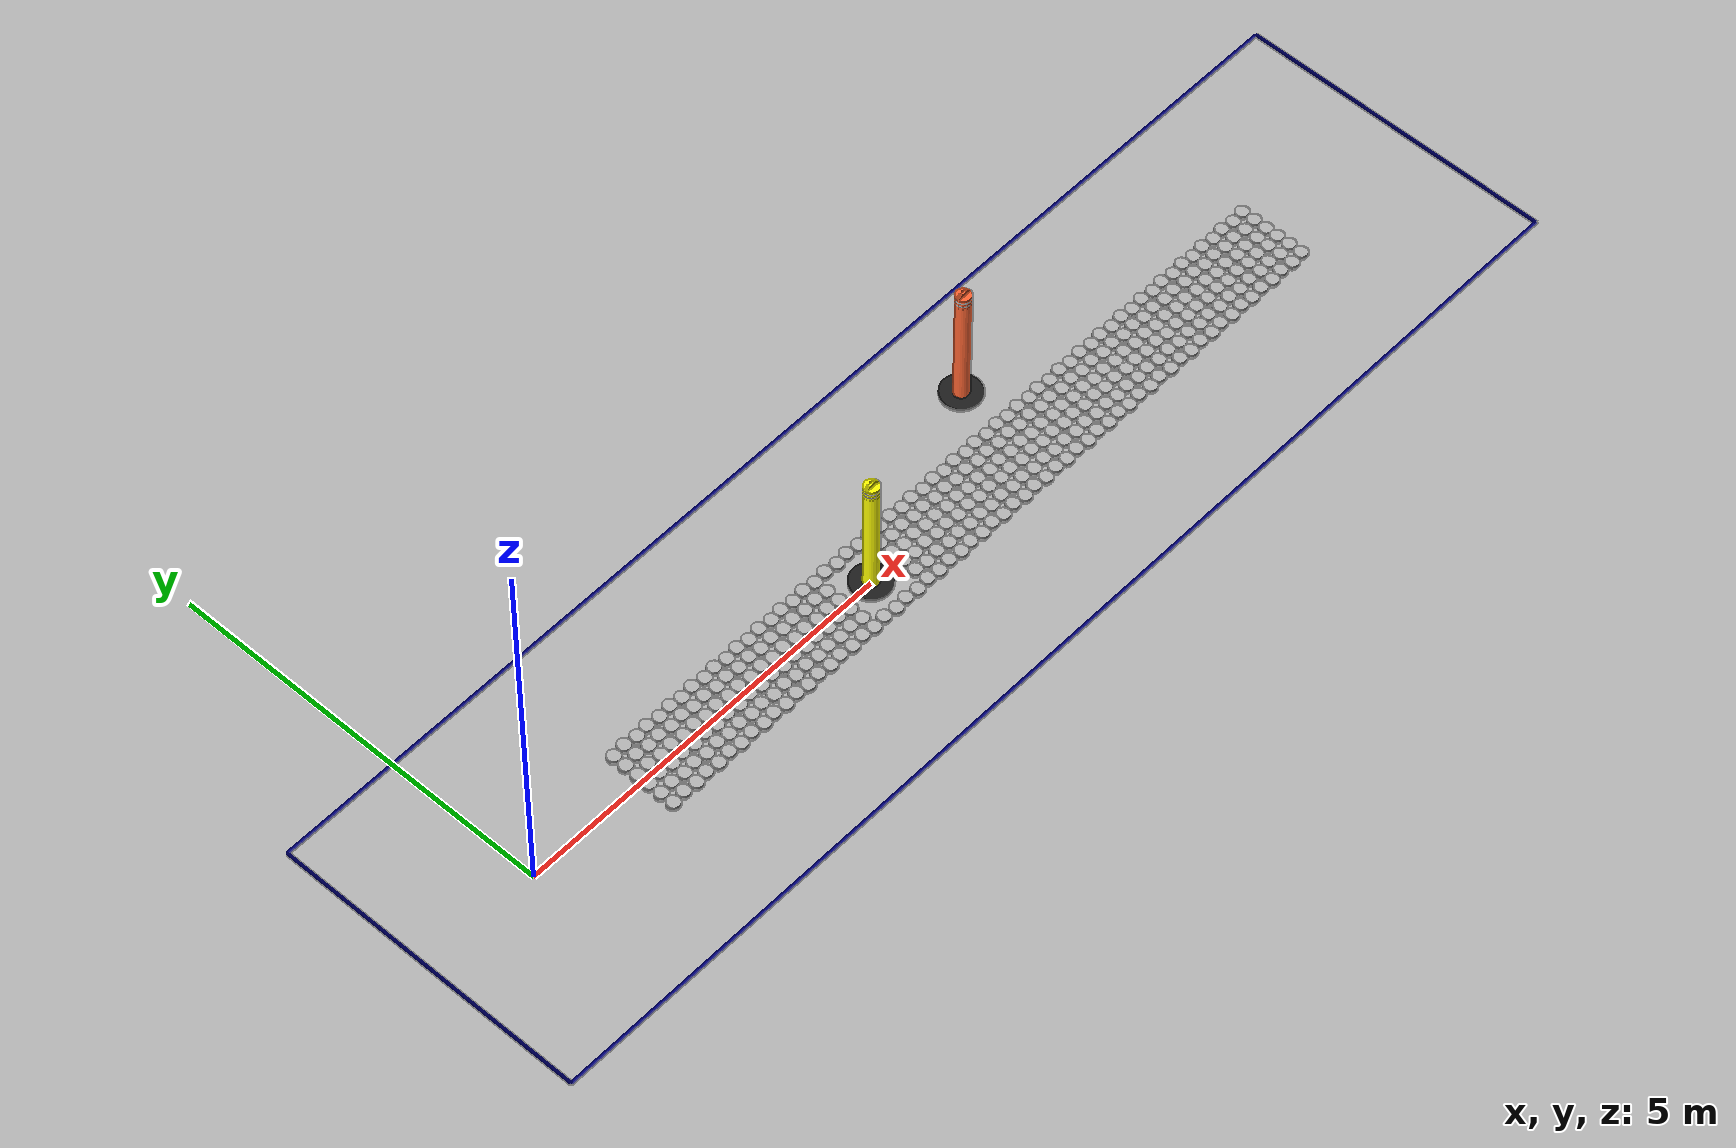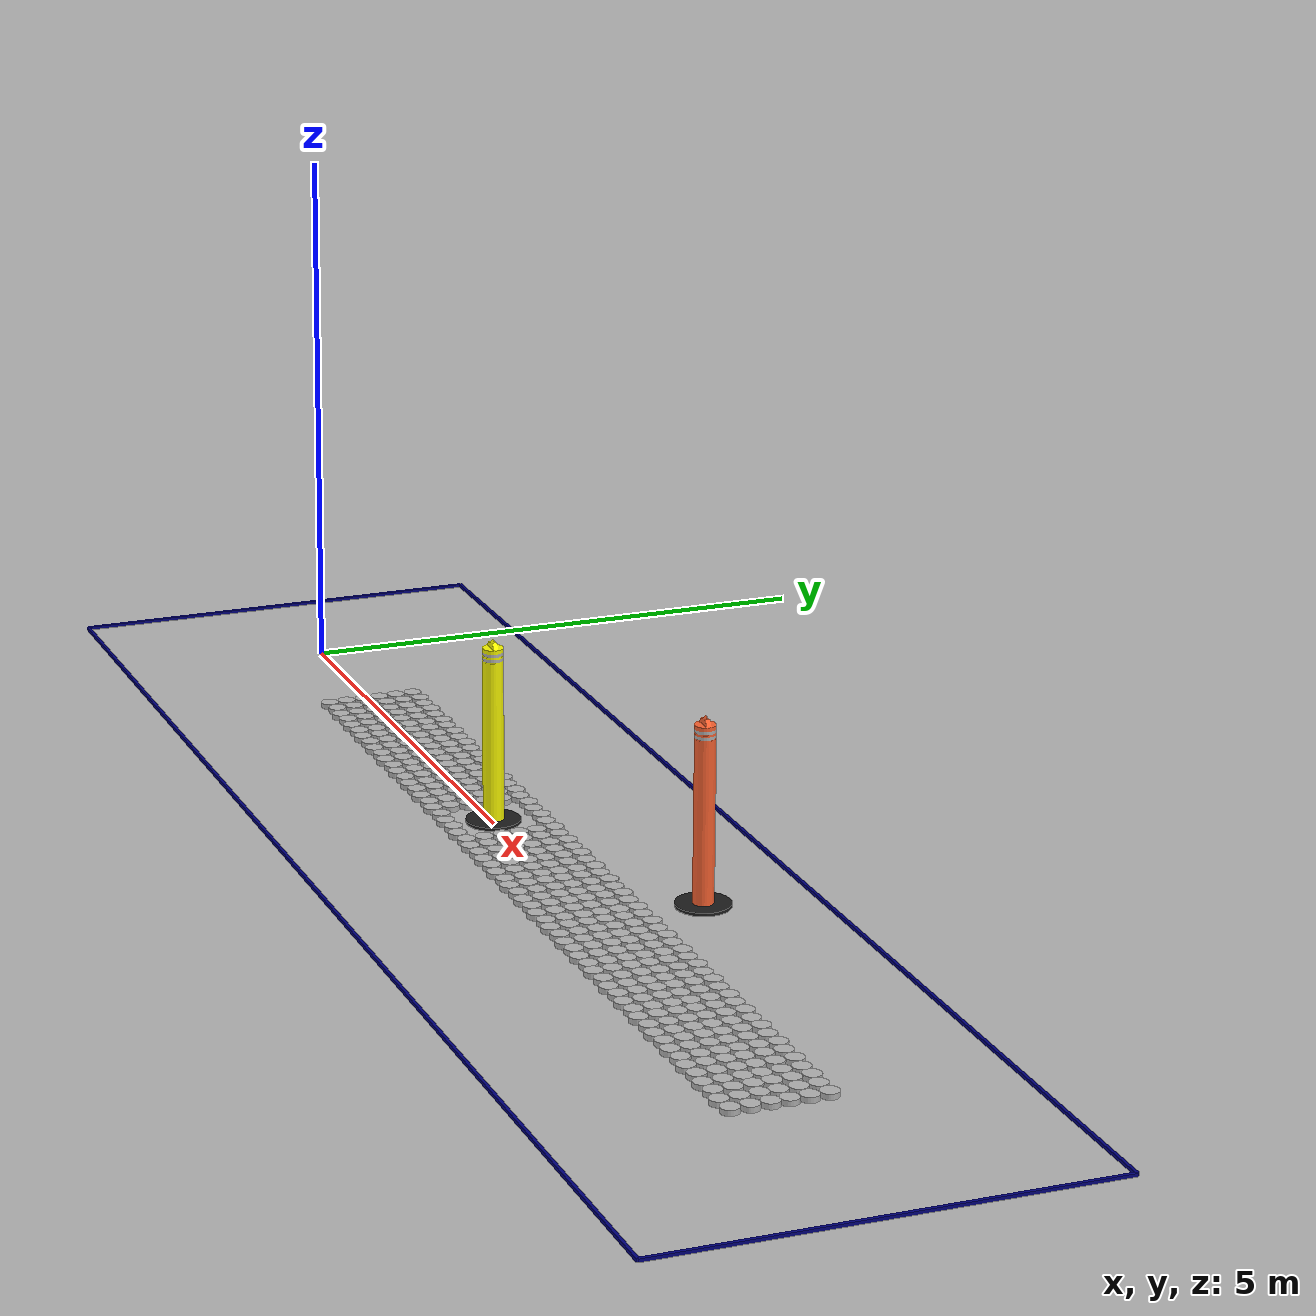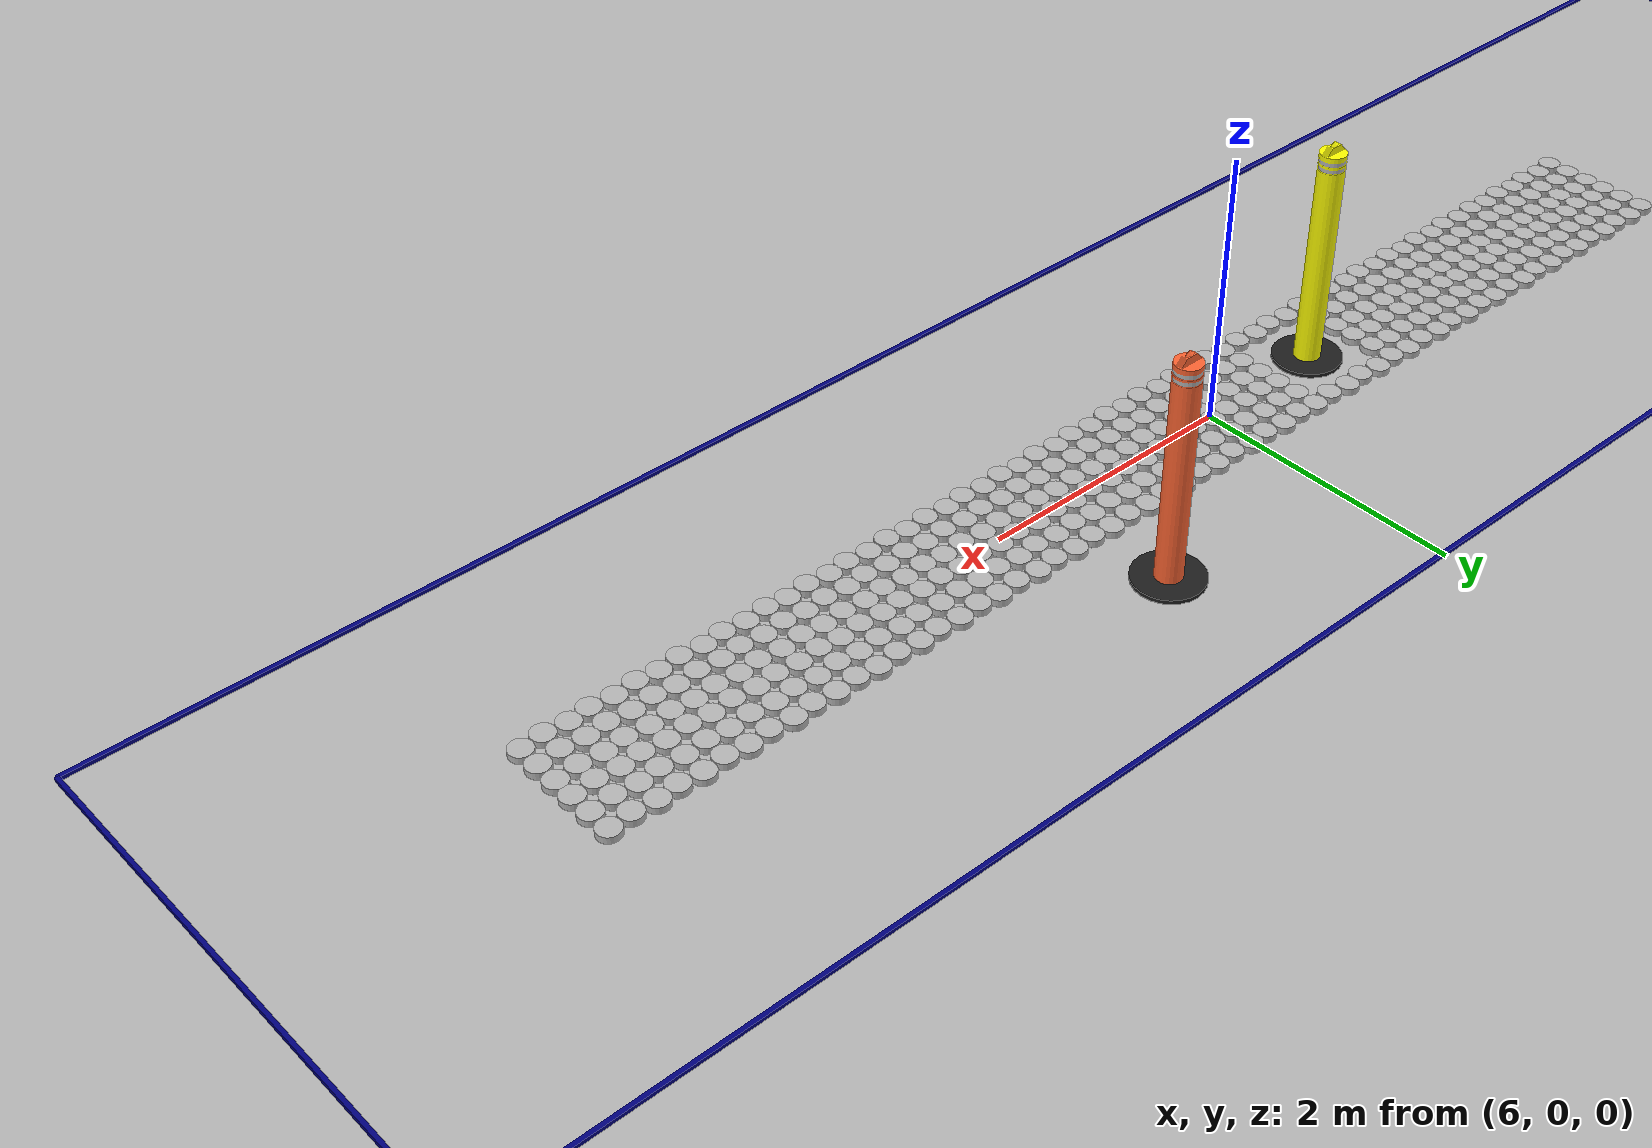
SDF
<sdf version="1.6">
 <world name="default">
  <light name="sun" type="directional">
   <pose>0 0 10 0 -0 0</pose>
   <diffuse>0.8 0.8 0.8 1</diffuse>
   <specular>0.1 0.1 0.1 1</specular>
   <attenuation>
    <range>1000</range>
    <constant>0.9</constant>
    <linear>0.01</linear>
    <quadratic>0.001</quadratic>
   </attenuation>
   <direction>-0.5 0.5 -1</direction>
  </light>
  <gravity>0 0 -9.8</gravity>
  <magnetic_field>6e-06 2.3e-05 -4.2e-05</magnetic_field>
  <atmosphere type="adiabatic"/>
  <physics name="default_physics" default="0" type="ode">
   <max_step_size>0.01</max_step_size>
   <real_time_factor>1</real_time_factor>
   <real_time_update_rate>100</real_time_update_rate>
  </physics>
  <scene><ambient>0.4 0.4 0.4 1</ambient><background>0.7 0.7 0.7 1</background><shadows>1</shadows></scene>
  <spherical_coordinates>
   <surface_model>EARTH_WGS84</surface_model>
   <latitude_deg>0</latitude_deg>
   <longitude_deg>0</longitude_deg>
   <elevation>0</elevation>
   <heading_deg>0</heading_deg>
  </spherical_coordinates>
  <model name="brick_plane">
   <static>1</static>
   <link name="link">
    <collision name="collision">
     <geometry><plane><normal>0 0 1</normal><size>100 100</size></plane></geometry>
     <surface><friction><ode><mu>100</mu><mu2>50</mu2></ode></friction></surface>
    </collision>
    <visual name="visual">
     <cast_shadows>0</cast_shadows>
     <pose>0 0 -0.04 0 -0 0</pose>
     <geometry><mesh><uri>model://brick_plane/meshes/BrickRoad.dae</uri></mesh></geometry>
    </visual>
   </link>
   <pose>-0.145559 -0.040486 0 0 -0 0</pose>
  </model>
  <light name="user_point_light_0" type="point">
   <pose>-40.2877 36.9378 1 0 -0 0</pose>
   <diffuse>0.5 0.5 0.5 1</diffuse>
   <specular>0.1 0.1 0.1 1</specular>
   <attenuation>
    <range>20</range>
    <constant>0.5</constant>
    <linear>0.01</linear>
    <quadratic>0.001</quadratic>
   </attenuation>
   <cast_shadows>0</cast_shadows>
   <direction>0 0 -1</direction>
  </light>
  <light name="user_point_light_0_clone" type="point">
   <pose>-43.3445 16.5003 10 0 -0 0</pose>
   <diffuse>1 1 1 1</diffuse>
   <specular>1 1 1 1</specular>
   <direction>0 0 -1</direction>
   <attenuation>
    <range>100000</range>
    <constant>0.5</constant>
    <linear>0.01</linear>
    <quadratic>0.001</quadratic>
   </attenuation>
  </light>
  <light name="user_point_light_0_clone_0" type="point">
   <pose>-41.8744 -4.62896 10 0 -0 0</pose>
   <diffuse>1 1 1 1</diffuse>
   <specular>1 1 1 1</specular>
   <direction>0 0 -1</direction>
   <attenuation>
    <range>100000</range>
    <constant>0.5</constant>
    <linear>0.01</linear>
    <quadratic>0.001</quadratic>
   </attenuation>
  </light>
  <light name="user_point_light_0_clone_1" type="point">
   <pose>-45.3384 -27.6087 10 0 -0 0</pose>
   <diffuse>1 1 1 1</diffuse>
   <specular>1 1 1 1</specular>
   <direction>0 0 -1</direction>
   <attenuation>
    <range>100000</range>
    <constant>0.5</constant>
    <linear>0.01</linear>
    <quadratic>0.001</quadratic>
   </attenuation>
  </light>
  <light name="user_point_light_0_clone_2" type="point">
   <pose>-41.0308 -51.4934 10 0 -0 0</pose>
   <diffuse>1 1 1 1</diffuse>
   <specular>1 1 1 1</specular>
   <direction>0 0 -1</direction>
   <attenuation>
    <range>100000</range>
    <constant>0.5</constant>
    <linear>0.01</linear>
    <quadratic>0.001</quadratic>
   </attenuation>
  </light>
  <light name="user_point_light_0_clone_3" type="point">
   <pose>-13.091 -48.6057 10 0 -0 0</pose>
   <diffuse>1 1 1 1</diffuse>
   <specular>1 1 1 1</specular>
   <direction>0 0 -1</direction>
   <attenuation>
    <range>100000</range>
    <constant>0.5</constant>
    <linear>0.01</linear>
    <quadratic>0.001</quadratic>
   </attenuation>
  </light>
  <light name="user_point_light_0_clone_4" type="point">
   <pose>17.8273 -50.2126 10 0 -0 0</pose>
   <diffuse>1 1 1 1</diffuse>
   <specular>1 1 1 1</specular>
   <direction>0 0 -1</direction>
   <attenuation>
    <range>100000</range>
    <constant>0.5</constant>
    <linear>0.01</linear>
    <quadratic>0.001</quadratic>
   </attenuation>
  </light>
  <light name="user_point_light_0_clone_5" type="point">
   <pose>43.0105 -50.5018 10 0 -0 0</pose>
   <diffuse>1 1 1 1</diffuse>
   <specular>1 1 1 1</specular>
   <direction>0 0 -1</direction>
   <attenuation>
    <range>100000</range>
    <constant>0.5</constant>
    <linear>0.01</linear>
    <quadratic>0.001</quadratic>
   </attenuation>
  </light>
  <light name="user_point_light_0_clone_6" type="point">
   <pose>-30.8096 43.6215 10 0 -0 0</pose>
   <diffuse>1 1 1 1</diffuse>
   <specular>1 1 1 1</specular>
   <direction>0 0 -1</direction>
   <attenuation>
    <range>100000</range>
    <constant>0.5</constant>
    <linear>0.01</linear>
    <quadratic>0.001</quadratic>
   </attenuation>
  </light>
  <light name="user_point_light_0_clone_7" type="point">
   <pose>-6.06965 44.6895 10 0 -0 0</pose>
   <diffuse>1 1 1 1</diffuse>
   <specular>1 1 1 1</specular>
   <direction>0 0 -1</direction>
   <attenuation>
    <range>100000</range>
    <constant>0.5</constant>
    <linear>0.01</linear>
    <quadratic>0.001</quadratic>
   </attenuation>
  </light>
  <light name="user_point_light_0_clone_8" type="point">
   <pose>12.7263 46.5664 10 0 -0 0</pose>
   <diffuse>1 1 1 1</diffuse>
   <specular>1 1 1 1</specular>
   <direction>0 0 -1</direction>
   <attenuation>
    <range>100000</range>
    <constant>0.5</constant>
    <linear>0.01</linear>
    <quadratic>0.001</quadratic>
   </attenuation>
  </light>
  <light name="user_point_light_0_clone_9" type="point">
   <pose>31.1126 44.5953 10 0 -0 0</pose>
   <diffuse>1 1 1 1</diffuse>
   <specular>1 1 1 1</specular>
   <direction>0 0 -1</direction>
   <attenuation>
    <range>100000</range>
    <constant>0.5</constant>
    <linear>0.01</linear>
    <quadratic>0.001</quadratic>
   </attenuation>
  </light>
  <light name="user_point_light_0_clone_10" type="point">
   <pose>48.6896 31.6 10 0 -0 0</pose>
   <diffuse>1 1 1 1</diffuse>
   <specular>1 1 1 1</specular>
   <direction>0 0 -1</direction>
   <attenuation>
    <range>100000</range>
    <constant>0.5</constant>
    <linear>0.01</linear>
    <quadratic>0.001</quadratic>
   </attenuation>
  </light>
  <light name="user_point_light_0_clone_11" type="point">
   <pose>54.0783 8.97523 10 0 -0 0</pose>
   <diffuse>1 1 1 1</diffuse>
   <specular>1 1 1 1</specular>
   <direction>0 0 -1</direction>
   <attenuation>
    <range>100000</range>
    <constant>0.5</constant>
    <linear>0.01</linear>
    <quadratic>0.001</quadratic>
   </attenuation>
  </light>
  <light name="user_point_light_0_clone_12" type="point">
   <pose>59.1715 -20.1842 10 0 -0 0</pose>
   <diffuse>1 1 1 1</diffuse>
   <specular>1 1 1 1</specular>
   <direction>0 0 -1</direction>
   <attenuation>
    <range>100000</range>
    <constant>0.5</constant>
    <linear>0.01</linear>
    <quadratic>0.001</quadratic>
   </attenuation>
  </light>
  <light name="user_point_light_0_clone_13" type="point">
   <pose>56.6391 -41.8663 10 0 -0 0</pose>
   <diffuse>1 1 1 1</diffuse>
   <specular>1 1 1 1</specular>
   <direction>0 0 -1</direction>
   <attenuation>
    <range>100000</range>
    <constant>0.5</constant>
    <linear>0.01</linear>
    <quadratic>0.001</quadratic>
   </attenuation>
  </light>
  <model name="single-I"><include><uri>model://single-I</uri></include><pose>6 -2 .03 0 0 0</pose></model>
  <model name="pylon_yellow"><include><uri>model://pylon_yellow</uri></include><pose>5 0 0 0 0 0</pose></model>
  <model name="pylon_orange">
   <include><uri>model://pylon_orange</uri></include>
   <pose>7.5 1 0 0 0 0</pose>
  </model>
  <model name="SnowPuck-0-0-0">
   <pose>1.58 -0.43 0.05  0 0 0</pose>
   <link name="link">
    <inertial>
     <mass>0.01</mass>
     <inertia><ixx>0.145833</ixx><ixy>0</ixy><ixz>0</ixz><iyy>0.145833</iyy><iyz>0</iyz><izz>0.125</izz></inertia>
    </inertial>
    <collision name="collision">
     <geometry><cylinder><radius>.05</radius><length>0.04</length></cylinder></geometry>
    </collision>
    <visual name="visual">
     <geometry><cylinder><radius>.083333</radius><length>0.05</length></cylinder></geometry>
    </visual>
   </link>
  </model>
  <model name="SnowPuck-0-1-0">
   <pose>1.58 -0.26 0.05  0 0 0</pose>
   <link name="link">
    <inertial>
     <mass>0.01</mass>
     <inertia><ixx>0.145833</ixx><ixy>0</ixy><ixz>0</ixz><iyy>0.145833</iyy><iyz>0</iyz><izz>0.125</izz></inertia>
    </inertial>
    <collision name="collision">
     <geometry><cylinder><radius>.05</radius><length>0.04</length></cylinder></geometry>
    </collision>
    <visual name="visual">
     <geometry><cylinder><radius>.083333</radius><length>0.05</length></cylinder></geometry>
    </visual>
   </link>
  </model>
  <model name="SnowPuck-0-2-0">
   <pose>1.58 -0.09 0.05  0 0 0</pose>
   <link name="link">
    <inertial>
     <mass>0.01</mass>
     <inertia><ixx>0.145833</ixx><ixy>0</ixy><ixz>0</ixz><iyy>0.145833</iyy><iyz>0</iyz><izz>0.125</izz></inertia>
    </inertial>
    <collision name="collision">
     <geometry><cylinder><radius>.05</radius><length>0.04</length></cylinder></geometry>
    </collision>
    <visual name="visual">
     <geometry><cylinder><radius>.083333</radius><length>0.05</length></cylinder></geometry>
    </visual>
   </link>
  </model>
  <model name="SnowPuck-0-3-0">
   <pose>1.58 0.07 0.05  0 0 0</pose>
   <link name="link">
    <inertial>
     <mass>0.01</mass>
     <inertia><ixx>0.145833</ixx><ixy>0</ixy><ixz>0</ixz><iyy>0.145833</iyy><iyz>0</iyz><izz>0.125</izz></inertia>
    </inertial>
    <collision name="collision">
     <geometry><cylinder><radius>.05</radius><length>0.04</length></cylinder></geometry>
    </collision>
    <visual name="visual">
     <geometry><cylinder><radius>.083333</radius><length>0.05</length></cylinder></geometry>
    </visual>
   </link>
  </model>
  <model name="SnowPuck-0-4-0">
   <pose>1.58 0.24 0.05  0 0 0</pose>
   <link name="link">
    <inertial>
     <mass>0.01</mass>
     <inertia><ixx>0.145833</ixx><ixy>0</ixy><ixz>0</ixz><iyy>0.145833</iyy><iyz>0</iyz><izz>0.125</izz></inertia>
    </inertial>
    <collision name="collision">
     <geometry><cylinder><radius>.05</radius><length>0.04</length></cylinder></geometry>
    </collision>
    <visual name="visual">
     <geometry><cylinder><radius>.083333</radius><length>0.05</length></cylinder></geometry>
    </visual>
   </link>
  </model>
  <model name="SnowPuck-0-5-0">
   <pose>1.58 0.41 0.05  0 0 0</pose>
   <link name="link">
    <inertial>
     <mass>0.01</mass>
     <inertia><ixx>0.145833</ixx><ixy>0</ixy><ixz>0</ixz><iyy>0.145833</iyy><iyz>0</iyz><izz>0.125</izz></inertia>
    </inertial>
    <collision name="collision">
     <geometry><cylinder><radius>.05</radius><length>0.04</length></cylinder></geometry>
    </collision>
    <visual name="visual">
     <geometry><cylinder><radius>.083333</radius><length>0.05</length></cylinder></geometry>
    </visual>
   </link>
  </model>
  <model name="SnowPuck-1-0-0">
   <pose>1.75 -0.41 0.05  0 0 0</pose>
   <link name="link">
    <inertial>
     <mass>0.01</mass>
     <inertia><ixx>0.145833</ixx><ixy>0</ixy><ixz>0</ixz><iyy>0.145833</iyy><iyz>0</iyz><izz>0.125</izz></inertia>
    </inertial>
    <collision name="collision">
     <geometry><cylinder><radius>.05</radius><length>0.04</length></cylinder></geometry>
    </collision>
    <visual name="visual">
     <geometry><cylinder><radius>.083333</radius><length>0.05</length></cylinder></geometry>
    </visual>
   </link>
  </model>
  <model name="SnowPuck-1-1-0">
   <pose>1.75 -0.24 0.05  0 0 0</pose>
   <link name="link">
    <inertial>
     <mass>0.01</mass>
     <inertia><ixx>0.145833</ixx><ixy>0</ixy><ixz>0</ixz><iyy>0.145833</iyy><iyz>0</iyz><izz>0.125</izz></inertia>
    </inertial>
    <collision name="collision">
     <geometry><cylinder><radius>.05</radius><length>0.04</length></cylinder></geometry>
    </collision>
    <visual name="visual">
     <geometry><cylinder><radius>.083333</radius><length>0.05</length></cylinder></geometry>
    </visual>
   </link>
  </model>
  <model name="SnowPuck-1-2-0">
   <pose>1.75 -0.07 0.05  0 0 0</pose>
   <link name="link">
    <inertial>
     <mass>0.01</mass>
     <inertia><ixx>0.145833</ixx><ixy>0</ixy><ixz>0</ixz><iyy>0.145833</iyy><iyz>0</iyz><izz>0.125</izz></inertia>
    </inertial>
    <collision name="collision">
     <geometry><cylinder><radius>.05</radius><length>0.04</length></cylinder></geometry>
    </collision>
    <visual name="visual">
     <geometry><cylinder><radius>.083333</radius><length>0.05</length></cylinder></geometry>
    </visual>
   </link>
  </model>
  <model name="SnowPuck-1-3-0">
   <pose>1.75 0.09 0.05  0 0 0</pose>
   <link name="link">
    <inertial>
     <mass>0.01</mass>
     <inertia><ixx>0.145833</ixx><ixy>0</ixy><ixz>0</ixz><iyy>0.145833</iyy><iyz>0</iyz><izz>0.125</izz></inertia>
    </inertial>
    <collision name="collision">
     <geometry><cylinder><radius>.05</radius><length>0.04</length></cylinder></geometry>
    </collision>
    <visual name="visual">
     <geometry><cylinder><radius>.083333</radius><length>0.05</length></cylinder></geometry>
    </visual>
   </link>
  </model>
  <model name="SnowPuck-1-4-0">
   <pose>1.75 0.26 0.05  0 0 0</pose>
   <link name="link">
    <inertial>
     <mass>0.01</mass>
     <inertia><ixx>0.145833</ixx><ixy>0</ixy><ixz>0</ixz><iyy>0.145833</iyy><iyz>0</iyz><izz>0.125</izz></inertia>
    </inertial>
    <collision name="collision">
     <geometry><cylinder><radius>.05</radius><length>0.04</length></cylinder></geometry>
    </collision>
    <visual name="visual">
     <geometry><cylinder><radius>.083333</radius><length>0.05</length></cylinder></geometry>
    </visual>
   </link>
  </model>
  <model name="SnowPuck-1-5-0">
   <pose>1.75 0.43 0.05  0 0 0</pose>
   <link name="link">
    <inertial>
     <mass>0.01</mass>
     <inertia><ixx>0.145833</ixx><ixy>0</ixy><ixz>0</ixz><iyy>0.145833</iyy><iyz>0</iyz><izz>0.125</izz></inertia>
    </inertial>
    <collision name="collision">
     <geometry><cylinder><radius>.05</radius><length>0.04</length></cylinder></geometry>
    </collision>
    <visual name="visual">
     <geometry><cylinder><radius>.083333</radius><length>0.05</length></cylinder></geometry>
    </visual>
   </link>
  </model>
  <model name="SnowPuck-2-0-0">
   <pose>1.92 -0.43 0.05  0 0 0</pose>
   <link name="link">
    <inertial>
     <mass>0.01</mass>
     <inertia><ixx>0.145833</ixx><ixy>0</ixy><ixz>0</ixz><iyy>0.145833</iyy><iyz>0</iyz><izz>0.125</izz></inertia>
    </inertial>
    <collision name="collision">
     <geometry><cylinder><radius>.05</radius><length>0.04</length></cylinder></geometry>
    </collision>
    <visual name="visual">
     <geometry><cylinder><radius>.083333</radius><length>0.05</length></cylinder></geometry>
    </visual>
   </link>
  </model>
  <model name="SnowPuck-2-1-0">
   <pose>1.92 -0.26 0.05  0 0 0</pose>
   <link name="link">
    <inertial>
     <mass>0.01</mass>
     <inertia><ixx>0.145833</ixx><ixy>0</ixy><ixz>0</ixz><iyy>0.145833</iyy><iyz>0</iyz><izz>0.125</izz></inertia>
    </inertial>
    <collision name="collision">
     <geometry><cylinder><radius>.05</radius><length>0.04</length></cylinder></geometry>
    </collision>
    <visual name="visual">
     <geometry><cylinder><radius>.083333</radius><length>0.05</length></cylinder></geometry>
    </visual>
   </link>
  </model>
  <model name="SnowPuck-2-2-0">
   <pose>1.92 -0.09 0.05  0 0 0</pose>
   <link name="link">
    <inertial>
     <mass>0.01</mass>
     <inertia><ixx>0.145833</ixx><ixy>0</ixy><ixz>0</ixz><iyy>0.145833</iyy><iyz>0</iyz><izz>0.125</izz></inertia>
    </inertial>
    <collision name="collision">
     <geometry><cylinder><radius>.05</radius><length>0.04</length></cylinder></geometry>
    </collision>
    <visual name="visual">
     <geometry><cylinder><radius>.083333</radius><length>0.05</length></cylinder></geometry>
    </visual>
   </link>
  </model>
  <model name="SnowPuck-2-3-0">
   <pose>1.92 0.07 0.05  0 0 0</pose>
   <link name="link">
    <inertial>
     <mass>0.01</mass>
     <inertia><ixx>0.145833</ixx><ixy>0</ixy><ixz>0</ixz><iyy>0.145833</iyy><iyz>0</iyz><izz>0.125</izz></inertia>
    </inertial>
    <collision name="collision">
     <geometry><cylinder><radius>.05</radius><length>0.04</length></cylinder></geometry>
    </collision>
    <visual name="visual">
     <geometry><cylinder><radius>.083333</radius><length>0.05</length></cylinder></geometry>
    </visual>
   </link>
  </model>
  <model name="SnowPuck-2-4-0">
   <pose>1.92 0.24 0.05  0 0 0</pose>
   <link name="link">
    <inertial>
     <mass>0.01</mass>
     <inertia><ixx>0.145833</ixx><ixy>0</ixy><ixz>0</ixz><iyy>0.145833</iyy><iyz>0</iyz><izz>0.125</izz></inertia>
    </inertial>
    <collision name="collision">
     <geometry><cylinder><radius>.05</radius><length>0.04</length></cylinder></geometry>
    </collision>
    <visual name="visual">
     <geometry><cylinder><radius>.083333</radius><length>0.05</length></cylinder></geometry>
    </visual>
   </link>
  </model>
  <model name="SnowPuck-2-5-0">
   <pose>1.92 0.41 0.05  0 0 0</pose>
   <link name="link">
    <inertial>
     <mass>0.01</mass>
     <inertia><ixx>0.145833</ixx><ixy>0</ixy><ixz>0</ixz><iyy>0.145833</iyy><iyz>0</iyz><izz>0.125</izz></inertia>
    </inertial>
    <collision name="collision">
     <geometry><cylinder><radius>.05</radius><length>0.04</length></cylinder></geometry>
    </collision>
    <visual name="visual">
     <geometry><cylinder><radius>.083333</radius><length>0.05</length></cylinder></geometry>
    </visual>
   </link>
  </model>
  <model name="SnowPuck-3-0-0">
   <pose>2.08 -0.41 0.05  0 0 0</pose>
   <link name="link">
    <inertial>
     <mass>0.01</mass>
     <inertia><ixx>0.145833</ixx><ixy>0</ixy><ixz>0</ixz><iyy>0.145833</iyy><iyz>0</iyz><izz>0.125</izz></inertia>
    </inertial>
    <collision name="collision">
     <geometry><cylinder><radius>.05</radius><length>0.04</length></cylinder></geometry>
    </collision>
    <visual name="visual">
     <geometry><cylinder><radius>.083333</radius><length>0.05</length></cylinder></geometry>
    </visual>
   </link>
  </model>
  <model name="SnowPuck-3-1-0">
   <pose>2.08 -0.24 0.05  0 0 0</pose>
   <link name="link">
    <inertial>
     <mass>0.01</mass>
     <inertia><ixx>0.145833</ixx><ixy>0</ixy><ixz>0</ixz><iyy>0.145833</iyy><iyz>0</iyz><izz>0.125</izz></inertia>
    </inertial>
    <collision name="collision">
     <geometry><cylinder><radius>.05</radius><length>0.04</length></cylinder></geometry>
    </collision>
    <visual name="visual">
     <geometry><cylinder><radius>.083333</radius><length>0.05</length></cylinder></geometry>
    </visual>
   </link>
  </model>
  <model name="SnowPuck-3-2-0">
   <pose>2.08 -0.07 0.05  0 0 0</pose>
   <link name="link">
    <inertial>
     <mass>0.01</mass>
     <inertia><ixx>0.145833</ixx><ixy>0</ixy><ixz>0</ixz><iyy>0.145833</iyy><iyz>0</iyz><izz>0.125</izz></inertia>
    </inertial>
    <collision name="collision">
     <geometry><cylinder><radius>.05</radius><length>0.04</length></cylinder></geometry>
    </collision>
    <visual name="visual">
     <geometry><cylinder><radius>.083333</radius><length>0.05</length></cylinder></geometry>
    </visual>
   </link>
  </model>
  <model name="SnowPuck-3-3-0">
   <pose>2.08 0.09 0.05  0 0 0</pose>
   <link name="link">
    <inertial>
     <mass>0.01</mass>
     <inertia><ixx>0.145833</ixx><ixy>0</ixy><ixz>0</ixz><iyy>0.145833</iyy><iyz>0</iyz><izz>0.125</izz></inertia>
    </inertial>
    <collision name="collision">
     <geometry><cylinder><radius>.05</radius><length>0.04</length></cylinder></geometry>
    </collision>
    <visual name="visual">
     <geometry><cylinder><radius>.083333</radius><length>0.05</length></cylinder></geometry>
    </visual>
   </link>
  </model>
  <model name="SnowPuck-3-4-0">
   <pose>2.08 0.26 0.05  0 0 0</pose>
   <link name="link">
    <inertial>
     <mass>0.01</mass>
     <inertia><ixx>0.145833</ixx><ixy>0</ixy><ixz>0</ixz><iyy>0.145833</iyy><iyz>0</iyz><izz>0.125</izz></inertia>
    </inertial>
    <collision name="collision">
     <geometry><cylinder><radius>.05</radius><length>0.04</length></cylinder></geometry>
    </collision>
    <visual name="visual">
     <geometry><cylinder><radius>.083333</radius><length>0.05</length></cylinder></geometry>
    </visual>
   </link>
  </model>
  <model name="SnowPuck-3-5-0">
   <pose>2.08 0.43 0.05  0 0 0</pose>
   <link name="link">
    <inertial>
     <mass>0.01</mass>
     <inertia><ixx>0.145833</ixx><ixy>0</ixy><ixz>0</ixz><iyy>0.145833</iyy><iyz>0</iyz><izz>0.125</izz></inertia>
    </inertial>
    <collision name="collision">
     <geometry><cylinder><radius>.05</radius><length>0.04</length></cylinder></geometry>
    </collision>
    <visual name="visual">
     <geometry><cylinder><radius>.083333</radius><length>0.05</length></cylinder></geometry>
    </visual>
   </link>
  </model>
  <model name="SnowPuck-4-0-0">
   <pose>2.25 -0.43 0.05  0 0 0</pose>
   <link name="link">
    <inertial>
     <mass>0.01</mass>
     <inertia><ixx>0.145833</ixx><ixy>0</ixy><ixz>0</ixz><iyy>0.145833</iyy><iyz>0</iyz><izz>0.125</izz></inertia>
    </inertial>
    <collision name="collision">
     <geometry><cylinder><radius>.05</radius><length>0.04</length></cylinder></geometry>
    </collision>
    <visual name="visual">
     <geometry><cylinder><radius>.083333</radius><length>0.05</length></cylinder></geometry>
    </visual>
   </link>
  </model>
  <model name="SnowPuck-4-1-0">
   <pose>2.25 -0.26 0.05  0 0 0</pose>
   <link name="link">
    <inertial>
     <mass>0.01</mass>
     <inertia><ixx>0.145833</ixx><ixy>0</ixy><ixz>0</ixz><iyy>0.145833</iyy><iyz>0</iyz><izz>0.125</izz></inertia>
    </inertial>
    <collision name="collision">
     <geometry><cylinder><radius>.05</radius><length>0.04</length></cylinder></geometry>
    </collision>
    <visual name="visual">
     <geometry><cylinder><radius>.083333</radius><length>0.05</length></cylinder></geometry>
    </visual>
   </link>
  </model>
  <model name="SnowPuck-4-2-0">
   <pose>2.25 -0.09 0.05  0 0 0</pose>
   <link name="link">
    <inertial>
     <mass>0.01</mass>
     <inertia><ixx>0.145833</ixx><ixy>0</ixy><ixz>0</ixz><iyy>0.145833</iyy><iyz>0</iyz><izz>0.125</izz></inertia>
    </inertial>
    <collision name="collision">
     <geometry><cylinder><radius>.05</radius><length>0.04</length></cylinder></geometry>
    </collision>
    <visual name="visual">
     <geometry><cylinder><radius>.083333</radius><length>0.05</length></cylinder></geometry>
    </visual>
   </link>
  </model>
  <model name="SnowPuck-4-3-0">
   <pose>2.25 0.07 0.05  0 0 0</pose>
   <link name="link">
    <inertial>
     <mass>0.01</mass>
     <inertia><ixx>0.145833</ixx><ixy>0</ixy><ixz>0</ixz><iyy>0.145833</iyy><iyz>0</iyz><izz>0.125</izz></inertia>
    </inertial>
    <collision name="collision">
     <geometry><cylinder><radius>.05</radius><length>0.04</length></cylinder></geometry>
    </collision>
    <visual name="visual">
     <geometry><cylinder><radius>.083333</radius><length>0.05</length></cylinder></geometry>
    </visual>
   </link>
  </model>
  <model name="SnowPuck-4-4-0">
   <pose>2.25 0.24 0.05  0 0 0</pose>
   <link name="link">
    <inertial>
     <mass>0.01</mass>
     <inertia><ixx>0.145833</ixx><ixy>0</ixy><ixz>0</ixz><iyy>0.145833</iyy><iyz>0</iyz><izz>0.125</izz></inertia>
    </inertial>
    <collision name="collision">
     <geometry><cylinder><radius>.05</radius><length>0.04</length></cylinder></geometry>
    </collision>
    <visual name="visual">
     <geometry><cylinder><radius>.083333</radius><length>0.05</length></cylinder></geometry>
    </visual>
   </link>
  </model>
  <model name="SnowPuck-4-5-0">
   <pose>2.25 0.41 0.05  0 0 0</pose>
   <link name="link">
    <inertial>
     <mass>0.01</mass>
     <inertia><ixx>0.145833</ixx><ixy>0</ixy><ixz>0</ixz><iyy>0.145833</iyy><iyz>0</iyz><izz>0.125</izz></inertia>
    </inertial>
    <collision name="collision">
     <geometry><cylinder><radius>.05</radius><length>0.04</length></cylinder></geometry>
    </collision>
    <visual name="visual">
     <geometry><cylinder><radius>.083333</radius><length>0.05</length></cylinder></geometry>
    </visual>
   </link>
  </model>
  <model name="SnowPuck-5-0-0">
   <pose>2.42 -0.41 0.05  0 0 0</pose>
   <link name="link">
    <inertial>
     <mass>0.01</mass>
     <inertia><ixx>0.145833</ixx><ixy>0</ixy><ixz>0</ixz><iyy>0.145833</iyy><iyz>0</iyz><izz>0.125</izz></inertia>
    </inertial>
    <collision name="collision">
     <geometry><cylinder><radius>.05</radius><length>0.04</length></cylinder></geometry>
    </collision>
    <visual name="visual">
     <geometry><cylinder><radius>.083333</radius><length>0.05</length></cylinder></geometry>
    </visual>
   </link>
  </model>
  <model name="SnowPuck-5-1-0">
   <pose>2.42 -0.24 0.05  0 0 0</pose>
   <link name="link">
    <inertial>
     <mass>0.01</mass>
     <inertia><ixx>0.145833</ixx><ixy>0</ixy><ixz>0</ixz><iyy>0.145833</iyy><iyz>0</iyz><izz>0.125</izz></inertia>
    </inertial>
    <collision name="collision">
     <geometry><cylinder><radius>.05</radius><length>0.04</length></cylinder></geometry>
    </collision>
    <visual name="visual">
     <geometry><cylinder><radius>.083333</radius><length>0.05</length></cylinder></geometry>
    </visual>
   </link>
  </model>
  <model name="SnowPuck-5-2-0">
   <pose>2.42 -0.07 0.05  0 0 0</pose>
   <link name="link">
    <inertial>
     <mass>0.01</mass>
     <inertia><ixx>0.145833</ixx><ixy>0</ixy><ixz>0</ixz><iyy>0.145833</iyy><iyz>0</iyz><izz>0.125</izz></inertia>
    </inertial>
    <collision name="collision">
     <geometry><cylinder><radius>.05</radius><length>0.04</length></cylinder></geometry>
    </collision>
    <visual name="visual">
     <geometry><cylinder><radius>.083333</radius><length>0.05</length></cylinder></geometry>
    </visual>
   </link>
  </model>
  <model name="SnowPuck-5-3-0">
   <pose>2.42 0.09 0.05  0 0 0</pose>
   <link name="link">
    <inertial>
     <mass>0.01</mass>
     <inertia><ixx>0.145833</ixx><ixy>0</ixy><ixz>0</ixz><iyy>0.145833</iyy><iyz>0</iyz><izz>0.125</izz></inertia>
    </inertial>
    <collision name="collision">
     <geometry><cylinder><radius>.05</radius><length>0.04</length></cylinder></geometry>
    </collision>
    <visual name="visual">
     <geometry><cylinder><radius>.083333</radius><length>0.05</length></cylinder></geometry>
    </visual>
   </link>
  </model>
  <model name="SnowPuck-5-4-0">
   <pose>2.42 0.26 0.05  0 0 0</pose>
   <link name="link">
    <inertial>
     <mass>0.01</mass>
     <inertia><ixx>0.145833</ixx><ixy>0</ixy><ixz>0</ixz><iyy>0.145833</iyy><iyz>0</iyz><izz>0.125</izz></inertia>
    </inertial>
    <collision name="collision">
     <geometry><cylinder><radius>.05</radius><length>0.04</length></cylinder></geometry>
    </collision>
    <visual name="visual">
     <geometry><cylinder><radius>.083333</radius><length>0.05</length></cylinder></geometry>
    </visual>
   </link>
  </model>
  <model name="SnowPuck-5-5-0">
   <pose>2.42 0.43 0.05  0 0 0</pose>
   <link name="link">
    <inertial>
     <mass>0.01</mass>
     <inertia><ixx>0.145833</ixx><ixy>0</ixy><ixz>0</ixz><iyy>0.145833</iyy><iyz>0</iyz><izz>0.125</izz></inertia>
    </inertial>
    <collision name="collision">
     <geometry><cylinder><radius>.05</radius><length>0.04</length></cylinder></geometry>
    </collision>
    <visual name="visual">
     <geometry><cylinder><radius>.083333</radius><length>0.05</length></cylinder></geometry>
    </visual>
   </link>
  </model>
  <model name="SnowPuck-6-0-0">
   <pose>2.58 -0.43 0.05  0 0 0</pose>
   <link name="link">
    <inertial>
     <mass>0.01</mass>
     <inertia><ixx>0.145833</ixx><ixy>0</ixy><ixz>0</ixz><iyy>0.145833</iyy><iyz>0</iyz><izz>0.125</izz></inertia>
    </inertial>
    <collision name="collision">
     <geometry><cylinder><radius>.05</radius><length>0.04</length></cylinder></geometry>
    </collision>
    <visual name="visual">
     <geometry><cylinder><radius>.083333</radius><length>0.05</length></cylinder></geometry>
    </visual>
   </link>
  </model>
  <model name="SnowPuck-6-1-0">
   <pose>2.58 -0.26 0.05  0 0 0</pose>
   <link name="link">
    <inertial>
     <mass>0.01</mass>
     <inertia><ixx>0.145833</ixx><ixy>0</ixy><ixz>0</ixz><iyy>0.145833</iyy><iyz>0</iyz><izz>0.125</izz></inertia>
    </inertial>
    <collision name="collision">
     <geometry><cylinder><radius>.05</radius><length>0.04</length></cylinder></geometry>
    </collision>
    <visual name="visual">
     <geometry><cylinder><radius>.083333</radius><length>0.05</length></cylinder></geometry>
    </visual>
   </link>
  </model>
  <model name="SnowPuck-6-2-0">
   <pose>2.58 -0.09 0.05  0 0 0</pose>
   <link name="link">
    <inertial>
     <mass>0.01</mass>
     <inertia><ixx>0.145833</ixx><ixy>0</ixy><ixz>0</ixz><iyy>0.145833</iyy><iyz>0</iyz><izz>0.125</izz></inertia>
    </inertial>
    <collision name="collision">
     <geometry><cylinder><radius>.05</radius><length>0.04</length></cylinder></geometry>
    </collision>
    <visual name="visual">
     <geometry><cylinder><radius>.083333</radius><length>0.05</length></cylinder></geometry>
    </visual>
   </link>
  </model>
  <model name="SnowPuck-6-3-0">
   <pose>2.58 0.07 0.05  0 0 0</pose>
   <link name="link">
    <inertial>
     <mass>0.01</mass>
     <inertia><ixx>0.145833</ixx><ixy>0</ixy><ixz>0</ixz><iyy>0.145833</iyy><iyz>0</iyz><izz>0.125</izz></inertia>
    </inertial>
    <collision name="collision">
     <geometry><cylinder><radius>.05</radius><length>0.04</length></cylinder></geometry>
    </collision>
    <visual name="visual">
     <geometry><cylinder><radius>.083333</radius><length>0.05</length></cylinder></geometry>
    </visual>
   </link>
  </model>
  <model name="SnowPuck-6-4-0">
   <pose>2.58 0.24 0.05  0 0 0</pose>
   <link name="link">
    <inertial>
     <mass>0.01</mass>
     <inertia><ixx>0.145833</ixx><ixy>0</ixy><ixz>0</ixz><iyy>0.145833</iyy><iyz>0</iyz><izz>0.125</izz></inertia>
    </inertial>
    <collision name="collision">
     <geometry><cylinder><radius>.05</radius><length>0.04</length></cylinder></geometry>
    </collision>
    <visual name="visual">
     <geometry><cylinder><radius>.083333</radius><length>0.05</length></cylinder></geometry>
    </visual>
   </link>
  </model>
  <model name="SnowPuck-6-5-0">
   <pose>2.58 0.41 0.05  0 0 0</pose>
   <link name="link">
    <inertial>
     <mass>0.01</mass>
     <inertia><ixx>0.145833</ixx><ixy>0</ixy><ixz>0</ixz><iyy>0.145833</iyy><iyz>0</iyz><izz>0.125</izz></inertia>
    </inertial>
    <collision name="collision">
     <geometry><cylinder><radius>.05</radius><length>0.04</length></cylinder></geometry>
    </collision>
    <visual name="visual">
     <geometry><cylinder><radius>.083333</radius><length>0.05</length></cylinder></geometry>
    </visual>
   </link>
  </model>
  <model name="SnowPuck-7-0-0">
   <pose>2.75 -0.41 0.05  0 0 0</pose>
   <link name="link">
    <inertial>
     <mass>0.01</mass>
     <inertia><ixx>0.145833</ixx><ixy>0</ixy><ixz>0</ixz><iyy>0.145833</iyy><iyz>0</iyz><izz>0.125</izz></inertia>
    </inertial>
    <collision name="collision">
     <geometry><cylinder><radius>.05</radius><length>0.04</length></cylinder></geometry>
    </collision>
    <visual name="visual">
     <geometry><cylinder><radius>.083333</radius><length>0.05</length></cylinder></geometry>
    </visual>
   </link>
  </model>
  <model name="SnowPuck-7-1-0">
   <pose>2.75 -0.24 0.05  0 0 0</pose>
   <link name="link">
    <inertial>
     <mass>0.01</mass>
     <inertia><ixx>0.145833</ixx><ixy>0</ixy><ixz>0</ixz><iyy>0.145833</iyy><iyz>0</iyz><izz>0.125</izz></inertia>
    </inertial>
    <collision name="collision">
     <geometry><cylinder><radius>.05</radius><length>0.04</length></cylinder></geometry>
    </collision>
    <visual name="visual">
     <geometry><cylinder><radius>.083333</radius><length>0.05</length></cylinder></geometry>
    </visual>
   </link>
  </model>
  <model name="SnowPuck-7-2-0">
   <pose>2.75 -0.07 0.05  0 0 0</pose>
   <link name="link">
    <inertial>
     <mass>0.01</mass>
     <inertia><ixx>0.145833</ixx><ixy>0</ixy><ixz>0</ixz><iyy>0.145833</iyy><iyz>0</iyz><izz>0.125</izz></inertia>
    </inertial>
    <collision name="collision">
     <geometry><cylinder><radius>.05</radius><length>0.04</length></cylinder></geometry>
    </collision>
    <visual name="visual">
     <geometry><cylinder><radius>.083333</radius><length>0.05</length></cylinder></geometry>
    </visual>
   </link>
  </model>
  <model name="SnowPuck-7-3-0">
   <pose>2.75 0.09 0.05  0 0 0</pose>
   <link name="link">
    <inertial>
     <mass>0.01</mass>
     <inertia><ixx>0.145833</ixx><ixy>0</ixy><ixz>0</ixz><iyy>0.145833</iyy><iyz>0</iyz><izz>0.125</izz></inertia>
    </inertial>
    <collision name="collision">
     <geometry><cylinder><radius>.05</radius><length>0.04</length></cylinder></geometry>
    </collision>
    <visual name="visual">
     <geometry><cylinder><radius>.083333</radius><length>0.05</length></cylinder></geometry>
    </visual>
   </link>
  </model>
  <model name="SnowPuck-7-4-0">
   <pose>2.75 0.26 0.05  0 0 0</pose>
   <link name="link">
    <inertial>
     <mass>0.01</mass>
     <inertia><ixx>0.145833</ixx><ixy>0</ixy><ixz>0</ixz><iyy>0.145833</iyy><iyz>0</iyz><izz>0.125</izz></inertia>
    </inertial>
    <collision name="collision">
     <geometry><cylinder><radius>.05</radius><length>0.04</length></cylinder></geometry>
    </collision>
    <visual name="visual">
     <geometry><cylinder><radius>.083333</radius><length>0.05</length></cylinder></geometry>
    </visual>
   </link>
  </model>
  <model name="SnowPuck-7-5-0">
   <pose>2.75 0.43 0.05  0 0 0</pose>
   <link name="link">
    <inertial>
     <mass>0.01</mass>
     <inertia><ixx>0.145833</ixx><ixy>0</ixy><ixz>0</ixz><iyy>0.145833</iyy><iyz>0</iyz><izz>0.125</izz></inertia>
    </inertial>
    <collision name="collision">
     <geometry><cylinder><radius>.05</radius><length>0.04</length></cylinder></geometry>
    </collision>
    <visual name="visual">
     <geometry><cylinder><radius>.083333</radius><length>0.05</length></cylinder></geometry>
    </visual>
   </link>
  </model>
  <model name="SnowPuck-8-0-0">
   <pose>2.92 -0.43 0.05  0 0 0</pose>
   <link name="link">
    <inertial>
     <mass>0.01</mass>
     <inertia><ixx>0.145833</ixx><ixy>0</ixy><ixz>0</ixz><iyy>0.145833</iyy><iyz>0</iyz><izz>0.125</izz></inertia>
    </inertial>
    <collision name="collision">
     <geometry><cylinder><radius>.05</radius><length>0.04</length></cylinder></geometry>
    </collision>
    <visual name="visual">
     <geometry><cylinder><radius>.083333</radius><length>0.05</length></cylinder></geometry>
    </visual>
   </link>
  </model>
  <model name="SnowPuck-8-1-0">
   <pose>2.92 -0.26 0.05  0 0 0</pose>
   <link name="link">
    <inertial>
     <mass>0.01</mass>
     <inertia><ixx>0.145833</ixx><ixy>0</ixy><ixz>0</ixz><iyy>0.145833</iyy><iyz>0</iyz><izz>0.125</izz></inertia>
    </inertial>
    <collision name="collision">
     <geometry><cylinder><radius>.05</radius><length>0.04</length></cylinder></geometry>
    </collision>
    <visual name="visual">
     <geometry><cylinder><radius>.083333</radius><length>0.05</length></cylinder></geometry>
    </visual>
   </link>
  </model>
  <model name="SnowPuck-8-2-0">
   <pose>2.92 -0.09 0.05  0 0 0</pose>
   <link name="link">
    <inertial>
     <mass>0.01</mass>
     <inertia><ixx>0.145833</ixx><ixy>0</ixy><ixz>0</ixz><iyy>0.145833</iyy><iyz>0</iyz><izz>0.125</izz></inertia>
    </inertial>
    <collision name="collision">
     <geometry><cylinder><radius>.05</radius><length>0.04</length></cylinder></geometry>
    </collision>
    <visual name="visual">
     <geometry><cylinder><radius>.083333</radius><length>0.05</length></cylinder></geometry>
    </visual>
   </link>
  </model>
  <model name="SnowPuck-8-3-0">
   <pose>2.92 0.07 0.05  0 0 0</pose>
   <link name="link">
    <inertial>
     <mass>0.01</mass>
     <inertia><ixx>0.145833</ixx><ixy>0</ixy><ixz>0</ixz><iyy>0.145833</iyy><iyz>0</iyz><izz>0.125</izz></inertia>
    </inertial>
    <collision name="collision">
     <geometry><cylinder><radius>.05</radius><length>0.04</length></cylinder></geometry>
    </collision>
    <visual name="visual">
     <geometry><cylinder><radius>.083333</radius><length>0.05</length></cylinder></geometry>
    </visual>
   </link>
  </model>
  <model name="SnowPuck-8-4-0">
   <pose>2.92 0.24 0.05  0 0 0</pose>
   <link name="link">
    <inertial>
     <mass>0.01</mass>
     <inertia><ixx>0.145833</ixx><ixy>0</ixy><ixz>0</ixz><iyy>0.145833</iyy><iyz>0</iyz><izz>0.125</izz></inertia>
    </inertial>
    <collision name="collision">
     <geometry><cylinder><radius>.05</radius><length>0.04</length></cylinder></geometry>
    </collision>
    <visual name="visual">
     <geometry><cylinder><radius>.083333</radius><length>0.05</length></cylinder></geometry>
    </visual>
   </link>
  </model>
  <model name="SnowPuck-8-5-0">
   <pose>2.92 0.41 0.05  0 0 0</pose>
   <link name="link">
    <inertial>
     <mass>0.01</mass>
     <inertia><ixx>0.145833</ixx><ixy>0</ixy><ixz>0</ixz><iyy>0.145833</iyy><iyz>0</iyz><izz>0.125</izz></inertia>
    </inertial>
    <collision name="collision">
     <geometry><cylinder><radius>.05</radius><length>0.04</length></cylinder></geometry>
    </collision>
    <visual name="visual">
     <geometry><cylinder><radius>.083333</radius><length>0.05</length></cylinder></geometry>
    </visual>
   </link>
  </model>
  <model name="SnowPuck-9-0-0">
   <pose>3.08 -0.41 0.05  0 0 0</pose>
   <link name="link">
    <inertial>
     <mass>0.01</mass>
     <inertia><ixx>0.145833</ixx><ixy>0</ixy><ixz>0</ixz><iyy>0.145833</iyy><iyz>0</iyz><izz>0.125</izz></inertia>
    </inertial>
    <collision name="collision">
     <geometry><cylinder><radius>.05</radius><length>0.04</length></cylinder></geometry>
    </collision>
    <visual name="visual">
     <geometry><cylinder><radius>.083333</radius><length>0.05</length></cylinder></geometry>
    </visual>
   </link>
  </model>
  <model name="SnowPuck-9-1-0">
   <pose>3.08 -0.24 0.05  0 0 0</pose>
   <link name="link">
    <inertial>
     <mass>0.01</mass>
     <inertia><ixx>0.145833</ixx><ixy>0</ixy><ixz>0</ixz><iyy>0.145833</iyy><iyz>0</iyz><izz>0.125</izz></inertia>
    </inertial>
    <collision name="collision">
     <geometry><cylinder><radius>.05</radius><length>0.04</length></cylinder></geometry>
    </collision>
    <visual name="visual">
     <geometry><cylinder><radius>.083333</radius><length>0.05</length></cylinder></geometry>
    </visual>
   </link>
  </model>
  <model name="SnowPuck-9-2-0">
   <pose>3.08 -0.07 0.05  0 0 0</pose>
   <link name="link">
    <inertial>
     <mass>0.01</mass>
     <inertia><ixx>0.145833</ixx><ixy>0</ixy><ixz>0</ixz><iyy>0.145833</iyy><iyz>0</iyz><izz>0.125</izz></inertia>
    </inertial>
    <collision name="collision">
     <geometry><cylinder><radius>.05</radius><length>0.04</length></cylinder></geometry>
    </collision>
    <visual name="visual">
     <geometry><cylinder><radius>.083333</radius><length>0.05</length></cylinder></geometry>
    </visual>
   </link>
  </model>
  <model name="SnowPuck-9-3-0">
   <pose>3.08 0.09 0.05  0 0 0</pose>
   <link name="link">
    <inertial>
     <mass>0.01</mass>
     <inertia><ixx>0.145833</ixx><ixy>0</ixy><ixz>0</ixz><iyy>0.145833</iyy><iyz>0</iyz><izz>0.125</izz></inertia>
    </inertial>
    <collision name="collision">
     <geometry><cylinder><radius>.05</radius><length>0.04</length></cylinder></geometry>
    </collision>
    <visual name="visual">
     <geometry><cylinder><radius>.083333</radius><length>0.05</length></cylinder></geometry>
    </visual>
   </link>
  </model>
  <model name="SnowPuck-9-4-0">
   <pose>3.08 0.26 0.05  0 0 0</pose>
   <link name="link">
    <inertial>
     <mass>0.01</mass>
     <inertia><ixx>0.145833</ixx><ixy>0</ixy><ixz>0</ixz><iyy>0.145833</iyy><iyz>0</iyz><izz>0.125</izz></inertia>
    </inertial>
    <collision name="collision">
     <geometry><cylinder><radius>.05</radius><length>0.04</length></cylinder></geometry>
    </collision>
    <visual name="visual">
     <geometry><cylinder><radius>.083333</radius><length>0.05</length></cylinder></geometry>
    </visual>
   </link>
  </model>
  <model name="SnowPuck-9-5-0">
   <pose>3.08 0.43 0.05  0 0 0</pose>
   <link name="link">
    <inertial>
     <mass>0.01</mass>
     <inertia><ixx>0.145833</ixx><ixy>0</ixy><ixz>0</ixz><iyy>0.145833</iyy><iyz>0</iyz><izz>0.125</izz></inertia>
    </inertial>
    <collision name="collision">
     <geometry><cylinder><radius>.05</radius><length>0.04</length></cylinder></geometry>
    </collision>
    <visual name="visual">
     <geometry><cylinder><radius>.083333</radius><length>0.05</length></cylinder></geometry>
    </visual>
   </link>
  </model>
  <model name="SnowPuck-10-0-0">
   <pose>3.25 -0.43 0.05  0 0 0</pose>
   <link name="link">
    <inertial>
     <mass>0.01</mass>
     <inertia><ixx>0.145833</ixx><ixy>0</ixy><ixz>0</ixz><iyy>0.145833</iyy><iyz>0</iyz><izz>0.125</izz></inertia>
    </inertial>
    <collision name="collision">
     <geometry><cylinder><radius>.05</radius><length>0.04</length></cylinder></geometry>
    </collision>
    <visual name="visual">
     <geometry><cylinder><radius>.083333</radius><length>0.05</length></cylinder></geometry>
    </visual>
   </link>
  </model>
  <model name="SnowPuck-10-1-0">
   <pose>3.25 -0.26 0.05  0 0 0</pose>
   <link name="link">
    <inertial>
     <mass>0.01</mass>
     <inertia><ixx>0.145833</ixx><ixy>0</ixy><ixz>0</ixz><iyy>0.145833</iyy><iyz>0</iyz><izz>0.125</izz></inertia>
    </inertial>
    <collision name="collision">
     <geometry><cylinder><radius>.05</radius><length>0.04</length></cylinder></geometry>
    </collision>
    <visual name="visual">
     <geometry><cylinder><radius>.083333</radius><length>0.05</length></cylinder></geometry>
    </visual>
   </link>
  </model>
  <model name="SnowPuck-10-2-0">
   <pose>3.25 -0.09 0.05  0 0 0</pose>
   <link name="link">
    <inertial>
     <mass>0.01</mass>
     <inertia><ixx>0.145833</ixx><ixy>0</ixy><ixz>0</ixz><iyy>0.145833</iyy><iyz>0</iyz><izz>0.125</izz></inertia>
    </inertial>
    <collision name="collision">
     <geometry><cylinder><radius>.05</radius><length>0.04</length></cylinder></geometry>
    </collision>
    <visual name="visual">
     <geometry><cylinder><radius>.083333</radius><length>0.05</length></cylinder></geometry>
    </visual>
   </link>
  </model>
  <model name="SnowPuck-10-3-0">
   <pose>3.25 0.07 0.05  0 0 0</pose>
   <link name="link">
    <inertial>
     <mass>0.01</mass>
     <inertia><ixx>0.145833</ixx><ixy>0</ixy><ixz>0</ixz><iyy>0.145833</iyy><iyz>0</iyz><izz>0.125</izz></inertia>
    </inertial>
    <collision name="collision">
     <geometry><cylinder><radius>.05</radius><length>0.04</length></cylinder></geometry>
    </collision>
    <visual name="visual">
     <geometry><cylinder><radius>.083333</radius><length>0.05</length></cylinder></geometry>
    </visual>
   </link>
  </model>
  <model name="SnowPuck-10-4-0">
   <pose>3.25 0.24 0.05  0 0 0</pose>
   <link name="link">
    <inertial>
     <mass>0.01</mass>
     <inertia><ixx>0.145833</ixx><ixy>0</ixy><ixz>0</ixz><iyy>0.145833</iyy><iyz>0</iyz><izz>0.125</izz></inertia>
    </inertial>
    <collision name="collision">
     <geometry><cylinder><radius>.05</radius><length>0.04</length></cylinder></geometry>
    </collision>
    <visual name="visual">
     <geometry><cylinder><radius>.083333</radius><length>0.05</length></cylinder></geometry>
    </visual>
   </link>
  </model>
  <model name="SnowPuck-10-5-0">
   <pose>3.25 0.41 0.05  0 0 0</pose>
   <link name="link">
    <inertial>
     <mass>0.01</mass>
     <inertia><ixx>0.145833</ixx><ixy>0</ixy><ixz>0</ixz><iyy>0.145833</iyy><iyz>0</iyz><izz>0.125</izz></inertia>
    </inertial>
    <collision name="collision">
     <geometry><cylinder><radius>.05</radius><length>0.04</length></cylinder></geometry>
    </collision>
    <visual name="visual">
     <geometry><cylinder><radius>.083333</radius><length>0.05</length></cylinder></geometry>
    </visual>
   </link>
  </model>
  <model name="SnowPuck-11-0-0">
   <pose>3.42 -0.41 0.05  0 0 0</pose>
   <link name="link">
    <inertial>
     <mass>0.01</mass>
     <inertia><ixx>0.145833</ixx><ixy>0</ixy><ixz>0</ixz><iyy>0.145833</iyy><iyz>0</iyz><izz>0.125</izz></inertia>
    </inertial>
    <collision name="collision">
     <geometry><cylinder><radius>.05</radius><length>0.04</length></cylinder></geometry>
    </collision>
    <visual name="visual">
     <geometry><cylinder><radius>.083333</radius><length>0.05</length></cylinder></geometry>
    </visual>
   </link>
  </model>
  <model name="SnowPuck-11-1-0">
   <pose>3.42 -0.24 0.05  0 0 0</pose>
   <link name="link">
    <inertial>
     <mass>0.01</mass>
     <inertia><ixx>0.145833</ixx><ixy>0</ixy><ixz>0</ixz><iyy>0.145833</iyy><iyz>0</iyz><izz>0.125</izz></inertia>
    </inertial>
    <collision name="collision">
     <geometry><cylinder><radius>.05</radius><length>0.04</length></cylinder></geometry>
    </collision>
    <visual name="visual">
     <geometry><cylinder><radius>.083333</radius><length>0.05</length></cylinder></geometry>
    </visual>
   </link>
  </model>
  <model name="SnowPuck-11-2-0">
   <pose>3.42 -0.07 0.05  0 0 0</pose>
   <link name="link">
    <inertial>
     <mass>0.01</mass>
     <inertia><ixx>0.145833</ixx><ixy>0</ixy><ixz>0</ixz><iyy>0.145833</iyy><iyz>0</iyz><izz>0.125</izz></inertia>
    </inertial>
    <collision name="collision">
     <geometry><cylinder><radius>.05</radius><length>0.04</length></cylinder></geometry>
    </collision>
    <visual name="visual">
     <geometry><cylinder><radius>.083333</radius><length>0.05</length></cylinder></geometry>
    </visual>
   </link>
  </model>
  <model name="SnowPuck-11-3-0">
   <pose>3.42 0.09 0.05  0 0 0</pose>
   <link name="link">
    <inertial>
     <mass>0.01</mass>
     <inertia><ixx>0.145833</ixx><ixy>0</ixy><ixz>0</ixz><iyy>0.145833</iyy><iyz>0</iyz><izz>0.125</izz></inertia>
    </inertial>
    <collision name="collision">
     <geometry><cylinder><radius>.05</radius><length>0.04</length></cylinder></geometry>
    </collision>
    <visual name="visual">
     <geometry><cylinder><radius>.083333</radius><length>0.05</length></cylinder></geometry>
    </visual>
   </link>
  </model>
  <model name="SnowPuck-11-4-0">
   <pose>3.42 0.26 0.05  0 0 0</pose>
   <link name="link">
    <inertial>
     <mass>0.01</mass>
     <inertia><ixx>0.145833</ixx><ixy>0</ixy><ixz>0</ixz><iyy>0.145833</iyy><iyz>0</iyz><izz>0.125</izz></inertia>
    </inertial>
    <collision name="collision">
     <geometry><cylinder><radius>.05</radius><length>0.04</length></cylinder></geometry>
    </collision>
    <visual name="visual">
     <geometry><cylinder><radius>.083333</radius><length>0.05</length></cylinder></geometry>
    </visual>
   </link>
  </model>
  <model name="SnowPuck-11-5-0">
   <pose>3.42 0.43 0.05  0 0 0</pose>
   <link name="link">
    <inertial>
     <mass>0.01</mass>
     <inertia><ixx>0.145833</ixx><ixy>0</ixy><ixz>0</ixz><iyy>0.145833</iyy><iyz>0</iyz><izz>0.125</izz></inertia>
    </inertial>
    <collision name="collision">
     <geometry><cylinder><radius>.05</radius><length>0.04</length></cylinder></geometry>
    </collision>
    <visual name="visual">
     <geometry><cylinder><radius>.083333</radius><length>0.05</length></cylinder></geometry>
    </visual>
   </link>
  </model>
  <model name="SnowPuck-12-0-0">
   <pose>3.58 -0.43 0.05  0 0 0</pose>
   <link name="link">
    <inertial>
     <mass>0.01</mass>
     <inertia><ixx>0.145833</ixx><ixy>0</ixy><ixz>0</ixz><iyy>0.145833</iyy><iyz>0</iyz><izz>0.125</izz></inertia>
    </inertial>
    <collision name="collision">
     <geometry><cylinder><radius>.05</radius><length>0.04</length></cylinder></geometry>
    </collision>
    <visual name="visual">
     <geometry><cylinder><radius>.083333</radius><length>0.05</length></cylinder></geometry>
    </visual>
   </link>
  </model>
  <model name="SnowPuck-12-1-0">
   <pose>3.58 -0.26 0.05  0 0 0</pose>
   <link name="link">
    <inertial>
     <mass>0.01</mass>
     <inertia><ixx>0.145833</ixx><ixy>0</ixy><ixz>0</ixz><iyy>0.145833</iyy><iyz>0</iyz><izz>0.125</izz></inertia>
    </inertial>
    <collision name="collision">
     <geometry><cylinder><radius>.05</radius><length>0.04</length></cylinder></geometry>
    </collision>
    <visual name="visual">
     <geometry><cylinder><radius>.083333</radius><length>0.05</length></cylinder></geometry>
    </visual>
   </link>
  </model>
  <model name="SnowPuck-12-2-0">
   <pose>3.58 -0.09 0.05  0 0 0</pose>
   <link name="link">
    <inertial>
     <mass>0.01</mass>
     <inertia><ixx>0.145833</ixx><ixy>0</ixy><ixz>0</ixz><iyy>0.145833</iyy><iyz>0</iyz><izz>0.125</izz></inertia>
    </inertial>
    <collision name="collision">
     <geometry><cylinder><radius>.05</radius><length>0.04</length></cylinder></geometry>
    </collision>
    <visual name="visual">
     <geometry><cylinder><radius>.083333</radius><length>0.05</length></cylinder></geometry>
    </visual>
   </link>
  </model>
  <model name="SnowPuck-12-3-0">
   <pose>3.58 0.07 0.05  0 0 0</pose>
   <link name="link">
    <inertial>
     <mass>0.01</mass>
     <inertia><ixx>0.145833</ixx><ixy>0</ixy><ixz>0</ixz><iyy>0.145833</iyy><iyz>0</iyz><izz>0.125</izz></inertia>
    </inertial>
    <collision name="collision">
     <geometry><cylinder><radius>.05</radius><length>0.04</length></cylinder></geometry>
    </collision>
    <visual name="visual">
     <geometry><cylinder><radius>.083333</radius><length>0.05</length></cylinder></geometry>
    </visual>
   </link>
  </model>
  <model name="SnowPuck-12-4-0">
   <pose>3.58 0.24 0.05  0 0 0</pose>
   <link name="link">
    <inertial>
     <mass>0.01</mass>
     <inertia><ixx>0.145833</ixx><ixy>0</ixy><ixz>0</ixz><iyy>0.145833</iyy><iyz>0</iyz><izz>0.125</izz></inertia>
    </inertial>
    <collision name="collision">
     <geometry><cylinder><radius>.05</radius><length>0.04</length></cylinder></geometry>
    </collision>
    <visual name="visual">
     <geometry><cylinder><radius>.083333</radius><length>0.05</length></cylinder></geometry>
    </visual>
   </link>
  </model>
  <model name="SnowPuck-12-5-0">
   <pose>3.58 0.41 0.05  0 0 0</pose>
   <link name="link">
    <inertial>
     <mass>0.01</mass>
     <inertia><ixx>0.145833</ixx><ixy>0</ixy><ixz>0</ixz><iyy>0.145833</iyy><iyz>0</iyz><izz>0.125</izz></inertia>
    </inertial>
    <collision name="collision">
     <geometry><cylinder><radius>.05</radius><length>0.04</length></cylinder></geometry>
    </collision>
    <visual name="visual">
     <geometry><cylinder><radius>.083333</radius><length>0.05</length></cylinder></geometry>
    </visual>
   </link>
  </model>
  <model name="SnowPuck-13-0-0">
   <pose>3.75 -0.41 0.05  0 0 0</pose>
   <link name="link">
    <inertial>
     <mass>0.01</mass>
     <inertia><ixx>0.145833</ixx><ixy>0</ixy><ixz>0</ixz><iyy>0.145833</iyy><iyz>0</iyz><izz>0.125</izz></inertia>
    </inertial>
    <collision name="collision">
     <geometry><cylinder><radius>.05</radius><length>0.04</length></cylinder></geometry>
    </collision>
    <visual name="visual">
     <geometry><cylinder><radius>.083333</radius><length>0.05</length></cylinder></geometry>
    </visual>
   </link>
  </model>
  <model name="SnowPuck-13-1-0">
   <pose>3.75 -0.24 0.05  0 0 0</pose>
   <link name="link">
    <inertial>
     <mass>0.01</mass>
     <inertia><ixx>0.145833</ixx><ixy>0</ixy><ixz>0</ixz><iyy>0.145833</iyy><iyz>0</iyz><izz>0.125</izz></inertia>
    </inertial>
    <collision name="collision">
     <geometry><cylinder><radius>.05</radius><length>0.04</length></cylinder></geometry>
    </collision>
    <visual name="visual">
     <geometry><cylinder><radius>.083333</radius><length>0.05</length></cylinder></geometry>
    </visual>
   </link>
  </model>
  <model name="SnowPuck-13-2-0">
   <pose>3.75 -0.07 0.05  0 0 0</pose>
   <link name="link">
    <inertial>
     <mass>0.01</mass>
     <inertia><ixx>0.145833</ixx><ixy>0</ixy><ixz>0</ixz><iyy>0.145833</iyy><iyz>0</iyz><izz>0.125</izz></inertia>
    </inertial>
    <collision name="collision">
     <geometry><cylinder><radius>.05</radius><length>0.04</length></cylinder></geometry>
    </collision>
    <visual name="visual">
     <geometry><cylinder><radius>.083333</radius><length>0.05</length></cylinder></geometry>
    </visual>
   </link>
  </model>
  <model name="SnowPuck-13-3-0">
   <pose>3.75 0.09 0.05  0 0 0</pose>
   <link name="link">
    <inertial>
     <mass>0.01</mass>
     <inertia><ixx>0.145833</ixx><ixy>0</ixy><ixz>0</ixz><iyy>0.145833</iyy><iyz>0</iyz><izz>0.125</izz></inertia>
    </inertial>
    <collision name="collision">
     <geometry><cylinder><radius>.05</radius><length>0.04</length></cylinder></geometry>
    </collision>
    <visual name="visual">
     <geometry><cylinder><radius>.083333</radius><length>0.05</length></cylinder></geometry>
    </visual>
   </link>
  </model>
  <model name="SnowPuck-13-4-0">
   <pose>3.75 0.26 0.05  0 0 0</pose>
   <link name="link">
    <inertial>
     <mass>0.01</mass>
     <inertia><ixx>0.145833</ixx><ixy>0</ixy><ixz>0</ixz><iyy>0.145833</iyy><iyz>0</iyz><izz>0.125</izz></inertia>
    </inertial>
    <collision name="collision">
     <geometry><cylinder><radius>.05</radius><length>0.04</length></cylinder></geometry>
    </collision>
    <visual name="visual">
     <geometry><cylinder><radius>.083333</radius><length>0.05</length></cylinder></geometry>
    </visual>
   </link>
  </model>
  <model name="SnowPuck-13-5-0">
   <pose>3.75 0.43 0.05  0 0 0</pose>
   <link name="link">
    <inertial>
     <mass>0.01</mass>
     <inertia><ixx>0.145833</ixx><ixy>0</ixy><ixz>0</ixz><iyy>0.145833</iyy><iyz>0</iyz><izz>0.125</izz></inertia>
    </inertial>
    <collision name="collision">
     <geometry><cylinder><radius>.05</radius><length>0.04</length></cylinder></geometry>
    </collision>
    <visual name="visual">
     <geometry><cylinder><radius>.083333</radius><length>0.05</length></cylinder></geometry>
    </visual>
   </link>
  </model>
  <model name="SnowPuck-14-0-0">
   <pose>3.92 -0.43 0.05  0 0 0</pose>
   <link name="link">
    <inertial>
     <mass>0.01</mass>
     <inertia><ixx>0.145833</ixx><ixy>0</ixy><ixz>0</ixz><iyy>0.145833</iyy><iyz>0</iyz><izz>0.125</izz></inertia>
    </inertial>
    <collision name="collision">
     <geometry><cylinder><radius>.05</radius><length>0.04</length></cylinder></geometry>
    </collision>
    <visual name="visual">
     <geometry><cylinder><radius>.083333</radius><length>0.05</length></cylinder></geometry>
    </visual>
   </link>
  </model>
  <model name="SnowPuck-14-1-0">
   <pose>3.92 -0.26 0.05  0 0 0</pose>
   <link name="link">
    <inertial>
     <mass>0.01</mass>
     <inertia><ixx>0.145833</ixx><ixy>0</ixy><ixz>0</ixz><iyy>0.145833</iyy><iyz>0</iyz><izz>0.125</izz></inertia>
    </inertial>
    <collision name="collision">
     <geometry><cylinder><radius>.05</radius><length>0.04</length></cylinder></geometry>
    </collision>
    <visual name="visual">
     <geometry><cylinder><radius>.083333</radius><length>0.05</length></cylinder></geometry>
    </visual>
   </link>
  </model>
  <model name="SnowPuck-14-2-0">
   <pose>3.92 -0.09 0.05  0 0 0</pose>
   <link name="link">
    <inertial>
     <mass>0.01</mass>
     <inertia><ixx>0.145833</ixx><ixy>0</ixy><ixz>0</ixz><iyy>0.145833</iyy><iyz>0</iyz><izz>0.125</izz></inertia>
    </inertial>
    <collision name="collision">
     <geometry><cylinder><radius>.05</radius><length>0.04</length></cylinder></geometry>
    </collision>
    <visual name="visual">
     <geometry><cylinder><radius>.083333</radius><length>0.05</length></cylinder></geometry>
    </visual>
   </link>
  </model>
  <model name="SnowPuck-14-3-0">
   <pose>3.92 0.07 0.05  0 0 0</pose>
   <link name="link">
    <inertial>
     <mass>0.01</mass>
     <inertia><ixx>0.145833</ixx><ixy>0</ixy><ixz>0</ixz><iyy>0.145833</iyy><iyz>0</iyz><izz>0.125</izz></inertia>
    </inertial>
    <collision name="collision">
     <geometry><cylinder><radius>.05</radius><length>0.04</length></cylinder></geometry>
    </collision>
    <visual name="visual">
     <geometry><cylinder><radius>.083333</radius><length>0.05</length></cylinder></geometry>
    </visual>
   </link>
  </model>
  <model name="SnowPuck-14-4-0">
   <pose>3.92 0.24 0.05  0 0 0</pose>
   <link name="link">
    <inertial>
     <mass>0.01</mass>
     <inertia><ixx>0.145833</ixx><ixy>0</ixy><ixz>0</ixz><iyy>0.145833</iyy><iyz>0</iyz><izz>0.125</izz></inertia>
    </inertial>
    <collision name="collision">
     <geometry><cylinder><radius>.05</radius><length>0.04</length></cylinder></geometry>
    </collision>
    <visual name="visual">
     <geometry><cylinder><radius>.083333</radius><length>0.05</length></cylinder></geometry>
    </visual>
   </link>
  </model>
  <model name="SnowPuck-14-5-0">
   <pose>3.92 0.41 0.05  0 0 0</pose>
   <link name="link">
    <inertial>
     <mass>0.01</mass>
     <inertia><ixx>0.145833</ixx><ixy>0</ixy><ixz>0</ixz><iyy>0.145833</iyy><iyz>0</iyz><izz>0.125</izz></inertia>
    </inertial>
    <collision name="collision">
     <geometry><cylinder><radius>.05</radius><length>0.04</length></cylinder></geometry>
    </collision>
    <visual name="visual">
     <geometry><cylinder><radius>.083333</radius><length>0.05</length></cylinder></geometry>
    </visual>
   </link>
  </model>
  <model name="SnowPuck-15-0-0">
   <pose>4.08 -0.41 0.05  0 0 0</pose>
   <link name="link">
    <inertial>
     <mass>0.01</mass>
     <inertia><ixx>0.145833</ixx><ixy>0</ixy><ixz>0</ixz><iyy>0.145833</iyy><iyz>0</iyz><izz>0.125</izz></inertia>
    </inertial>
    <collision name="collision">
     <geometry><cylinder><radius>.05</radius><length>0.04</length></cylinder></geometry>
    </collision>
    <visual name="visual">
     <geometry><cylinder><radius>.083333</radius><length>0.05</length></cylinder></geometry>
    </visual>
   </link>
  </model>
  <model name="SnowPuck-15-1-0">
   <pose>4.08 -0.24 0.05  0 0 0</pose>
   <link name="link">
    <inertial>
     <mass>0.01</mass>
     <inertia><ixx>0.145833</ixx><ixy>0</ixy><ixz>0</ixz><iyy>0.145833</iyy><iyz>0</iyz><izz>0.125</izz></inertia>
    </inertial>
    <collision name="collision">
     <geometry><cylinder><radius>.05</radius><length>0.04</length></cylinder></geometry>
    </collision>
    <visual name="visual">
     <geometry><cylinder><radius>.083333</radius><length>0.05</length></cylinder></geometry>
    </visual>
   </link>
  </model>
  <model name="SnowPuck-15-2-0">
   <pose>4.08 -0.07 0.05  0 0 0</pose>
   <link name="link">
    <inertial>
     <mass>0.01</mass>
     <inertia><ixx>0.145833</ixx><ixy>0</ixy><ixz>0</ixz><iyy>0.145833</iyy><iyz>0</iyz><izz>0.125</izz></inertia>
    </inertial>
    <collision name="collision">
     <geometry><cylinder><radius>.05</radius><length>0.04</length></cylinder></geometry>
    </collision>
    <visual name="visual">
     <geometry><cylinder><radius>.083333</radius><length>0.05</length></cylinder></geometry>
    </visual>
   </link>
  </model>
  <model name="SnowPuck-15-3-0">
   <pose>4.08 0.09 0.05  0 0 0</pose>
   <link name="link">
    <inertial>
     <mass>0.01</mass>
     <inertia><ixx>0.145833</ixx><ixy>0</ixy><ixz>0</ixz><iyy>0.145833</iyy><iyz>0</iyz><izz>0.125</izz></inertia>
    </inertial>
    <collision name="collision">
     <geometry><cylinder><radius>.05</radius><length>0.04</length></cylinder></geometry>
    </collision>
    <visual name="visual">
     <geometry><cylinder><radius>.083333</radius><length>0.05</length></cylinder></geometry>
    </visual>
   </link>
  </model>
  <model name="SnowPuck-15-4-0">
   <pose>4.08 0.26 0.05  0 0 0</pose>
   <link name="link">
    <inertial>
     <mass>0.01</mass>
     <inertia><ixx>0.145833</ixx><ixy>0</ixy><ixz>0</ixz><iyy>0.145833</iyy><iyz>0</iyz><izz>0.125</izz></inertia>
    </inertial>
    <collision name="collision">
     <geometry><cylinder><radius>.05</radius><length>0.04</length></cylinder></geometry>
    </collision>
    <visual name="visual">
     <geometry><cylinder><radius>.083333</radius><length>0.05</length></cylinder></geometry>
    </visual>
   </link>
  </model>
  <model name="SnowPuck-15-5-0">
   <pose>4.08 0.43 0.05  0 0 0</pose>
   <link name="link">
    <inertial>
     <mass>0.01</mass>
     <inertia><ixx>0.145833</ixx><ixy>0</ixy><ixz>0</ixz><iyy>0.145833</iyy><iyz>0</iyz><izz>0.125</izz></inertia>
    </inertial>
    <collision name="collision">
     <geometry><cylinder><radius>.05</radius><length>0.04</length></cylinder></geometry>
    </collision>
    <visual name="visual">
     <geometry><cylinder><radius>.083333</radius><length>0.05</length></cylinder></geometry>
    </visual>
   </link>
  </model>
  <model name="SnowPuck-16-0-0">
   <pose>4.25 -0.43 0.05  0 0 0</pose>
   <link name="link">
    <inertial>
     <mass>0.01</mass>
     <inertia><ixx>0.145833</ixx><ixy>0</ixy><ixz>0</ixz><iyy>0.145833</iyy><iyz>0</iyz><izz>0.125</izz></inertia>
    </inertial>
    <collision name="collision">
     <geometry><cylinder><radius>.05</radius><length>0.04</length></cylinder></geometry>
    </collision>
    <visual name="visual">
     <geometry><cylinder><radius>.083333</radius><length>0.05</length></cylinder></geometry>
    </visual>
   </link>
  </model>
  <model name="SnowPuck-16-1-0">
   <pose>4.25 -0.26 0.05  0 0 0</pose>
   <link name="link">
    <inertial>
     <mass>0.01</mass>
     <inertia><ixx>0.145833</ixx><ixy>0</ixy><ixz>0</ixz><iyy>0.145833</iyy><iyz>0</iyz><izz>0.125</izz></inertia>
    </inertial>
    <collision name="collision">
     <geometry><cylinder><radius>.05</radius><length>0.04</length></cylinder></geometry>
    </collision>
    <visual name="visual">
     <geometry><cylinder><radius>.083333</radius><length>0.05</length></cylinder></geometry>
    </visual>
   </link>
  </model>
  <model name="SnowPuck-16-2-0">
   <pose>4.25 -0.09 0.05  0 0 0</pose>
   <link name="link">
    <inertial>
     <mass>0.01</mass>
     <inertia><ixx>0.145833</ixx><ixy>0</ixy><ixz>0</ixz><iyy>0.145833</iyy><iyz>0</iyz><izz>0.125</izz></inertia>
    </inertial>
    <collision name="collision">
     <geometry><cylinder><radius>.05</radius><length>0.04</length></cylinder></geometry>
    </collision>
    <visual name="visual">
     <geometry><cylinder><radius>.083333</radius><length>0.05</length></cylinder></geometry>
    </visual>
   </link>
  </model>
  <model name="SnowPuck-16-3-0">
   <pose>4.25 0.07 0.05  0 0 0</pose>
   <link name="link">
    <inertial>
     <mass>0.01</mass>
     <inertia><ixx>0.145833</ixx><ixy>0</ixy><ixz>0</ixz><iyy>0.145833</iyy><iyz>0</iyz><izz>0.125</izz></inertia>
    </inertial>
    <collision name="collision">
     <geometry><cylinder><radius>.05</radius><length>0.04</length></cylinder></geometry>
    </collision>
    <visual name="visual">
     <geometry><cylinder><radius>.083333</radius><length>0.05</length></cylinder></geometry>
    </visual>
   </link>
  </model>
  <model name="SnowPuck-16-4-0">
   <pose>4.25 0.24 0.05  0 0 0</pose>
   <link name="link">
    <inertial>
     <mass>0.01</mass>
     <inertia><ixx>0.145833</ixx><ixy>0</ixy><ixz>0</ixz><iyy>0.145833</iyy><iyz>0</iyz><izz>0.125</izz></inertia>
    </inertial>
    <collision name="collision">
     <geometry><cylinder><radius>.05</radius><length>0.04</length></cylinder></geometry>
    </collision>
    <visual name="visual">
     <geometry><cylinder><radius>.083333</radius><length>0.05</length></cylinder></geometry>
    </visual>
   </link>
  </model>
  <model name="SnowPuck-16-5-0">
   <pose>4.25 0.41 0.05  0 0 0</pose>
   <link name="link">
    <inertial>
     <mass>0.01</mass>
     <inertia><ixx>0.145833</ixx><ixy>0</ixy><ixz>0</ixz><iyy>0.145833</iyy><iyz>0</iyz><izz>0.125</izz></inertia>
    </inertial>
    <collision name="collision">
     <geometry><cylinder><radius>.05</radius><length>0.04</length></cylinder></geometry>
    </collision>
    <visual name="visual">
     <geometry><cylinder><radius>.083333</radius><length>0.05</length></cylinder></geometry>
    </visual>
   </link>
  </model>
  <model name="SnowPuck-17-0-0">
   <pose>4.42 -0.41 0.05  0 0 0</pose>
   <link name="link">
    <inertial>
     <mass>0.01</mass>
     <inertia><ixx>0.145833</ixx><ixy>0</ixy><ixz>0</ixz><iyy>0.145833</iyy><iyz>0</iyz><izz>0.125</izz></inertia>
    </inertial>
    <collision name="collision">
     <geometry><cylinder><radius>.05</radius><length>0.04</length></cylinder></geometry>
    </collision>
    <visual name="visual">
     <geometry><cylinder><radius>.083333</radius><length>0.05</length></cylinder></geometry>
    </visual>
   </link>
  </model>
  <model name="SnowPuck-17-1-0">
   <pose>4.42 -0.24 0.05  0 0 0</pose>
   <link name="link">
    <inertial>
     <mass>0.01</mass>
     <inertia><ixx>0.145833</ixx><ixy>0</ixy><ixz>0</ixz><iyy>0.145833</iyy><iyz>0</iyz><izz>0.125</izz></inertia>
    </inertial>
    <collision name="collision">
     <geometry><cylinder><radius>.05</radius><length>0.04</length></cylinder></geometry>
    </collision>
    <visual name="visual">
     <geometry><cylinder><radius>.083333</radius><length>0.05</length></cylinder></geometry>
    </visual>
   </link>
  </model>
  <model name="SnowPuck-17-2-0">
   <pose>4.42 -0.07 0.05  0 0 0</pose>
   <link name="link">
    <inertial>
     <mass>0.01</mass>
     <inertia><ixx>0.145833</ixx><ixy>0</ixy><ixz>0</ixz><iyy>0.145833</iyy><iyz>0</iyz><izz>0.125</izz></inertia>
    </inertial>
    <collision name="collision">
     <geometry><cylinder><radius>.05</radius><length>0.04</length></cylinder></geometry>
    </collision>
    <visual name="visual">
     <geometry><cylinder><radius>.083333</radius><length>0.05</length></cylinder></geometry>
    </visual>
   </link>
  </model>
  <model name="SnowPuck-17-3-0">
   <pose>4.42 0.09 0.05  0 0 0</pose>
   <link name="link">
    <inertial>
     <mass>0.01</mass>
     <inertia><ixx>0.145833</ixx><ixy>0</ixy><ixz>0</ixz><iyy>0.145833</iyy><iyz>0</iyz><izz>0.125</izz></inertia>
    </inertial>
    <collision name="collision">
     <geometry><cylinder><radius>.05</radius><length>0.04</length></cylinder></geometry>
    </collision>
    <visual name="visual">
     <geometry><cylinder><radius>.083333</radius><length>0.05</length></cylinder></geometry>
    </visual>
   </link>
  </model>
  <model name="SnowPuck-17-4-0">
   <pose>4.42 0.26 0.05  0 0 0</pose>
   <link name="link">
    <inertial>
     <mass>0.01</mass>
     <inertia><ixx>0.145833</ixx><ixy>0</ixy><ixz>0</ixz><iyy>0.145833</iyy><iyz>0</iyz><izz>0.125</izz></inertia>
    </inertial>
    <collision name="collision">
     <geometry><cylinder><radius>.05</radius><length>0.04</length></cylinder></geometry>
    </collision>
    <visual name="visual">
     <geometry><cylinder><radius>.083333</radius><length>0.05</length></cylinder></geometry>
    </visual>
   </link>
  </model>
  <model name="SnowPuck-17-5-0">
   <pose>4.42 0.43 0.05  0 0 0</pose>
   <link name="link">
    <inertial>
     <mass>0.01</mass>
     <inertia><ixx>0.145833</ixx><ixy>0</ixy><ixz>0</ixz><iyy>0.145833</iyy><iyz>0</iyz><izz>0.125</izz></inertia>
    </inertial>
    <collision name="collision">
     <geometry><cylinder><radius>.05</radius><length>0.04</length></cylinder></geometry>
    </collision>
    <visual name="visual">
     <geometry><cylinder><radius>.083333</radius><length>0.05</length></cylinder></geometry>
    </visual>
   </link>
  </model>
  <model name="SnowPuck-18-0-0">
   <pose>4.58 -0.43 0.05  0 0 0</pose>
   <link name="link">
    <inertial>
     <mass>0.01</mass>
     <inertia><ixx>0.145833</ixx><ixy>0</ixy><ixz>0</ixz><iyy>0.145833</iyy><iyz>0</iyz><izz>0.125</izz></inertia>
    </inertial>
    <collision name="collision">
     <geometry><cylinder><radius>.05</radius><length>0.04</length></cylinder></geometry>
    </collision>
    <visual name="visual">
     <geometry><cylinder><radius>.083333</radius><length>0.05</length></cylinder></geometry>
    </visual>
   </link>
  </model>
  <model name="SnowPuck-18-1-0">
   <pose>4.58 -0.26 0.05  0 0 0</pose>
   <link name="link">
    <inertial>
     <mass>0.01</mass>
     <inertia><ixx>0.145833</ixx><ixy>0</ixy><ixz>0</ixz><iyy>0.145833</iyy><iyz>0</iyz><izz>0.125</izz></inertia>
    </inertial>
    <collision name="collision">
     <geometry><cylinder><radius>.05</radius><length>0.04</length></cylinder></geometry>
    </collision>
    <visual name="visual">
     <geometry><cylinder><radius>.083333</radius><length>0.05</length></cylinder></geometry>
    </visual>
   </link>
  </model>
  <model name="SnowPuck-18-2-0">
   <pose>4.58 -0.09 0.05  0 0 0</pose>
   <link name="link">
    <inertial>
     <mass>0.01</mass>
     <inertia><ixx>0.145833</ixx><ixy>0</ixy><ixz>0</ixz><iyy>0.145833</iyy><iyz>0</iyz><izz>0.125</izz></inertia>
    </inertial>
    <collision name="collision">
     <geometry><cylinder><radius>.05</radius><length>0.04</length></cylinder></geometry>
    </collision>
    <visual name="visual">
     <geometry><cylinder><radius>.083333</radius><length>0.05</length></cylinder></geometry>
    </visual>
   </link>
  </model>
  <model name="SnowPuck-18-3-0">
   <pose>4.58 0.07 0.05  0 0 0</pose>
   <link name="link">
    <inertial>
     <mass>0.01</mass>
     <inertia><ixx>0.145833</ixx><ixy>0</ixy><ixz>0</ixz><iyy>0.145833</iyy><iyz>0</iyz><izz>0.125</izz></inertia>
    </inertial>
    <collision name="collision">
     <geometry><cylinder><radius>.05</radius><length>0.04</length></cylinder></geometry>
    </collision>
    <visual name="visual">
     <geometry><cylinder><radius>.083333</radius><length>0.05</length></cylinder></geometry>
    </visual>
   </link>
  </model>
  <model name="SnowPuck-18-4-0">
   <pose>4.58 0.24 0.05  0 0 0</pose>
   <link name="link">
    <inertial>
     <mass>0.01</mass>
     <inertia><ixx>0.145833</ixx><ixy>0</ixy><ixz>0</ixz><iyy>0.145833</iyy><iyz>0</iyz><izz>0.125</izz></inertia>
    </inertial>
    <collision name="collision">
     <geometry><cylinder><radius>.05</radius><length>0.04</length></cylinder></geometry>
    </collision>
    <visual name="visual">
     <geometry><cylinder><radius>.083333</radius><length>0.05</length></cylinder></geometry>
    </visual>
   </link>
  </model>
  <model name="SnowPuck-18-5-0">
   <pose>4.58 0.41 0.05  0 0 0</pose>
   <link name="link">
    <inertial>
     <mass>0.01</mass>
     <inertia><ixx>0.145833</ixx><ixy>0</ixy><ixz>0</ixz><iyy>0.145833</iyy><iyz>0</iyz><izz>0.125</izz></inertia>
    </inertial>
    <collision name="collision">
     <geometry><cylinder><radius>.05</radius><length>0.04</length></cylinder></geometry>
    </collision>
    <visual name="visual">
     <geometry><cylinder><radius>.083333</radius><length>0.05</length></cylinder></geometry>
    </visual>
   </link>
  </model>
  <model name="SnowPuck-19-0-0">
   <pose>4.75 -0.41 0.05  0 0 0</pose>
   <link name="link">
    <inertial>
     <mass>0.01</mass>
     <inertia><ixx>0.145833</ixx><ixy>0</ixy><ixz>0</ixz><iyy>0.145833</iyy><iyz>0</iyz><izz>0.125</izz></inertia>
    </inertial>
    <collision name="collision">
     <geometry><cylinder><radius>.05</radius><length>0.04</length></cylinder></geometry>
    </collision>
    <visual name="visual">
     <geometry><cylinder><radius>.083333</radius><length>0.05</length></cylinder></geometry>
    </visual>
   </link>
  </model>
  <model name="SnowPuck-19-5-0">
   <pose>4.75 0.43 0.05  0 0 0</pose>
   <link name="link">
    <inertial>
     <mass>0.01</mass>
     <inertia><ixx>0.145833</ixx><ixy>0</ixy><ixz>0</ixz><iyy>0.145833</iyy><iyz>0</iyz><izz>0.125</izz></inertia>
    </inertial>
    <collision name="collision">
     <geometry><cylinder><radius>.05</radius><length>0.04</length></cylinder></geometry>
    </collision>
    <visual name="visual">
     <geometry><cylinder><radius>.083333</radius><length>0.05</length></cylinder></geometry>
    </visual>
   </link>
  </model>
  <model name="SnowPuck-20-0-0">
   <pose>4.92 -0.43 0.05  0 0 0</pose>
   <link name="link">
    <inertial>
     <mass>0.01</mass>
     <inertia><ixx>0.145833</ixx><ixy>0</ixy><ixz>0</ixz><iyy>0.145833</iyy><iyz>0</iyz><izz>0.125</izz></inertia>
    </inertial>
    <collision name="collision">
     <geometry><cylinder><radius>.05</radius><length>0.04</length></cylinder></geometry>
    </collision>
    <visual name="visual">
     <geometry><cylinder><radius>.083333</radius><length>0.05</length></cylinder></geometry>
    </visual>
   </link>
  </model>
  <model name="SnowPuck-20-5-0">
   <pose>4.92 0.41 0.05  0 0 0</pose>
   <link name="link">
    <inertial>
     <mass>0.01</mass>
     <inertia><ixx>0.145833</ixx><ixy>0</ixy><ixz>0</ixz><iyy>0.145833</iyy><iyz>0</iyz><izz>0.125</izz></inertia>
    </inertial>
    <collision name="collision">
     <geometry><cylinder><radius>.05</radius><length>0.04</length></cylinder></geometry>
    </collision>
    <visual name="visual">
     <geometry><cylinder><radius>.083333</radius><length>0.05</length></cylinder></geometry>
    </visual>
   </link>
  </model>
  <model name="SnowPuck-21-0-0">
   <pose>5.08 -0.41 0.05  0 0 0</pose>
   <link name="link">
    <inertial>
     <mass>0.01</mass>
     <inertia><ixx>0.145833</ixx><ixy>0</ixy><ixz>0</ixz><iyy>0.145833</iyy><iyz>0</iyz><izz>0.125</izz></inertia>
    </inertial>
    <collision name="collision">
     <geometry><cylinder><radius>.05</radius><length>0.04</length></cylinder></geometry>
    </collision>
    <visual name="visual">
     <geometry><cylinder><radius>.083333</radius><length>0.05</length></cylinder></geometry>
    </visual>
   </link>
  </model>
  <model name="SnowPuck-21-5-0">
   <pose>5.08 0.43 0.05  0 0 0</pose>
   <link name="link">
    <inertial>
     <mass>0.01</mass>
     <inertia><ixx>0.145833</ixx><ixy>0</ixy><ixz>0</ixz><iyy>0.145833</iyy><iyz>0</iyz><izz>0.125</izz></inertia>
    </inertial>
    <collision name="collision">
     <geometry><cylinder><radius>.05</radius><length>0.04</length></cylinder></geometry>
    </collision>
    <visual name="visual">
     <geometry><cylinder><radius>.083333</radius><length>0.05</length></cylinder></geometry>
    </visual>
   </link>
  </model>
  <model name="SnowPuck-22-0-0">
   <pose>5.25 -0.43 0.05  0 0 0</pose>
   <link name="link">
    <inertial>
     <mass>0.01</mass>
     <inertia><ixx>0.145833</ixx><ixy>0</ixy><ixz>0</ixz><iyy>0.145833</iyy><iyz>0</iyz><izz>0.125</izz></inertia>
    </inertial>
    <collision name="collision">
     <geometry><cylinder><radius>.05</radius><length>0.04</length></cylinder></geometry>
    </collision>
    <visual name="visual">
     <geometry><cylinder><radius>.083333</radius><length>0.05</length></cylinder></geometry>
    </visual>
   </link>
  </model>
  <model name="SnowPuck-22-5-0">
   <pose>5.25 0.41 0.05  0 0 0</pose>
   <link name="link">
    <inertial>
     <mass>0.01</mass>
     <inertia><ixx>0.145833</ixx><ixy>0</ixy><ixz>0</ixz><iyy>0.145833</iyy><iyz>0</iyz><izz>0.125</izz></inertia>
    </inertial>
    <collision name="collision">
     <geometry><cylinder><radius>.05</radius><length>0.04</length></cylinder></geometry>
    </collision>
    <visual name="visual">
     <geometry><cylinder><radius>.083333</radius><length>0.05</length></cylinder></geometry>
    </visual>
   </link>
  </model>
  <model name="SnowPuck-23-0-0">
   <pose>5.42 -0.41 0.05  0 0 0</pose>
   <link name="link">
    <inertial>
     <mass>0.01</mass>
     <inertia><ixx>0.145833</ixx><ixy>0</ixy><ixz>0</ixz><iyy>0.145833</iyy><iyz>0</iyz><izz>0.125</izz></inertia>
    </inertial>
    <collision name="collision">
     <geometry><cylinder><radius>.05</radius><length>0.04</length></cylinder></geometry>
    </collision>
    <visual name="visual">
     <geometry><cylinder><radius>.083333</radius><length>0.05</length></cylinder></geometry>
    </visual>
   </link>
  </model>
  <model name="SnowPuck-23-1-0">
   <pose>5.42 -0.24 0.05  0 0 0</pose>
   <link name="link">
    <inertial>
     <mass>0.01</mass>
     <inertia><ixx>0.145833</ixx><ixy>0</ixy><ixz>0</ixz><iyy>0.145833</iyy><iyz>0</iyz><izz>0.125</izz></inertia>
    </inertial>
    <collision name="collision">
     <geometry><cylinder><radius>.05</radius><length>0.04</length></cylinder></geometry>
    </collision>
    <visual name="visual">
     <geometry><cylinder><radius>.083333</radius><length>0.05</length></cylinder></geometry>
    </visual>
   </link>
  </model>
  <model name="SnowPuck-23-2-0">
   <pose>5.42 -0.07 0.05  0 0 0</pose>
   <link name="link">
    <inertial>
     <mass>0.01</mass>
     <inertia><ixx>0.145833</ixx><ixy>0</ixy><ixz>0</ixz><iyy>0.145833</iyy><iyz>0</iyz><izz>0.125</izz></inertia>
    </inertial>
    <collision name="collision">
     <geometry><cylinder><radius>.05</radius><length>0.04</length></cylinder></geometry>
    </collision>
    <visual name="visual">
     <geometry><cylinder><radius>.083333</radius><length>0.05</length></cylinder></geometry>
    </visual>
   </link>
  </model>
  <model name="SnowPuck-23-3-0">
   <pose>5.42 0.09 0.05  0 0 0</pose>
   <link name="link">
    <inertial>
     <mass>0.01</mass>
     <inertia><ixx>0.145833</ixx><ixy>0</ixy><ixz>0</ixz><iyy>0.145833</iyy><iyz>0</iyz><izz>0.125</izz></inertia>
    </inertial>
    <collision name="collision">
     <geometry><cylinder><radius>.05</radius><length>0.04</length></cylinder></geometry>
    </collision>
    <visual name="visual">
     <geometry><cylinder><radius>.083333</radius><length>0.05</length></cylinder></geometry>
    </visual>
   </link>
  </model>
  <model name="SnowPuck-23-4-0">
   <pose>5.42 0.26 0.05  0 0 0</pose>
   <link name="link">
    <inertial>
     <mass>0.01</mass>
     <inertia><ixx>0.145833</ixx><ixy>0</ixy><ixz>0</ixz><iyy>0.145833</iyy><iyz>0</iyz><izz>0.125</izz></inertia>
    </inertial>
    <collision name="collision">
     <geometry><cylinder><radius>.05</radius><length>0.04</length></cylinder></geometry>
    </collision>
    <visual name="visual">
     <geometry><cylinder><radius>.083333</radius><length>0.05</length></cylinder></geometry>
    </visual>
   </link>
  </model>
  <model name="SnowPuck-23-5-0">
   <pose>5.42 0.43 0.05  0 0 0</pose>
   <link name="link">
    <inertial>
     <mass>0.01</mass>
     <inertia><ixx>0.145833</ixx><ixy>0</ixy><ixz>0</ixz><iyy>0.145833</iyy><iyz>0</iyz><izz>0.125</izz></inertia>
    </inertial>
    <collision name="collision">
     <geometry><cylinder><radius>.05</radius><length>0.04</length></cylinder></geometry>
    </collision>
    <visual name="visual">
     <geometry><cylinder><radius>.083333</radius><length>0.05</length></cylinder></geometry>
    </visual>
   </link>
  </model>
  <model name="SnowPuck-24-0-0">
   <pose>5.58 -0.43 0.05  0 0 0</pose>
   <link name="link">
    <inertial>
     <mass>0.01</mass>
     <inertia><ixx>0.145833</ixx><ixy>0</ixy><ixz>0</ixz><iyy>0.145833</iyy><iyz>0</iyz><izz>0.125</izz></inertia>
    </inertial>
    <collision name="collision">
     <geometry><cylinder><radius>.05</radius><length>0.04</length></cylinder></geometry>
    </collision>
    <visual name="visual">
     <geometry><cylinder><radius>.083333</radius><length>0.05</length></cylinder></geometry>
    </visual>
   </link>
  </model>
  <model name="SnowPuck-24-1-0">
   <pose>5.58 -0.26 0.05  0 0 0</pose>
   <link name="link">
    <inertial>
     <mass>0.01</mass>
     <inertia><ixx>0.145833</ixx><ixy>0</ixy><ixz>0</ixz><iyy>0.145833</iyy><iyz>0</iyz><izz>0.125</izz></inertia>
    </inertial>
    <collision name="collision">
     <geometry><cylinder><radius>.05</radius><length>0.04</length></cylinder></geometry>
    </collision>
    <visual name="visual">
     <geometry><cylinder><radius>.083333</radius><length>0.05</length></cylinder></geometry>
    </visual>
   </link>
  </model>
  <model name="SnowPuck-24-2-0">
   <pose>5.58 -0.09 0.05  0 0 0</pose>
   <link name="link">
    <inertial>
     <mass>0.01</mass>
     <inertia><ixx>0.145833</ixx><ixy>0</ixy><ixz>0</ixz><iyy>0.145833</iyy><iyz>0</iyz><izz>0.125</izz></inertia>
    </inertial>
    <collision name="collision">
     <geometry><cylinder><radius>.05</radius><length>0.04</length></cylinder></geometry>
    </collision>
    <visual name="visual">
     <geometry><cylinder><radius>.083333</radius><length>0.05</length></cylinder></geometry>
    </visual>
   </link>
  </model>
  <model name="SnowPuck-24-3-0">
   <pose>5.58 0.07 0.05  0 0 0</pose>
   <link name="link">
    <inertial>
     <mass>0.01</mass>
     <inertia><ixx>0.145833</ixx><ixy>0</ixy><ixz>0</ixz><iyy>0.145833</iyy><iyz>0</iyz><izz>0.125</izz></inertia>
    </inertial>
    <collision name="collision">
     <geometry><cylinder><radius>.05</radius><length>0.04</length></cylinder></geometry>
    </collision>
    <visual name="visual">
     <geometry><cylinder><radius>.083333</radius><length>0.05</length></cylinder></geometry>
    </visual>
   </link>
  </model>
  <model name="SnowPuck-24-4-0">
   <pose>5.58 0.24 0.05  0 0 0</pose>
   <link name="link">
    <inertial>
     <mass>0.01</mass>
     <inertia><ixx>0.145833</ixx><ixy>0</ixy><ixz>0</ixz><iyy>0.145833</iyy><iyz>0</iyz><izz>0.125</izz></inertia>
    </inertial>
    <collision name="collision">
     <geometry><cylinder><radius>.05</radius><length>0.04</length></cylinder></geometry>
    </collision>
    <visual name="visual">
     <geometry><cylinder><radius>.083333</radius><length>0.05</length></cylinder></geometry>
    </visual>
   </link>
  </model>
  <model name="SnowPuck-24-5-0">
   <pose>5.58 0.41 0.05  0 0 0</pose>
   <link name="link">
    <inertial>
     <mass>0.01</mass>
     <inertia><ixx>0.145833</ixx><ixy>0</ixy><ixz>0</ixz><iyy>0.145833</iyy><iyz>0</iyz><izz>0.125</izz></inertia>
    </inertial>
    <collision name="collision">
     <geometry><cylinder><radius>.05</radius><length>0.04</length></cylinder></geometry>
    </collision>
    <visual name="visual">
     <geometry><cylinder><radius>.083333</radius><length>0.05</length></cylinder></geometry>
    </visual>
   </link>
  </model>
  <model name="SnowPuck-25-0-0">
   <pose>5.75 -0.41 0.05  0 0 0</pose>
   <link name="link">
    <inertial>
     <mass>0.01</mass>
     <inertia><ixx>0.145833</ixx><ixy>0</ixy><ixz>0</ixz><iyy>0.145833</iyy><iyz>0</iyz><izz>0.125</izz></inertia>
    </inertial>
    <collision name="collision">
     <geometry><cylinder><radius>.05</radius><length>0.04</length></cylinder></geometry>
    </collision>
    <visual name="visual">
     <geometry><cylinder><radius>.083333</radius><length>0.05</length></cylinder></geometry>
    </visual>
   </link>
  </model>
  <model name="SnowPuck-25-1-0">
   <pose>5.75 -0.24 0.05  0 0 0</pose>
   <link name="link">
    <inertial>
     <mass>0.01</mass>
     <inertia><ixx>0.145833</ixx><ixy>0</ixy><ixz>0</ixz><iyy>0.145833</iyy><iyz>0</iyz><izz>0.125</izz></inertia>
    </inertial>
    <collision name="collision">
     <geometry><cylinder><radius>.05</radius><length>0.04</length></cylinder></geometry>
    </collision>
    <visual name="visual">
     <geometry><cylinder><radius>.083333</radius><length>0.05</length></cylinder></geometry>
    </visual>
   </link>
  </model>
  <model name="SnowPuck-25-2-0">
   <pose>5.75 -0.07 0.05  0 0 0</pose>
   <link name="link">
    <inertial>
     <mass>0.01</mass>
     <inertia><ixx>0.145833</ixx><ixy>0</ixy><ixz>0</ixz><iyy>0.145833</iyy><iyz>0</iyz><izz>0.125</izz></inertia>
    </inertial>
    <collision name="collision">
     <geometry><cylinder><radius>.05</radius><length>0.04</length></cylinder></geometry>
    </collision>
    <visual name="visual">
     <geometry><cylinder><radius>.083333</radius><length>0.05</length></cylinder></geometry>
    </visual>
   </link>
  </model>
  <model name="SnowPuck-25-3-0">
   <pose>5.75 0.09 0.05  0 0 0</pose>
   <link name="link">
    <inertial>
     <mass>0.01</mass>
     <inertia><ixx>0.145833</ixx><ixy>0</ixy><ixz>0</ixz><iyy>0.145833</iyy><iyz>0</iyz><izz>0.125</izz></inertia>
    </inertial>
    <collision name="collision">
     <geometry><cylinder><radius>.05</radius><length>0.04</length></cylinder></geometry>
    </collision>
    <visual name="visual">
     <geometry><cylinder><radius>.083333</radius><length>0.05</length></cylinder></geometry>
    </visual>
   </link>
  </model>
  <model name="SnowPuck-25-4-0">
   <pose>5.75 0.26 0.05  0 0 0</pose>
   <link name="link">
    <inertial>
     <mass>0.01</mass>
     <inertia><ixx>0.145833</ixx><ixy>0</ixy><ixz>0</ixz><iyy>0.145833</iyy><iyz>0</iyz><izz>0.125</izz></inertia>
    </inertial>
    <collision name="collision">
     <geometry><cylinder><radius>.05</radius><length>0.04</length></cylinder></geometry>
    </collision>
    <visual name="visual">
     <geometry><cylinder><radius>.083333</radius><length>0.05</length></cylinder></geometry>
    </visual>
   </link>
  </model>
  <model name="SnowPuck-25-5-0">
   <pose>5.75 0.43 0.05  0 0 0</pose>
   <link name="link">
    <inertial>
     <mass>0.01</mass>
     <inertia><ixx>0.145833</ixx><ixy>0</ixy><ixz>0</ixz><iyy>0.145833</iyy><iyz>0</iyz><izz>0.125</izz></inertia>
    </inertial>
    <collision name="collision">
     <geometry><cylinder><radius>.05</radius><length>0.04</length></cylinder></geometry>
    </collision>
    <visual name="visual">
     <geometry><cylinder><radius>.083333</radius><length>0.05</length></cylinder></geometry>
    </visual>
   </link>
  </model>
  <model name="SnowPuck-26-0-0">
   <pose>5.92 -0.43 0.05  0 0 0</pose>
   <link name="link">
    <inertial>
     <mass>0.01</mass>
     <inertia><ixx>0.145833</ixx><ixy>0</ixy><ixz>0</ixz><iyy>0.145833</iyy><iyz>0</iyz><izz>0.125</izz></inertia>
    </inertial>
    <collision name="collision">
     <geometry><cylinder><radius>.05</radius><length>0.04</length></cylinder></geometry>
    </collision>
    <visual name="visual">
     <geometry><cylinder><radius>.083333</radius><length>0.05</length></cylinder></geometry>
    </visual>
   </link>
  </model>
  <model name="SnowPuck-26-1-0">
   <pose>5.92 -0.26 0.05  0 0 0</pose>
   <link name="link">
    <inertial>
     <mass>0.01</mass>
     <inertia><ixx>0.145833</ixx><ixy>0</ixy><ixz>0</ixz><iyy>0.145833</iyy><iyz>0</iyz><izz>0.125</izz></inertia>
    </inertial>
    <collision name="collision">
     <geometry><cylinder><radius>.05</radius><length>0.04</length></cylinder></geometry>
    </collision>
    <visual name="visual">
     <geometry><cylinder><radius>.083333</radius><length>0.05</length></cylinder></geometry>
    </visual>
   </link>
  </model>
  <model name="SnowPuck-26-2-0">
   <pose>5.92 -0.09 0.05  0 0 0</pose>
   <link name="link">
    <inertial>
     <mass>0.01</mass>
     <inertia><ixx>0.145833</ixx><ixy>0</ixy><ixz>0</ixz><iyy>0.145833</iyy><iyz>0</iyz><izz>0.125</izz></inertia>
    </inertial>
    <collision name="collision">
     <geometry><cylinder><radius>.05</radius><length>0.04</length></cylinder></geometry>
    </collision>
    <visual name="visual">
     <geometry><cylinder><radius>.083333</radius><length>0.05</length></cylinder></geometry>
    </visual>
   </link>
  </model>
  <model name="SnowPuck-26-3-0">
   <pose>5.92 0.07 0.05  0 0 0</pose>
   <link name="link">
    <inertial>
     <mass>0.01</mass>
     <inertia><ixx>0.145833</ixx><ixy>0</ixy><ixz>0</ixz><iyy>0.145833</iyy><iyz>0</iyz><izz>0.125</izz></inertia>
    </inertial>
    <collision name="collision">
     <geometry><cylinder><radius>.05</radius><length>0.04</length></cylinder></geometry>
    </collision>
    <visual name="visual">
     <geometry><cylinder><radius>.083333</radius><length>0.05</length></cylinder></geometry>
    </visual>
   </link>
  </model>
  <model name="SnowPuck-26-4-0">
   <pose>5.92 0.24 0.05  0 0 0</pose>
   <link name="link">
    <inertial>
     <mass>0.01</mass>
     <inertia><ixx>0.145833</ixx><ixy>0</ixy><ixz>0</ixz><iyy>0.145833</iyy><iyz>0</iyz><izz>0.125</izz></inertia>
    </inertial>
    <collision name="collision">
     <geometry><cylinder><radius>.05</radius><length>0.04</length></cylinder></geometry>
    </collision>
    <visual name="visual">
     <geometry><cylinder><radius>.083333</radius><length>0.05</length></cylinder></geometry>
    </visual>
   </link>
  </model>
  <model name="SnowPuck-26-5-0">
   <pose>5.92 0.41 0.05  0 0 0</pose>
   <link name="link">
    <inertial>
     <mass>0.01</mass>
     <inertia><ixx>0.145833</ixx><ixy>0</ixy><ixz>0</ixz><iyy>0.145833</iyy><iyz>0</iyz><izz>0.125</izz></inertia>
    </inertial>
    <collision name="collision">
     <geometry><cylinder><radius>.05</radius><length>0.04</length></cylinder></geometry>
    </collision>
    <visual name="visual">
     <geometry><cylinder><radius>.083333</radius><length>0.05</length></cylinder></geometry>
    </visual>
   </link>
  </model>
  <model name="SnowPuck-27-0-0">
   <pose>6.08 -0.41 0.05  0 0 0</pose>
   <link name="link">
    <inertial>
     <mass>0.01</mass>
     <inertia><ixx>0.145833</ixx><ixy>0</ixy><ixz>0</ixz><iyy>0.145833</iyy><iyz>0</iyz><izz>0.125</izz></inertia>
    </inertial>
    <collision name="collision">
     <geometry><cylinder><radius>.05</radius><length>0.04</length></cylinder></geometry>
    </collision>
    <visual name="visual">
     <geometry><cylinder><radius>.083333</radius><length>0.05</length></cylinder></geometry>
    </visual>
   </link>
  </model>
  <model name="SnowPuck-27-1-0">
   <pose>6.08 -0.24 0.05  0 0 0</pose>
   <link name="link">
    <inertial>
     <mass>0.01</mass>
     <inertia><ixx>0.145833</ixx><ixy>0</ixy><ixz>0</ixz><iyy>0.145833</iyy><iyz>0</iyz><izz>0.125</izz></inertia>
    </inertial>
    <collision name="collision">
     <geometry><cylinder><radius>.05</radius><length>0.04</length></cylinder></geometry>
    </collision>
    <visual name="visual">
     <geometry><cylinder><radius>.083333</radius><length>0.05</length></cylinder></geometry>
    </visual>
   </link>
  </model>
  <model name="SnowPuck-27-2-0">
   <pose>6.08 -0.07 0.05  0 0 0</pose>
   <link name="link">
    <inertial>
     <mass>0.01</mass>
     <inertia><ixx>0.145833</ixx><ixy>0</ixy><ixz>0</ixz><iyy>0.145833</iyy><iyz>0</iyz><izz>0.125</izz></inertia>
    </inertial>
    <collision name="collision">
     <geometry><cylinder><radius>.05</radius><length>0.04</length></cylinder></geometry>
    </collision>
    <visual name="visual">
     <geometry><cylinder><radius>.083333</radius><length>0.05</length></cylinder></geometry>
    </visual>
   </link>
  </model>
  <model name="SnowPuck-27-3-0">
   <pose>6.08 0.09 0.05  0 0 0</pose>
   <link name="link">
    <inertial>
     <mass>0.01</mass>
     <inertia><ixx>0.145833</ixx><ixy>0</ixy><ixz>0</ixz><iyy>0.145833</iyy><iyz>0</iyz><izz>0.125</izz></inertia>
    </inertial>
    <collision name="collision">
     <geometry><cylinder><radius>.05</radius><length>0.04</length></cylinder></geometry>
    </collision>
    <visual name="visual">
     <geometry><cylinder><radius>.083333</radius><length>0.05</length></cylinder></geometry>
    </visual>
   </link>
  </model>
  <model name="SnowPuck-27-4-0">
   <pose>6.08 0.26 0.05  0 0 0</pose>
   <link name="link">
    <inertial>
     <mass>0.01</mass>
     <inertia><ixx>0.145833</ixx><ixy>0</ixy><ixz>0</ixz><iyy>0.145833</iyy><iyz>0</iyz><izz>0.125</izz></inertia>
    </inertial>
    <collision name="collision">
     <geometry><cylinder><radius>.05</radius><length>0.04</length></cylinder></geometry>
    </collision>
    <visual name="visual">
     <geometry><cylinder><radius>.083333</radius><length>0.05</length></cylinder></geometry>
    </visual>
   </link>
  </model>
  <model name="SnowPuck-27-5-0">
   <pose>6.08 0.43 0.05  0 0 0</pose>
   <link name="link">
    <inertial>
     <mass>0.01</mass>
     <inertia><ixx>0.145833</ixx><ixy>0</ixy><ixz>0</ixz><iyy>0.145833</iyy><iyz>0</iyz><izz>0.125</izz></inertia>
    </inertial>
    <collision name="collision">
     <geometry><cylinder><radius>.05</radius><length>0.04</length></cylinder></geometry>
    </collision>
    <visual name="visual">
     <geometry><cylinder><radius>.083333</radius><length>0.05</length></cylinder></geometry>
    </visual>
   </link>
  </model>
  <model name="SnowPuck-28-0-0">
   <pose>6.25 -0.43 0.05  0 0 0</pose>
   <link name="link">
    <inertial>
     <mass>0.01</mass>
     <inertia><ixx>0.145833</ixx><ixy>0</ixy><ixz>0</ixz><iyy>0.145833</iyy><iyz>0</iyz><izz>0.125</izz></inertia>
    </inertial>
    <collision name="collision">
     <geometry><cylinder><radius>.05</radius><length>0.04</length></cylinder></geometry>
    </collision>
    <visual name="visual">
     <geometry><cylinder><radius>.083333</radius><length>0.05</length></cylinder></geometry>
    </visual>
   </link>
  </model>
  <model name="SnowPuck-28-1-0">
   <pose>6.25 -0.26 0.05  0 0 0</pose>
   <link name="link">
    <inertial>
     <mass>0.01</mass>
     <inertia><ixx>0.145833</ixx><ixy>0</ixy><ixz>0</ixz><iyy>0.145833</iyy><iyz>0</iyz><izz>0.125</izz></inertia>
    </inertial>
    <collision name="collision">
     <geometry><cylinder><radius>.05</radius><length>0.04</length></cylinder></geometry>
    </collision>
    <visual name="visual">
     <geometry><cylinder><radius>.083333</radius><length>0.05</length></cylinder></geometry>
    </visual>
   </link>
  </model>
  <model name="SnowPuck-28-2-0">
   <pose>6.25 -0.09 0.05  0 0 0</pose>
   <link name="link">
    <inertial>
     <mass>0.01</mass>
     <inertia><ixx>0.145833</ixx><ixy>0</ixy><ixz>0</ixz><iyy>0.145833</iyy><iyz>0</iyz><izz>0.125</izz></inertia>
    </inertial>
    <collision name="collision">
     <geometry><cylinder><radius>.05</radius><length>0.04</length></cylinder></geometry>
    </collision>
    <visual name="visual">
     <geometry><cylinder><radius>.083333</radius><length>0.05</length></cylinder></geometry>
    </visual>
   </link>
  </model>
  <model name="SnowPuck-28-3-0">
   <pose>6.25 0.07 0.05  0 0 0</pose>
   <link name="link">
    <inertial>
     <mass>0.01</mass>
     <inertia><ixx>0.145833</ixx><ixy>0</ixy><ixz>0</ixz><iyy>0.145833</iyy><iyz>0</iyz><izz>0.125</izz></inertia>
    </inertial>
    <collision name="collision">
     <geometry><cylinder><radius>.05</radius><length>0.04</length></cylinder></geometry>
    </collision>
    <visual name="visual">
     <geometry><cylinder><radius>.083333</radius><length>0.05</length></cylinder></geometry>
    </visual>
   </link>
  </model>
  <model name="SnowPuck-28-4-0">
   <pose>6.25 0.24 0.05  0 0 0</pose>
   <link name="link">
    <inertial>
     <mass>0.01</mass>
     <inertia><ixx>0.145833</ixx><ixy>0</ixy><ixz>0</ixz><iyy>0.145833</iyy><iyz>0</iyz><izz>0.125</izz></inertia>
    </inertial>
    <collision name="collision">
     <geometry><cylinder><radius>.05</radius><length>0.04</length></cylinder></geometry>
    </collision>
    <visual name="visual">
     <geometry><cylinder><radius>.083333</radius><length>0.05</length></cylinder></geometry>
    </visual>
   </link>
  </model>
  <model name="SnowPuck-28-5-0">
   <pose>6.25 0.41 0.05  0 0 0</pose>
   <link name="link">
    <inertial>
     <mass>0.01</mass>
     <inertia><ixx>0.145833</ixx><ixy>0</ixy><ixz>0</ixz><iyy>0.145833</iyy><iyz>0</iyz><izz>0.125</izz></inertia>
    </inertial>
    <collision name="collision">
     <geometry><cylinder><radius>.05</radius><length>0.04</length></cylinder></geometry>
    </collision>
    <visual name="visual">
     <geometry><cylinder><radius>.083333</radius><length>0.05</length></cylinder></geometry>
    </visual>
   </link>
  </model>
  <model name="SnowPuck-29-0-0">
   <pose>6.42 -0.41 0.05  0 0 0</pose>
   <link name="link">
    <inertial>
     <mass>0.01</mass>
     <inertia><ixx>0.145833</ixx><ixy>0</ixy><ixz>0</ixz><iyy>0.145833</iyy><iyz>0</iyz><izz>0.125</izz></inertia>
    </inertial>
    <collision name="collision">
     <geometry><cylinder><radius>.05</radius><length>0.04</length></cylinder></geometry>
    </collision>
    <visual name="visual">
     <geometry><cylinder><radius>.083333</radius><length>0.05</length></cylinder></geometry>
    </visual>
   </link>
  </model>
  <model name="SnowPuck-29-1-0">
   <pose>6.42 -0.24 0.05  0 0 0</pose>
   <link name="link">
    <inertial>
     <mass>0.01</mass>
     <inertia><ixx>0.145833</ixx><ixy>0</ixy><ixz>0</ixz><iyy>0.145833</iyy><iyz>0</iyz><izz>0.125</izz></inertia>
    </inertial>
    <collision name="collision">
     <geometry><cylinder><radius>.05</radius><length>0.04</length></cylinder></geometry>
    </collision>
    <visual name="visual">
     <geometry><cylinder><radius>.083333</radius><length>0.05</length></cylinder></geometry>
    </visual>
   </link>
  </model>
  <model name="SnowPuck-29-2-0">
   <pose>6.42 -0.07 0.05  0 0 0</pose>
   <link name="link">
    <inertial>
     <mass>0.01</mass>
     <inertia><ixx>0.145833</ixx><ixy>0</ixy><ixz>0</ixz><iyy>0.145833</iyy><iyz>0</iyz><izz>0.125</izz></inertia>
    </inertial>
    <collision name="collision">
     <geometry><cylinder><radius>.05</radius><length>0.04</length></cylinder></geometry>
    </collision>
    <visual name="visual">
     <geometry><cylinder><radius>.083333</radius><length>0.05</length></cylinder></geometry>
    </visual>
   </link>
  </model>
  <model name="SnowPuck-29-3-0">
   <pose>6.42 0.09 0.05  0 0 0</pose>
   <link name="link">
    <inertial>
     <mass>0.01</mass>
     <inertia><ixx>0.145833</ixx><ixy>0</ixy><ixz>0</ixz><iyy>0.145833</iyy><iyz>0</iyz><izz>0.125</izz></inertia>
    </inertial>
    <collision name="collision">
     <geometry><cylinder><radius>.05</radius><length>0.04</length></cylinder></geometry>
    </collision>
    <visual name="visual">
     <geometry><cylinder><radius>.083333</radius><length>0.05</length></cylinder></geometry>
    </visual>
   </link>
  </model>
  <model name="SnowPuck-29-4-0">
   <pose>6.42 0.26 0.05  0 0 0</pose>
   <link name="link">
    <inertial>
     <mass>0.01</mass>
     <inertia><ixx>0.145833</ixx><ixy>0</ixy><ixz>0</ixz><iyy>0.145833</iyy><iyz>0</iyz><izz>0.125</izz></inertia>
    </inertial>
    <collision name="collision">
     <geometry><cylinder><radius>.05</radius><length>0.04</length></cylinder></geometry>
    </collision>
    <visual name="visual">
     <geometry><cylinder><radius>.083333</radius><length>0.05</length></cylinder></geometry>
    </visual>
   </link>
  </model>
  <model name="SnowPuck-29-5-0">
   <pose>6.42 0.43 0.05  0 0 0</pose>
   <link name="link">
    <inertial>
     <mass>0.01</mass>
     <inertia><ixx>0.145833</ixx><ixy>0</ixy><ixz>0</ixz><iyy>0.145833</iyy><iyz>0</iyz><izz>0.125</izz></inertia>
    </inertial>
    <collision name="collision">
     <geometry><cylinder><radius>.05</radius><length>0.04</length></cylinder></geometry>
    </collision>
    <visual name="visual">
     <geometry><cylinder><radius>.083333</radius><length>0.05</length></cylinder></geometry>
    </visual>
   </link>
  </model>
  <model name="SnowPuck-30-0-0">
   <pose>6.58 -0.43 0.05  0 0 0</pose>
   <link name="link">
    <inertial>
     <mass>0.01</mass>
     <inertia><ixx>0.145833</ixx><ixy>0</ixy><ixz>0</ixz><iyy>0.145833</iyy><iyz>0</iyz><izz>0.125</izz></inertia>
    </inertial>
    <collision name="collision">
     <geometry><cylinder><radius>.05</radius><length>0.04</length></cylinder></geometry>
    </collision>
    <visual name="visual">
     <geometry><cylinder><radius>.083333</radius><length>0.05</length></cylinder></geometry>
    </visual>
   </link>
  </model>
  <model name="SnowPuck-30-1-0">
   <pose>6.58 -0.26 0.05  0 0 0</pose>
   <link name="link">
    <inertial>
     <mass>0.01</mass>
     <inertia><ixx>0.145833</ixx><ixy>0</ixy><ixz>0</ixz><iyy>0.145833</iyy><iyz>0</iyz><izz>0.125</izz></inertia>
    </inertial>
    <collision name="collision">
     <geometry><cylinder><radius>.05</radius><length>0.04</length></cylinder></geometry>
    </collision>
    <visual name="visual">
     <geometry><cylinder><radius>.083333</radius><length>0.05</length></cylinder></geometry>
    </visual>
   </link>
  </model>
  <model name="SnowPuck-30-2-0">
   <pose>6.58 -0.09 0.05  0 0 0</pose>
   <link name="link">
    <inertial>
     <mass>0.01</mass>
     <inertia><ixx>0.145833</ixx><ixy>0</ixy><ixz>0</ixz><iyy>0.145833</iyy><iyz>0</iyz><izz>0.125</izz></inertia>
    </inertial>
    <collision name="collision">
     <geometry><cylinder><radius>.05</radius><length>0.04</length></cylinder></geometry>
    </collision>
    <visual name="visual">
     <geometry><cylinder><radius>.083333</radius><length>0.05</length></cylinder></geometry>
    </visual>
   </link>
  </model>
  <model name="SnowPuck-30-3-0">
   <pose>6.58 0.07 0.05  0 0 0</pose>
   <link name="link">
    <inertial>
     <mass>0.01</mass>
     <inertia><ixx>0.145833</ixx><ixy>0</ixy><ixz>0</ixz><iyy>0.145833</iyy><iyz>0</iyz><izz>0.125</izz></inertia>
    </inertial>
    <collision name="collision">
     <geometry><cylinder><radius>.05</radius><length>0.04</length></cylinder></geometry>
    </collision>
    <visual name="visual">
     <geometry><cylinder><radius>.083333</radius><length>0.05</length></cylinder></geometry>
    </visual>
   </link>
  </model>
  <model name="SnowPuck-30-4-0">
   <pose>6.58 0.24 0.05  0 0 0</pose>
   <link name="link">
    <inertial>
     <mass>0.01</mass>
     <inertia><ixx>0.145833</ixx><ixy>0</ixy><ixz>0</ixz><iyy>0.145833</iyy><iyz>0</iyz><izz>0.125</izz></inertia>
    </inertial>
    <collision name="collision">
     <geometry><cylinder><radius>.05</radius><length>0.04</length></cylinder></geometry>
    </collision>
    <visual name="visual">
     <geometry><cylinder><radius>.083333</radius><length>0.05</length></cylinder></geometry>
    </visual>
   </link>
  </model>
  <model name="SnowPuck-30-5-0">
   <pose>6.58 0.41 0.05  0 0 0</pose>
   <link name="link">
    <inertial>
     <mass>0.01</mass>
     <inertia><ixx>0.145833</ixx><ixy>0</ixy><ixz>0</ixz><iyy>0.145833</iyy><iyz>0</iyz><izz>0.125</izz></inertia>
    </inertial>
    <collision name="collision">
     <geometry><cylinder><radius>.05</radius><length>0.04</length></cylinder></geometry>
    </collision>
    <visual name="visual">
     <geometry><cylinder><radius>.083333</radius><length>0.05</length></cylinder></geometry>
    </visual>
   </link>
  </model>
  <model name="SnowPuck-31-0-0">
   <pose>6.75 -0.41 0.05  0 0 0</pose>
   <link name="link">
    <inertial>
     <mass>0.01</mass>
     <inertia><ixx>0.145833</ixx><ixy>0</ixy><ixz>0</ixz><iyy>0.145833</iyy><iyz>0</iyz><izz>0.125</izz></inertia>
    </inertial>
    <collision name="collision">
     <geometry><cylinder><radius>.05</radius><length>0.04</length></cylinder></geometry>
    </collision>
    <visual name="visual">
     <geometry><cylinder><radius>.083333</radius><length>0.05</length></cylinder></geometry>
    </visual>
   </link>
  </model>
  <model name="SnowPuck-31-1-0">
   <pose>6.75 -0.24 0.05  0 0 0</pose>
   <link name="link">
    <inertial>
     <mass>0.01</mass>
     <inertia><ixx>0.145833</ixx><ixy>0</ixy><ixz>0</ixz><iyy>0.145833</iyy><iyz>0</iyz><izz>0.125</izz></inertia>
    </inertial>
    <collision name="collision">
     <geometry><cylinder><radius>.05</radius><length>0.04</length></cylinder></geometry>
    </collision>
    <visual name="visual">
     <geometry><cylinder><radius>.083333</radius><length>0.05</length></cylinder></geometry>
    </visual>
   </link>
  </model>
  <model name="SnowPuck-31-2-0">
   <pose>6.75 -0.07 0.05  0 0 0</pose>
   <link name="link">
    <inertial>
     <mass>0.01</mass>
     <inertia><ixx>0.145833</ixx><ixy>0</ixy><ixz>0</ixz><iyy>0.145833</iyy><iyz>0</iyz><izz>0.125</izz></inertia>
    </inertial>
    <collision name="collision">
     <geometry><cylinder><radius>.05</radius><length>0.04</length></cylinder></geometry>
    </collision>
    <visual name="visual">
     <geometry><cylinder><radius>.083333</radius><length>0.05</length></cylinder></geometry>
    </visual>
   </link>
  </model>
  <model name="SnowPuck-31-3-0">
   <pose>6.75 0.09 0.05  0 0 0</pose>
   <link name="link">
    <inertial>
     <mass>0.01</mass>
     <inertia><ixx>0.145833</ixx><ixy>0</ixy><ixz>0</ixz><iyy>0.145833</iyy><iyz>0</iyz><izz>0.125</izz></inertia>
    </inertial>
    <collision name="collision">
     <geometry><cylinder><radius>.05</radius><length>0.04</length></cylinder></geometry>
    </collision>
    <visual name="visual">
     <geometry><cylinder><radius>.083333</radius><length>0.05</length></cylinder></geometry>
    </visual>
   </link>
  </model>
  <model name="SnowPuck-31-4-0">
   <pose>6.75 0.26 0.05  0 0 0</pose>
   <link name="link">
    <inertial>
     <mass>0.01</mass>
     <inertia><ixx>0.145833</ixx><ixy>0</ixy><ixz>0</ixz><iyy>0.145833</iyy><iyz>0</iyz><izz>0.125</izz></inertia>
    </inertial>
    <collision name="collision">
     <geometry><cylinder><radius>.05</radius><length>0.04</length></cylinder></geometry>
    </collision>
    <visual name="visual">
     <geometry><cylinder><radius>.083333</radius><length>0.05</length></cylinder></geometry>
    </visual>
   </link>
  </model>
  <model name="SnowPuck-31-5-0">
   <pose>6.75 0.43 0.05  0 0 0</pose>
   <link name="link">
    <inertial>
     <mass>0.01</mass>
     <inertia><ixx>0.145833</ixx><ixy>0</ixy><ixz>0</ixz><iyy>0.145833</iyy><iyz>0</iyz><izz>0.125</izz></inertia>
    </inertial>
    <collision name="collision">
     <geometry><cylinder><radius>.05</radius><length>0.04</length></cylinder></geometry>
    </collision>
    <visual name="visual">
     <geometry><cylinder><radius>.083333</radius><length>0.05</length></cylinder></geometry>
    </visual>
   </link>
  </model>
  <model name="SnowPuck-32-0-0">
   <pose>6.92 -0.43 0.05  0 0 0</pose>
   <link name="link">
    <inertial>
     <mass>0.01</mass>
     <inertia><ixx>0.145833</ixx><ixy>0</ixy><ixz>0</ixz><iyy>0.145833</iyy><iyz>0</iyz><izz>0.125</izz></inertia>
    </inertial>
    <collision name="collision">
     <geometry><cylinder><radius>.05</radius><length>0.04</length></cylinder></geometry>
    </collision>
    <visual name="visual">
     <geometry><cylinder><radius>.083333</radius><length>0.05</length></cylinder></geometry>
    </visual>
   </link>
  </model>
  <model name="SnowPuck-32-1-0">
   <pose>6.92 -0.26 0.05  0 0 0</pose>
   <link name="link">
    <inertial>
     <mass>0.01</mass>
     <inertia><ixx>0.145833</ixx><ixy>0</ixy><ixz>0</ixz><iyy>0.145833</iyy><iyz>0</iyz><izz>0.125</izz></inertia>
    </inertial>
    <collision name="collision">
     <geometry><cylinder><radius>.05</radius><length>0.04</length></cylinder></geometry>
    </collision>
    <visual name="visual">
     <geometry><cylinder><radius>.083333</radius><length>0.05</length></cylinder></geometry>
    </visual>
   </link>
  </model>
  <model name="SnowPuck-32-2-0">
   <pose>6.92 -0.09 0.05  0 0 0</pose>
   <link name="link">
    <inertial>
     <mass>0.01</mass>
     <inertia><ixx>0.145833</ixx><ixy>0</ixy><ixz>0</ixz><iyy>0.145833</iyy><iyz>0</iyz><izz>0.125</izz></inertia>
    </inertial>
    <collision name="collision">
     <geometry><cylinder><radius>.05</radius><length>0.04</length></cylinder></geometry>
    </collision>
    <visual name="visual">
     <geometry><cylinder><radius>.083333</radius><length>0.05</length></cylinder></geometry>
    </visual>
   </link>
  </model>
  <model name="SnowPuck-32-3-0">
   <pose>6.92 0.07 0.05  0 0 0</pose>
   <link name="link">
    <inertial>
     <mass>0.01</mass>
     <inertia><ixx>0.145833</ixx><ixy>0</ixy><ixz>0</ixz><iyy>0.145833</iyy><iyz>0</iyz><izz>0.125</izz></inertia>
    </inertial>
    <collision name="collision">
     <geometry><cylinder><radius>.05</radius><length>0.04</length></cylinder></geometry>
    </collision>
    <visual name="visual">
     <geometry><cylinder><radius>.083333</radius><length>0.05</length></cylinder></geometry>
    </visual>
   </link>
  </model>
  <model name="SnowPuck-32-4-0">
   <pose>6.92 0.24 0.05  0 0 0</pose>
   <link name="link">
    <inertial>
     <mass>0.01</mass>
     <inertia><ixx>0.145833</ixx><ixy>0</ixy><ixz>0</ixz><iyy>0.145833</iyy><iyz>0</iyz><izz>0.125</izz></inertia>
    </inertial>
    <collision name="collision">
     <geometry><cylinder><radius>.05</radius><length>0.04</length></cylinder></geometry>
    </collision>
    <visual name="visual">
     <geometry><cylinder><radius>.083333</radius><length>0.05</length></cylinder></geometry>
    </visual>
   </link>
  </model>
  <model name="SnowPuck-32-5-0">
   <pose>6.92 0.41 0.05  0 0 0</pose>
   <link name="link">
    <inertial>
     <mass>0.01</mass>
     <inertia><ixx>0.145833</ixx><ixy>0</ixy><ixz>0</ixz><iyy>0.145833</iyy><iyz>0</iyz><izz>0.125</izz></inertia>
    </inertial>
    <collision name="collision">
     <geometry><cylinder><radius>.05</radius><length>0.04</length></cylinder></geometry>
    </collision>
    <visual name="visual">
     <geometry><cylinder><radius>.083333</radius><length>0.05</length></cylinder></geometry>
    </visual>
   </link>
  </model>
  <model name="SnowPuck-33-0-0">
   <pose>7.08 -0.41 0.05  0 0 0</pose>
   <link name="link">
    <inertial>
     <mass>0.01</mass>
     <inertia><ixx>0.145833</ixx><ixy>0</ixy><ixz>0</ixz><iyy>0.145833</iyy><iyz>0</iyz><izz>0.125</izz></inertia>
    </inertial>
    <collision name="collision">
     <geometry><cylinder><radius>.05</radius><length>0.04</length></cylinder></geometry>
    </collision>
    <visual name="visual">
     <geometry><cylinder><radius>.083333</radius><length>0.05</length></cylinder></geometry>
    </visual>
   </link>
  </model>
  <model name="SnowPuck-33-1-0">
   <pose>7.08 -0.24 0.05  0 0 0</pose>
   <link name="link">
    <inertial>
     <mass>0.01</mass>
     <inertia><ixx>0.145833</ixx><ixy>0</ixy><ixz>0</ixz><iyy>0.145833</iyy><iyz>0</iyz><izz>0.125</izz></inertia>
    </inertial>
    <collision name="collision">
     <geometry><cylinder><radius>.05</radius><length>0.04</length></cylinder></geometry>
    </collision>
    <visual name="visual">
     <geometry><cylinder><radius>.083333</radius><length>0.05</length></cylinder></geometry>
    </visual>
   </link>
  </model>
  <model name="SnowPuck-33-2-0">
   <pose>7.08 -0.07 0.05  0 0 0</pose>
   <link name="link">
    <inertial>
     <mass>0.01</mass>
     <inertia><ixx>0.145833</ixx><ixy>0</ixy><ixz>0</ixz><iyy>0.145833</iyy><iyz>0</iyz><izz>0.125</izz></inertia>
    </inertial>
    <collision name="collision">
     <geometry><cylinder><radius>.05</radius><length>0.04</length></cylinder></geometry>
    </collision>
    <visual name="visual">
     <geometry><cylinder><radius>.083333</radius><length>0.05</length></cylinder></geometry>
    </visual>
   </link>
  </model>
  <model name="SnowPuck-33-3-0">
   <pose>7.08 0.09 0.05  0 0 0</pose>
   <link name="link">
    <inertial>
     <mass>0.01</mass>
     <inertia><ixx>0.145833</ixx><ixy>0</ixy><ixz>0</ixz><iyy>0.145833</iyy><iyz>0</iyz><izz>0.125</izz></inertia>
    </inertial>
    <collision name="collision">
     <geometry><cylinder><radius>.05</radius><length>0.04</length></cylinder></geometry>
    </collision>
    <visual name="visual">
     <geometry><cylinder><radius>.083333</radius><length>0.05</length></cylinder></geometry>
    </visual>
   </link>
  </model>
  <model name="SnowPuck-33-4-0">
   <pose>7.08 0.26 0.05  0 0 0</pose>
   <link name="link">
    <inertial>
     <mass>0.01</mass>
     <inertia><ixx>0.145833</ixx><ixy>0</ixy><ixz>0</ixz><iyy>0.145833</iyy><iyz>0</iyz><izz>0.125</izz></inertia>
    </inertial>
    <collision name="collision">
     <geometry><cylinder><radius>.05</radius><length>0.04</length></cylinder></geometry>
    </collision>
    <visual name="visual">
     <geometry><cylinder><radius>.083333</radius><length>0.05</length></cylinder></geometry>
    </visual>
   </link>
  </model>
  <model name="SnowPuck-33-5-0">
   <pose>7.08 0.43 0.05  0 0 0</pose>
   <link name="link">
    <inertial>
     <mass>0.01</mass>
     <inertia><ixx>0.145833</ixx><ixy>0</ixy><ixz>0</ixz><iyy>0.145833</iyy><iyz>0</iyz><izz>0.125</izz></inertia>
    </inertial>
    <collision name="collision">
     <geometry><cylinder><radius>.05</radius><length>0.04</length></cylinder></geometry>
    </collision>
    <visual name="visual">
     <geometry><cylinder><radius>.083333</radius><length>0.05</length></cylinder></geometry>
    </visual>
   </link>
  </model>
  <model name="SnowPuck-34-0-0">
   <pose>7.25 -0.43 0.05  0 0 0</pose>
   <link name="link">
    <inertial>
     <mass>0.01</mass>
     <inertia><ixx>0.145833</ixx><ixy>0</ixy><ixz>0</ixz><iyy>0.145833</iyy><iyz>0</iyz><izz>0.125</izz></inertia>
    </inertial>
    <collision name="collision">
     <geometry><cylinder><radius>.05</radius><length>0.04</length></cylinder></geometry>
    </collision>
    <visual name="visual">
     <geometry><cylinder><radius>.083333</radius><length>0.05</length></cylinder></geometry>
    </visual>
   </link>
  </model>
  <model name="SnowPuck-34-1-0">
   <pose>7.25 -0.26 0.05  0 0 0</pose>
   <link name="link">
    <inertial>
     <mass>0.01</mass>
     <inertia><ixx>0.145833</ixx><ixy>0</ixy><ixz>0</ixz><iyy>0.145833</iyy><iyz>0</iyz><izz>0.125</izz></inertia>
    </inertial>
    <collision name="collision">
     <geometry><cylinder><radius>.05</radius><length>0.04</length></cylinder></geometry>
    </collision>
    <visual name="visual">
     <geometry><cylinder><radius>.083333</radius><length>0.05</length></cylinder></geometry>
    </visual>
   </link>
  </model>
  <model name="SnowPuck-34-2-0">
   <pose>7.25 -0.09 0.05  0 0 0</pose>
   <link name="link">
    <inertial>
     <mass>0.01</mass>
     <inertia><ixx>0.145833</ixx><ixy>0</ixy><ixz>0</ixz><iyy>0.145833</iyy><iyz>0</iyz><izz>0.125</izz></inertia>
    </inertial>
    <collision name="collision">
     <geometry><cylinder><radius>.05</radius><length>0.04</length></cylinder></geometry>
    </collision>
    <visual name="visual">
     <geometry><cylinder><radius>.083333</radius><length>0.05</length></cylinder></geometry>
    </visual>
   </link>
  </model>
  <model name="SnowPuck-34-3-0">
   <pose>7.25 0.07 0.05  0 0 0</pose>
   <link name="link">
    <inertial>
     <mass>0.01</mass>
     <inertia><ixx>0.145833</ixx><ixy>0</ixy><ixz>0</ixz><iyy>0.145833</iyy><iyz>0</iyz><izz>0.125</izz></inertia>
    </inertial>
    <collision name="collision">
     <geometry><cylinder><radius>.05</radius><length>0.04</length></cylinder></geometry>
    </collision>
    <visual name="visual">
     <geometry><cylinder><radius>.083333</radius><length>0.05</length></cylinder></geometry>
    </visual>
   </link>
  </model>
  <model name="SnowPuck-34-4-0">
   <pose>7.25 0.24 0.05  0 0 0</pose>
   <link name="link">
    <inertial>
     <mass>0.01</mass>
     <inertia><ixx>0.145833</ixx><ixy>0</ixy><ixz>0</ixz><iyy>0.145833</iyy><iyz>0</iyz><izz>0.125</izz></inertia>
    </inertial>
    <collision name="collision">
     <geometry><cylinder><radius>.05</radius><length>0.04</length></cylinder></geometry>
    </collision>
    <visual name="visual">
     <geometry><cylinder><radius>.083333</radius><length>0.05</length></cylinder></geometry>
    </visual>
   </link>
  </model>
  <model name="SnowPuck-34-5-0">
   <pose>7.25 0.41 0.05  0 0 0</pose>
   <link name="link">
    <inertial>
     <mass>0.01</mass>
     <inertia><ixx>0.145833</ixx><ixy>0</ixy><ixz>0</ixz><iyy>0.145833</iyy><iyz>0</iyz><izz>0.125</izz></inertia>
    </inertial>
    <collision name="collision">
     <geometry><cylinder><radius>.05</radius><length>0.04</length></cylinder></geometry>
    </collision>
    <visual name="visual">
     <geometry><cylinder><radius>.083333</radius><length>0.05</length></cylinder></geometry>
    </visual>
   </link>
  </model>
  <model name="SnowPuck-35-0-0">
   <pose>7.42 -0.41 0.05  0 0 0</pose>
   <link name="link">
    <inertial>
     <mass>0.01</mass>
     <inertia><ixx>0.145833</ixx><ixy>0</ixy><ixz>0</ixz><iyy>0.145833</iyy><iyz>0</iyz><izz>0.125</izz></inertia>
    </inertial>
    <collision name="collision">
     <geometry><cylinder><radius>.05</radius><length>0.04</length></cylinder></geometry>
    </collision>
    <visual name="visual">
     <geometry><cylinder><radius>.083333</radius><length>0.05</length></cylinder></geometry>
    </visual>
   </link>
  </model>
  <model name="SnowPuck-35-1-0">
   <pose>7.42 -0.24 0.05  0 0 0</pose>
   <link name="link">
    <inertial>
     <mass>0.01</mass>
     <inertia><ixx>0.145833</ixx><ixy>0</ixy><ixz>0</ixz><iyy>0.145833</iyy><iyz>0</iyz><izz>0.125</izz></inertia>
    </inertial>
    <collision name="collision">
     <geometry><cylinder><radius>.05</radius><length>0.04</length></cylinder></geometry>
    </collision>
    <visual name="visual">
     <geometry><cylinder><radius>.083333</radius><length>0.05</length></cylinder></geometry>
    </visual>
   </link>
  </model>
  <model name="SnowPuck-35-2-0">
   <pose>7.42 -0.07 0.05  0 0 0</pose>
   <link name="link">
    <inertial>
     <mass>0.01</mass>
     <inertia><ixx>0.145833</ixx><ixy>0</ixy><ixz>0</ixz><iyy>0.145833</iyy><iyz>0</iyz><izz>0.125</izz></inertia>
    </inertial>
    <collision name="collision">
     <geometry><cylinder><radius>.05</radius><length>0.04</length></cylinder></geometry>
    </collision>
    <visual name="visual">
     <geometry><cylinder><radius>.083333</radius><length>0.05</length></cylinder></geometry>
    </visual>
   </link>
  </model>
  <model name="SnowPuck-35-3-0">
   <pose>7.42 0.09 0.05  0 0 0</pose>
   <link name="link">
    <inertial>
     <mass>0.01</mass>
     <inertia><ixx>0.145833</ixx><ixy>0</ixy><ixz>0</ixz><iyy>0.145833</iyy><iyz>0</iyz><izz>0.125</izz></inertia>
    </inertial>
    <collision name="collision">
     <geometry><cylinder><radius>.05</radius><length>0.04</length></cylinder></geometry>
    </collision>
    <visual name="visual">
     <geometry><cylinder><radius>.083333</radius><length>0.05</length></cylinder></geometry>
    </visual>
   </link>
  </model>
  <model name="SnowPuck-35-4-0">
   <pose>7.42 0.26 0.05  0 0 0</pose>
   <link name="link">
    <inertial>
     <mass>0.01</mass>
     <inertia><ixx>0.145833</ixx><ixy>0</ixy><ixz>0</ixz><iyy>0.145833</iyy><iyz>0</iyz><izz>0.125</izz></inertia>
    </inertial>
    <collision name="collision">
     <geometry><cylinder><radius>.05</radius><length>0.04</length></cylinder></geometry>
    </collision>
    <visual name="visual">
     <geometry><cylinder><radius>.083333</radius><length>0.05</length></cylinder></geometry>
    </visual>
   </link>
  </model>
  <model name="SnowPuck-35-5-0">
   <pose>7.42 0.43 0.05  0 0 0</pose>
   <link name="link">
    <inertial>
     <mass>0.01</mass>
     <inertia><ixx>0.145833</ixx><ixy>0</ixy><ixz>0</ixz><iyy>0.145833</iyy><iyz>0</iyz><izz>0.125</izz></inertia>
    </inertial>
    <collision name="collision">
     <geometry><cylinder><radius>.05</radius><length>0.04</length></cylinder></geometry>
    </collision>
    <visual name="visual">
     <geometry><cylinder><radius>.083333</radius><length>0.05</length></cylinder></geometry>
    </visual>
   </link>
  </model>
  <model name="SnowPuck-36-0-0">
   <pose>7.58 -0.43 0.05  0 0 0</pose>
   <link name="link">
    <inertial>
     <mass>0.01</mass>
     <inertia><ixx>0.145833</ixx><ixy>0</ixy><ixz>0</ixz><iyy>0.145833</iyy><iyz>0</iyz><izz>0.125</izz></inertia>
    </inertial>
    <collision name="collision">
     <geometry><cylinder><radius>.05</radius><length>0.04</length></cylinder></geometry>
    </collision>
    <visual name="visual">
     <geometry><cylinder><radius>.083333</radius><length>0.05</length></cylinder></geometry>
    </visual>
   </link>
  </model>
  <model name="SnowPuck-36-1-0">
   <pose>7.58 -0.26 0.05  0 0 0</pose>
   <link name="link">
    <inertial>
     <mass>0.01</mass>
     <inertia><ixx>0.145833</ixx><ixy>0</ixy><ixz>0</ixz><iyy>0.145833</iyy><iyz>0</iyz><izz>0.125</izz></inertia>
    </inertial>
    <collision name="collision">
     <geometry><cylinder><radius>.05</radius><length>0.04</length></cylinder></geometry>
    </collision>
    <visual name="visual">
     <geometry><cylinder><radius>.083333</radius><length>0.05</length></cylinder></geometry>
    </visual>
   </link>
  </model>
  <model name="SnowPuck-36-2-0">
   <pose>7.58 -0.09 0.05  0 0 0</pose>
   <link name="link">
    <inertial>
     <mass>0.01</mass>
     <inertia><ixx>0.145833</ixx><ixy>0</ixy><ixz>0</ixz><iyy>0.145833</iyy><iyz>0</iyz><izz>0.125</izz></inertia>
    </inertial>
    <collision name="collision">
     <geometry><cylinder><radius>.05</radius><length>0.04</length></cylinder></geometry>
    </collision>
    <visual name="visual">
     <geometry><cylinder><radius>.083333</radius><length>0.05</length></cylinder></geometry>
    </visual>
   </link>
  </model>
  <model name="SnowPuck-36-3-0">
   <pose>7.58 0.07 0.05  0 0 0</pose>
   <link name="link">
    <inertial>
     <mass>0.01</mass>
     <inertia><ixx>0.145833</ixx><ixy>0</ixy><ixz>0</ixz><iyy>0.145833</iyy><iyz>0</iyz><izz>0.125</izz></inertia>
    </inertial>
    <collision name="collision">
     <geometry><cylinder><radius>.05</radius><length>0.04</length></cylinder></geometry>
    </collision>
    <visual name="visual">
     <geometry><cylinder><radius>.083333</radius><length>0.05</length></cylinder></geometry>
    </visual>
   </link>
  </model>
  <model name="SnowPuck-36-4-0">
   <pose>7.58 0.24 0.05  0 0 0</pose>
   <link name="link">
    <inertial>
     <mass>0.01</mass>
     <inertia><ixx>0.145833</ixx><ixy>0</ixy><ixz>0</ixz><iyy>0.145833</iyy><iyz>0</iyz><izz>0.125</izz></inertia>
    </inertial>
    <collision name="collision">
     <geometry><cylinder><radius>.05</radius><length>0.04</length></cylinder></geometry>
    </collision>
    <visual name="visual">
     <geometry><cylinder><radius>.083333</radius><length>0.05</length></cylinder></geometry>
    </visual>
   </link>
  </model>
  <model name="SnowPuck-36-5-0">
   <pose>7.58 0.41 0.05  0 0 0</pose>
   <link name="link">
    <inertial>
     <mass>0.01</mass>
     <inertia><ixx>0.145833</ixx><ixy>0</ixy><ixz>0</ixz><iyy>0.145833</iyy><iyz>0</iyz><izz>0.125</izz></inertia>
    </inertial>
    <collision name="collision">
     <geometry><cylinder><radius>.05</radius><length>0.04</length></cylinder></geometry>
    </collision>
    <visual name="visual">
     <geometry><cylinder><radius>.083333</radius><length>0.05</length></cylinder></geometry>
    </visual>
   </link>
  </model>
  <model name="SnowPuck-37-0-0">
   <pose>7.75 -0.41 0.05  0 0 0</pose>
   <link name="link">
    <inertial>
     <mass>0.01</mass>
     <inertia><ixx>0.145833</ixx><ixy>0</ixy><ixz>0</ixz><iyy>0.145833</iyy><iyz>0</iyz><izz>0.125</izz></inertia>
    </inertial>
    <collision name="collision">
     <geometry><cylinder><radius>.05</radius><length>0.04</length></cylinder></geometry>
    </collision>
    <visual name="visual">
     <geometry><cylinder><radius>.083333</radius><length>0.05</length></cylinder></geometry>
    </visual>
   </link>
  </model>
  <model name="SnowPuck-37-1-0">
   <pose>7.75 -0.24 0.05  0 0 0</pose>
   <link name="link">
    <inertial>
     <mass>0.01</mass>
     <inertia><ixx>0.145833</ixx><ixy>0</ixy><ixz>0</ixz><iyy>0.145833</iyy><iyz>0</iyz><izz>0.125</izz></inertia>
    </inertial>
    <collision name="collision">
     <geometry><cylinder><radius>.05</radius><length>0.04</length></cylinder></geometry>
    </collision>
    <visual name="visual">
     <geometry><cylinder><radius>.083333</radius><length>0.05</length></cylinder></geometry>
    </visual>
   </link>
  </model>
  <model name="SnowPuck-37-2-0">
   <pose>7.75 -0.07 0.05  0 0 0</pose>
   <link name="link">
    <inertial>
     <mass>0.01</mass>
     <inertia><ixx>0.145833</ixx><ixy>0</ixy><ixz>0</ixz><iyy>0.145833</iyy><iyz>0</iyz><izz>0.125</izz></inertia>
    </inertial>
    <collision name="collision">
     <geometry><cylinder><radius>.05</radius><length>0.04</length></cylinder></geometry>
    </collision>
    <visual name="visual">
     <geometry><cylinder><radius>.083333</radius><length>0.05</length></cylinder></geometry>
    </visual>
   </link>
  </model>
  <model name="SnowPuck-37-3-0">
   <pose>7.75 0.09 0.05  0 0 0</pose>
   <link name="link">
    <inertial>
     <mass>0.01</mass>
     <inertia><ixx>0.145833</ixx><ixy>0</ixy><ixz>0</ixz><iyy>0.145833</iyy><iyz>0</iyz><izz>0.125</izz></inertia>
    </inertial>
    <collision name="collision">
     <geometry><cylinder><radius>.05</radius><length>0.04</length></cylinder></geometry>
    </collision>
    <visual name="visual">
     <geometry><cylinder><radius>.083333</radius><length>0.05</length></cylinder></geometry>
    </visual>
   </link>
  </model>
  <model name="SnowPuck-37-4-0">
   <pose>7.75 0.26 0.05  0 0 0</pose>
   <link name="link">
    <inertial>
     <mass>0.01</mass>
     <inertia><ixx>0.145833</ixx><ixy>0</ixy><ixz>0</ixz><iyy>0.145833</iyy><iyz>0</iyz><izz>0.125</izz></inertia>
    </inertial>
    <collision name="collision">
     <geometry><cylinder><radius>.05</radius><length>0.04</length></cylinder></geometry>
    </collision>
    <visual name="visual">
     <geometry><cylinder><radius>.083333</radius><length>0.05</length></cylinder></geometry>
    </visual>
   </link>
  </model>
  <model name="SnowPuck-37-5-0">
   <pose>7.75 0.43 0.05  0 0 0</pose>
   <link name="link">
    <inertial>
     <mass>0.01</mass>
     <inertia><ixx>0.145833</ixx><ixy>0</ixy><ixz>0</ixz><iyy>0.145833</iyy><iyz>0</iyz><izz>0.125</izz></inertia>
    </inertial>
    <collision name="collision">
     <geometry><cylinder><radius>.05</radius><length>0.04</length></cylinder></geometry>
    </collision>
    <visual name="visual">
     <geometry><cylinder><radius>.083333</radius><length>0.05</length></cylinder></geometry>
    </visual>
   </link>
  </model>
  <model name="SnowPuck-38-0-0">
   <pose>7.92 -0.43 0.05  0 0 0</pose>
   <link name="link">
    <inertial>
     <mass>0.01</mass>
     <inertia><ixx>0.145833</ixx><ixy>0</ixy><ixz>0</ixz><iyy>0.145833</iyy><iyz>0</iyz><izz>0.125</izz></inertia>
    </inertial>
    <collision name="collision">
     <geometry><cylinder><radius>.05</radius><length>0.04</length></cylinder></geometry>
    </collision>
    <visual name="visual">
     <geometry><cylinder><radius>.083333</radius><length>0.05</length></cylinder></geometry>
    </visual>
   </link>
  </model>
  <model name="SnowPuck-38-1-0">
   <pose>7.92 -0.26 0.05  0 0 0</pose>
   <link name="link">
    <inertial>
     <mass>0.01</mass>
     <inertia><ixx>0.145833</ixx><ixy>0</ixy><ixz>0</ixz><iyy>0.145833</iyy><iyz>0</iyz><izz>0.125</izz></inertia>
    </inertial>
    <collision name="collision">
     <geometry><cylinder><radius>.05</radius><length>0.04</length></cylinder></geometry>
    </collision>
    <visual name="visual">
     <geometry><cylinder><radius>.083333</radius><length>0.05</length></cylinder></geometry>
    </visual>
   </link>
  </model>
  <model name="SnowPuck-38-2-0">
   <pose>7.92 -0.09 0.05  0 0 0</pose>
   <link name="link">
    <inertial>
     <mass>0.01</mass>
     <inertia><ixx>0.145833</ixx><ixy>0</ixy><ixz>0</ixz><iyy>0.145833</iyy><iyz>0</iyz><izz>0.125</izz></inertia>
    </inertial>
    <collision name="collision">
     <geometry><cylinder><radius>.05</radius><length>0.04</length></cylinder></geometry>
    </collision>
    <visual name="visual">
     <geometry><cylinder><radius>.083333</radius><length>0.05</length></cylinder></geometry>
    </visual>
   </link>
  </model>
  <model name="SnowPuck-38-3-0">
   <pose>7.92 0.07 0.05  0 0 0</pose>
   <link name="link">
    <inertial>
     <mass>0.01</mass>
     <inertia><ixx>0.145833</ixx><ixy>0</ixy><ixz>0</ixz><iyy>0.145833</iyy><iyz>0</iyz><izz>0.125</izz></inertia>
    </inertial>
    <collision name="collision">
     <geometry><cylinder><radius>.05</radius><length>0.04</length></cylinder></geometry>
    </collision>
    <visual name="visual">
     <geometry><cylinder><radius>.083333</radius><length>0.05</length></cylinder></geometry>
    </visual>
   </link>
  </model>
  <model name="SnowPuck-38-4-0">
   <pose>7.92 0.24 0.05  0 0 0</pose>
   <link name="link">
    <inertial>
     <mass>0.01</mass>
     <inertia><ixx>0.145833</ixx><ixy>0</ixy><ixz>0</ixz><iyy>0.145833</iyy><iyz>0</iyz><izz>0.125</izz></inertia>
    </inertial>
    <collision name="collision">
     <geometry><cylinder><radius>.05</radius><length>0.04</length></cylinder></geometry>
    </collision>
    <visual name="visual">
     <geometry><cylinder><radius>.083333</radius><length>0.05</length></cylinder></geometry>
    </visual>
   </link>
  </model>
  <model name="SnowPuck-38-5-0">
   <pose>7.92 0.41 0.05  0 0 0</pose>
   <link name="link">
    <inertial>
     <mass>0.01</mass>
     <inertia><ixx>0.145833</ixx><ixy>0</ixy><ixz>0</ixz><iyy>0.145833</iyy><iyz>0</iyz><izz>0.125</izz></inertia>
    </inertial>
    <collision name="collision">
     <geometry><cylinder><radius>.05</radius><length>0.04</length></cylinder></geometry>
    </collision>
    <visual name="visual">
     <geometry><cylinder><radius>.083333</radius><length>0.05</length></cylinder></geometry>
    </visual>
   </link>
  </model>
  <model name="SnowPuck-39-0-0">
   <pose>8.08 -0.41 0.05  0 0 0</pose>
   <link name="link">
    <inertial>
     <mass>0.01</mass>
     <inertia><ixx>0.145833</ixx><ixy>0</ixy><ixz>0</ixz><iyy>0.145833</iyy><iyz>0</iyz><izz>0.125</izz></inertia>
    </inertial>
    <collision name="collision">
     <geometry><cylinder><radius>.05</radius><length>0.04</length></cylinder></geometry>
    </collision>
    <visual name="visual">
     <geometry><cylinder><radius>.083333</radius><length>0.05</length></cylinder></geometry>
    </visual>
   </link>
  </model>
  <model name="SnowPuck-39-1-0">
   <pose>8.08 -0.24 0.05  0 0 0</pose>
   <link name="link">
    <inertial>
     <mass>0.01</mass>
     <inertia><ixx>0.145833</ixx><ixy>0</ixy><ixz>0</ixz><iyy>0.145833</iyy><iyz>0</iyz><izz>0.125</izz></inertia>
    </inertial>
    <collision name="collision">
     <geometry><cylinder><radius>.05</radius><length>0.04</length></cylinder></geometry>
    </collision>
    <visual name="visual">
     <geometry><cylinder><radius>.083333</radius><length>0.05</length></cylinder></geometry>
    </visual>
   </link>
  </model>
  <model name="SnowPuck-39-2-0">
   <pose>8.08 -0.07 0.05  0 0 0</pose>
   <link name="link">
    <inertial>
     <mass>0.01</mass>
     <inertia><ixx>0.145833</ixx><ixy>0</ixy><ixz>0</ixz><iyy>0.145833</iyy><iyz>0</iyz><izz>0.125</izz></inertia>
    </inertial>
    <collision name="collision">
     <geometry><cylinder><radius>.05</radius><length>0.04</length></cylinder></geometry>
    </collision>
    <visual name="visual">
     <geometry><cylinder><radius>.083333</radius><length>0.05</length></cylinder></geometry>
    </visual>
   </link>
  </model>
  <model name="SnowPuck-39-3-0">
   <pose>8.08 0.09 0.05  0 0 0</pose>
   <link name="link">
    <inertial>
     <mass>0.01</mass>
     <inertia><ixx>0.145833</ixx><ixy>0</ixy><ixz>0</ixz><iyy>0.145833</iyy><iyz>0</iyz><izz>0.125</izz></inertia>
    </inertial>
    <collision name="collision">
     <geometry><cylinder><radius>.05</radius><length>0.04</length></cylinder></geometry>
    </collision>
    <visual name="visual">
     <geometry><cylinder><radius>.083333</radius><length>0.05</length></cylinder></geometry>
    </visual>
   </link>
  </model>
  <model name="SnowPuck-39-4-0">
   <pose>8.08 0.26 0.05  0 0 0</pose>
   <link name="link">
    <inertial>
     <mass>0.01</mass>
     <inertia><ixx>0.145833</ixx><ixy>0</ixy><ixz>0</ixz><iyy>0.145833</iyy><iyz>0</iyz><izz>0.125</izz></inertia>
    </inertial>
    <collision name="collision">
     <geometry><cylinder><radius>.05</radius><length>0.04</length></cylinder></geometry>
    </collision>
    <visual name="visual">
     <geometry><cylinder><radius>.083333</radius><length>0.05</length></cylinder></geometry>
    </visual>
   </link>
  </model>
  <model name="SnowPuck-39-5-0">
   <pose>8.08 0.43 0.05  0 0 0</pose>
   <link name="link">
    <inertial>
     <mass>0.01</mass>
     <inertia><ixx>0.145833</ixx><ixy>0</ixy><ixz>0</ixz><iyy>0.145833</iyy><iyz>0</iyz><izz>0.125</izz></inertia>
    </inertial>
    <collision name="collision">
     <geometry><cylinder><radius>.05</radius><length>0.04</length></cylinder></geometry>
    </collision>
    <visual name="visual">
     <geometry><cylinder><radius>.083333</radius><length>0.05</length></cylinder></geometry>
    </visual>
   </link>
  </model>
  <model name="SnowPuck-40-0-0">
   <pose>8.25 -0.43 0.05  0 0 0</pose>
   <link name="link">
    <inertial>
     <mass>0.01</mass>
     <inertia><ixx>0.145833</ixx><ixy>0</ixy><ixz>0</ixz><iyy>0.145833</iyy><iyz>0</iyz><izz>0.125</izz></inertia>
    </inertial>
    <collision name="collision">
     <geometry><cylinder><radius>.05</radius><length>0.04</length></cylinder></geometry>
    </collision>
    <visual name="visual">
     <geometry><cylinder><radius>.083333</radius><length>0.05</length></cylinder></geometry>
    </visual>
   </link>
  </model>
  <model name="SnowPuck-40-1-0">
   <pose>8.25 -0.26 0.05  0 0 0</pose>
   <link name="link">
    <inertial>
     <mass>0.01</mass>
     <inertia><ixx>0.145833</ixx><ixy>0</ixy><ixz>0</ixz><iyy>0.145833</iyy><iyz>0</iyz><izz>0.125</izz></inertia>
    </inertial>
    <collision name="collision">
     <geometry><cylinder><radius>.05</radius><length>0.04</length></cylinder></geometry>
    </collision>
    <visual name="visual">
     <geometry><cylinder><radius>.083333</radius><length>0.05</length></cylinder></geometry>
    </visual>
   </link>
  </model>
  <model name="SnowPuck-40-2-0">
   <pose>8.25 -0.09 0.05  0 0 0</pose>
   <link name="link">
    <inertial>
     <mass>0.01</mass>
     <inertia><ixx>0.145833</ixx><ixy>0</ixy><ixz>0</ixz><iyy>0.145833</iyy><iyz>0</iyz><izz>0.125</izz></inertia>
    </inertial>
    <collision name="collision">
     <geometry><cylinder><radius>.05</radius><length>0.04</length></cylinder></geometry>
    </collision>
    <visual name="visual">
     <geometry><cylinder><radius>.083333</radius><length>0.05</length></cylinder></geometry>
    </visual>
   </link>
  </model>
  <model name="SnowPuck-40-3-0">
   <pose>8.25 0.07 0.05  0 0 0</pose>
   <link name="link">
    <inertial>
     <mass>0.01</mass>
     <inertia><ixx>0.145833</ixx><ixy>0</ixy><ixz>0</ixz><iyy>0.145833</iyy><iyz>0</iyz><izz>0.125</izz></inertia>
    </inertial>
    <collision name="collision">
     <geometry><cylinder><radius>.05</radius><length>0.04</length></cylinder></geometry>
    </collision>
    <visual name="visual">
     <geometry><cylinder><radius>.083333</radius><length>0.05</length></cylinder></geometry>
    </visual>
   </link>
  </model>
  <model name="SnowPuck-40-4-0">
   <pose>8.25 0.24 0.05  0 0 0</pose>
   <link name="link">
    <inertial>
     <mass>0.01</mass>
     <inertia><ixx>0.145833</ixx><ixy>0</ixy><ixz>0</ixz><iyy>0.145833</iyy><iyz>0</iyz><izz>0.125</izz></inertia>
    </inertial>
    <collision name="collision">
     <geometry><cylinder><radius>.05</radius><length>0.04</length></cylinder></geometry>
    </collision>
    <visual name="visual">
     <geometry><cylinder><radius>.083333</radius><length>0.05</length></cylinder></geometry>
    </visual>
   </link>
  </model>
  <model name="SnowPuck-40-5-0">
   <pose>8.25 0.41 0.05  0 0 0</pose>
   <link name="link">
    <inertial>
     <mass>0.01</mass>
     <inertia><ixx>0.145833</ixx><ixy>0</ixy><ixz>0</ixz><iyy>0.145833</iyy><iyz>0</iyz><izz>0.125</izz></inertia>
    </inertial>
    <collision name="collision">
     <geometry><cylinder><radius>.05</radius><length>0.04</length></cylinder></geometry>
    </collision>
    <visual name="visual">
     <geometry><cylinder><radius>.083333</radius><length>0.05</length></cylinder></geometry>
    </visual>
   </link>
  </model>
  <model name="SnowPuck-41-0-0">
   <pose>8.42 -0.41 0.05  0 0 0</pose>
   <link name="link">
    <inertial>
     <mass>0.01</mass>
     <inertia><ixx>0.145833</ixx><ixy>0</ixy><ixz>0</ixz><iyy>0.145833</iyy><iyz>0</iyz><izz>0.125</izz></inertia>
    </inertial>
    <collision name="collision">
     <geometry><cylinder><radius>.05</radius><length>0.04</length></cylinder></geometry>
    </collision>
    <visual name="visual">
     <geometry><cylinder><radius>.083333</radius><length>0.05</length></cylinder></geometry>
    </visual>
   </link>
  </model>
  <model name="SnowPuck-41-1-0">
   <pose>8.42 -0.24 0.05  0 0 0</pose>
   <link name="link">
    <inertial>
     <mass>0.01</mass>
     <inertia><ixx>0.145833</ixx><ixy>0</ixy><ixz>0</ixz><iyy>0.145833</iyy><iyz>0</iyz><izz>0.125</izz></inertia>
    </inertial>
    <collision name="collision">
     <geometry><cylinder><radius>.05</radius><length>0.04</length></cylinder></geometry>
    </collision>
    <visual name="visual">
     <geometry><cylinder><radius>.083333</radius><length>0.05</length></cylinder></geometry>
    </visual>
   </link>
  </model>
  <model name="SnowPuck-41-2-0">
   <pose>8.42 -0.07 0.05  0 0 0</pose>
   <link name="link">
    <inertial>
     <mass>0.01</mass>
     <inertia><ixx>0.145833</ixx><ixy>0</ixy><ixz>0</ixz><iyy>0.145833</iyy><iyz>0</iyz><izz>0.125</izz></inertia>
    </inertial>
    <collision name="collision">
     <geometry><cylinder><radius>.05</radius><length>0.04</length></cylinder></geometry>
    </collision>
    <visual name="visual">
     <geometry><cylinder><radius>.083333</radius><length>0.05</length></cylinder></geometry>
    </visual>
   </link>
  </model>
  <model name="SnowPuck-41-3-0">
   <pose>8.42 0.09 0.05  0 0 0</pose>
   <link name="link">
    <inertial>
     <mass>0.01</mass>
     <inertia><ixx>0.145833</ixx><ixy>0</ixy><ixz>0</ixz><iyy>0.145833</iyy><iyz>0</iyz><izz>0.125</izz></inertia>
    </inertial>
    <collision name="collision">
     <geometry><cylinder><radius>.05</radius><length>0.04</length></cylinder></geometry>
    </collision>
    <visual name="visual">
     <geometry><cylinder><radius>.083333</radius><length>0.05</length></cylinder></geometry>
    </visual>
   </link>
  </model>
  <model name="SnowPuck-41-4-0">
   <pose>8.42 0.26 0.05  0 0 0</pose>
   <link name="link">
    <inertial>
     <mass>0.01</mass>
     <inertia><ixx>0.145833</ixx><ixy>0</ixy><ixz>0</ixz><iyy>0.145833</iyy><iyz>0</iyz><izz>0.125</izz></inertia>
    </inertial>
    <collision name="collision">
     <geometry><cylinder><radius>.05</radius><length>0.04</length></cylinder></geometry>
    </collision>
    <visual name="visual">
     <geometry><cylinder><radius>.083333</radius><length>0.05</length></cylinder></geometry>
    </visual>
   </link>
  </model>
  <model name="SnowPuck-41-5-0">
   <pose>8.42 0.43 0.05  0 0 0</pose>
   <link name="link">
    <inertial>
     <mass>0.01</mass>
     <inertia><ixx>0.145833</ixx><ixy>0</ixy><ixz>0</ixz><iyy>0.145833</iyy><iyz>0</iyz><izz>0.125</izz></inertia>
    </inertial>
    <collision name="collision">
     <geometry><cylinder><radius>.05</radius><length>0.04</length></cylinder></geometry>
    </collision>
    <visual name="visual">
     <geometry><cylinder><radius>.083333</radius><length>0.05</length></cylinder></geometry>
    </visual>
   </link>
  </model>
  <model name="SnowPuck-42-0-0">
   <pose>8.58 -0.43 0.05  0 0 0</pose>
   <link name="link">
    <inertial>
     <mass>0.01</mass>
     <inertia><ixx>0.145833</ixx><ixy>0</ixy><ixz>0</ixz><iyy>0.145833</iyy><iyz>0</iyz><izz>0.125</izz></inertia>
    </inertial>
    <collision name="collision">
     <geometry><cylinder><radius>.05</radius><length>0.04</length></cylinder></geometry>
    </collision>
    <visual name="visual">
     <geometry><cylinder><radius>.083333</radius><length>0.05</length></cylinder></geometry>
    </visual>
   </link>
  </model>
  <model name="SnowPuck-42-1-0">
   <pose>8.58 -0.26 0.05  0 0 0</pose>
   <link name="link">
    <inertial>
     <mass>0.01</mass>
     <inertia><ixx>0.145833</ixx><ixy>0</ixy><ixz>0</ixz><iyy>0.145833</iyy><iyz>0</iyz><izz>0.125</izz></inertia>
    </inertial>
    <collision name="collision">
     <geometry><cylinder><radius>.05</radius><length>0.04</length></cylinder></geometry>
    </collision>
    <visual name="visual">
     <geometry><cylinder><radius>.083333</radius><length>0.05</length></cylinder></geometry>
    </visual>
   </link>
  </model>
  <model name="SnowPuck-42-2-0">
   <pose>8.58 -0.09 0.05  0 0 0</pose>
   <link name="link">
    <inertial>
     <mass>0.01</mass>
     <inertia><ixx>0.145833</ixx><ixy>0</ixy><ixz>0</ixz><iyy>0.145833</iyy><iyz>0</iyz><izz>0.125</izz></inertia>
    </inertial>
    <collision name="collision">
     <geometry><cylinder><radius>.05</radius><length>0.04</length></cylinder></geometry>
    </collision>
    <visual name="visual">
     <geometry><cylinder><radius>.083333</radius><length>0.05</length></cylinder></geometry>
    </visual>
   </link>
  </model>
  <model name="SnowPuck-42-3-0">
   <pose>8.58 0.07 0.05  0 0 0</pose>
   <link name="link">
    <inertial>
     <mass>0.01</mass>
     <inertia><ixx>0.145833</ixx><ixy>0</ixy><ixz>0</ixz><iyy>0.145833</iyy><iyz>0</iyz><izz>0.125</izz></inertia>
    </inertial>
    <collision name="collision">
     <geometry><cylinder><radius>.05</radius><length>0.04</length></cylinder></geometry>
    </collision>
    <visual name="visual">
     <geometry><cylinder><radius>.083333</radius><length>0.05</length></cylinder></geometry>
    </visual>
   </link>
  </model>
  <model name="SnowPuck-42-4-0">
   <pose>8.58 0.24 0.05  0 0 0</pose>
   <link name="link">
    <inertial>
     <mass>0.01</mass>
     <inertia><ixx>0.145833</ixx><ixy>0</ixy><ixz>0</ixz><iyy>0.145833</iyy><iyz>0</iyz><izz>0.125</izz></inertia>
    </inertial>
    <collision name="collision">
     <geometry><cylinder><radius>.05</radius><length>0.04</length></cylinder></geometry>
    </collision>
    <visual name="visual">
     <geometry><cylinder><radius>.083333</radius><length>0.05</length></cylinder></geometry>
    </visual>
   </link>
  </model>
  <model name="SnowPuck-42-5-0">
   <pose>8.58 0.41 0.05  0 0 0</pose>
   <link name="link">
    <inertial>
     <mass>0.01</mass>
     <inertia><ixx>0.145833</ixx><ixy>0</ixy><ixz>0</ixz><iyy>0.145833</iyy><iyz>0</iyz><izz>0.125</izz></inertia>
    </inertial>
    <collision name="collision">
     <geometry><cylinder><radius>.05</radius><length>0.04</length></cylinder></geometry>
    </collision>
    <visual name="visual">
     <geometry><cylinder><radius>.083333</radius><length>0.05</length></cylinder></geometry>
    </visual>
   </link>
  </model>
  <model name="SnowPuck-43-0-0">
   <pose>8.75 -0.41 0.05  0 0 0</pose>
   <link name="link">
    <inertial>
     <mass>0.01</mass>
     <inertia><ixx>0.145833</ixx><ixy>0</ixy><ixz>0</ixz><iyy>0.145833</iyy><iyz>0</iyz><izz>0.125</izz></inertia>
    </inertial>
    <collision name="collision">
     <geometry><cylinder><radius>.05</radius><length>0.04</length></cylinder></geometry>
    </collision>
    <visual name="visual">
     <geometry><cylinder><radius>.083333</radius><length>0.05</length></cylinder></geometry>
    </visual>
   </link>
  </model>
  <model name="SnowPuck-43-1-0">
   <pose>8.75 -0.24 0.05  0 0 0</pose>
   <link name="link">
    <inertial>
     <mass>0.01</mass>
     <inertia><ixx>0.145833</ixx><ixy>0</ixy><ixz>0</ixz><iyy>0.145833</iyy><iyz>0</iyz><izz>0.125</izz></inertia>
    </inertial>
    <collision name="collision">
     <geometry><cylinder><radius>.05</radius><length>0.04</length></cylinder></geometry>
    </collision>
    <visual name="visual">
     <geometry><cylinder><radius>.083333</radius><length>0.05</length></cylinder></geometry>
    </visual>
   </link>
  </model>
  <model name="SnowPuck-43-2-0">
   <pose>8.75 -0.07 0.05  0 0 0</pose>
   <link name="link">
    <inertial>
     <mass>0.01</mass>
     <inertia><ixx>0.145833</ixx><ixy>0</ixy><ixz>0</ixz><iyy>0.145833</iyy><iyz>0</iyz><izz>0.125</izz></inertia>
    </inertial>
    <collision name="collision">
     <geometry><cylinder><radius>.05</radius><length>0.04</length></cylinder></geometry>
    </collision>
    <visual name="visual">
     <geometry><cylinder><radius>.083333</radius><length>0.05</length></cylinder></geometry>
    </visual>
   </link>
  </model>
  <model name="SnowPuck-43-3-0">
   <pose>8.75 0.09 0.05  0 0 0</pose>
   <link name="link">
    <inertial>
     <mass>0.01</mass>
     <inertia><ixx>0.145833</ixx><ixy>0</ixy><ixz>0</ixz><iyy>0.145833</iyy><iyz>0</iyz><izz>0.125</izz></inertia>
    </inertial>
    <collision name="collision">
     <geometry><cylinder><radius>.05</radius><length>0.04</length></cylinder></geometry>
    </collision>
    <visual name="visual">
     <geometry><cylinder><radius>.083333</radius><length>0.05</length></cylinder></geometry>
    </visual>
   </link>
  </model>
  <model name="SnowPuck-43-4-0">
   <pose>8.75 0.26 0.05  0 0 0</pose>
   <link name="link">
    <inertial>
     <mass>0.01</mass>
     <inertia><ixx>0.145833</ixx><ixy>0</ixy><ixz>0</ixz><iyy>0.145833</iyy><iyz>0</iyz><izz>0.125</izz></inertia>
    </inertial>
    <collision name="collision">
     <geometry><cylinder><radius>.05</radius><length>0.04</length></cylinder></geometry>
    </collision>
    <visual name="visual">
     <geometry><cylinder><radius>.083333</radius><length>0.05</length></cylinder></geometry>
    </visual>
   </link>
  </model>
  <model name="SnowPuck-43-5-0">
   <pose>8.75 0.43 0.05  0 0 0</pose>
   <link name="link">
    <inertial>
     <mass>0.01</mass>
     <inertia><ixx>0.145833</ixx><ixy>0</ixy><ixz>0</ixz><iyy>0.145833</iyy><iyz>0</iyz><izz>0.125</izz></inertia>
    </inertial>
    <collision name="collision">
     <geometry><cylinder><radius>.05</radius><length>0.04</length></cylinder></geometry>
    </collision>
    <visual name="visual">
     <geometry><cylinder><radius>.083333</radius><length>0.05</length></cylinder></geometry>
    </visual>
   </link>
  </model>
  <model name="SnowPuck-44-0-0">
   <pose>8.92 -0.43 0.05  0 0 0</pose>
   <link name="link">
    <inertial>
     <mass>0.01</mass>
     <inertia><ixx>0.145833</ixx><ixy>0</ixy><ixz>0</ixz><iyy>0.145833</iyy><iyz>0</iyz><izz>0.125</izz></inertia>
    </inertial>
    <collision name="collision">
     <geometry><cylinder><radius>.05</radius><length>0.04</length></cylinder></geometry>
    </collision>
    <visual name="visual">
     <geometry><cylinder><radius>.083333</radius><length>0.05</length></cylinder></geometry>
    </visual>
   </link>
  </model>
  <model name="SnowPuck-44-1-0">
   <pose>8.92 -0.26 0.05  0 0 0</pose>
   <link name="link">
    <inertial>
     <mass>0.01</mass>
     <inertia><ixx>0.145833</ixx><ixy>0</ixy><ixz>0</ixz><iyy>0.145833</iyy><iyz>0</iyz><izz>0.125</izz></inertia>
    </inertial>
    <collision name="collision">
     <geometry><cylinder><radius>.05</radius><length>0.04</length></cylinder></geometry>
    </collision>
    <visual name="visual">
     <geometry><cylinder><radius>.083333</radius><length>0.05</length></cylinder></geometry>
    </visual>
   </link>
  </model>
  <model name="SnowPuck-44-2-0">
   <pose>8.92 -0.09 0.05  0 0 0</pose>
   <link name="link">
    <inertial>
     <mass>0.01</mass>
     <inertia><ixx>0.145833</ixx><ixy>0</ixy><ixz>0</ixz><iyy>0.145833</iyy><iyz>0</iyz><izz>0.125</izz></inertia>
    </inertial>
    <collision name="collision">
     <geometry><cylinder><radius>.05</radius><length>0.04</length></cylinder></geometry>
    </collision>
    <visual name="visual">
     <geometry><cylinder><radius>.083333</radius><length>0.05</length></cylinder></geometry>
    </visual>
   </link>
  </model>
  <model name="SnowPuck-44-3-0">
   <pose>8.92 0.07 0.05  0 0 0</pose>
   <link name="link">
    <inertial>
     <mass>0.01</mass>
     <inertia><ixx>0.145833</ixx><ixy>0</ixy><ixz>0</ixz><iyy>0.145833</iyy><iyz>0</iyz><izz>0.125</izz></inertia>
    </inertial>
    <collision name="collision">
     <geometry><cylinder><radius>.05</radius><length>0.04</length></cylinder></geometry>
    </collision>
    <visual name="visual">
     <geometry><cylinder><radius>.083333</radius><length>0.05</length></cylinder></geometry>
    </visual>
   </link>
  </model>
  <model name="SnowPuck-44-4-0">
   <pose>8.92 0.24 0.05  0 0 0</pose>
   <link name="link">
    <inertial>
     <mass>0.01</mass>
     <inertia><ixx>0.145833</ixx><ixy>0</ixy><ixz>0</ixz><iyy>0.145833</iyy><iyz>0</iyz><izz>0.125</izz></inertia>
    </inertial>
    <collision name="collision">
     <geometry><cylinder><radius>.05</radius><length>0.04</length></cylinder></geometry>
    </collision>
    <visual name="visual">
     <geometry><cylinder><radius>.083333</radius><length>0.05</length></cylinder></geometry>
    </visual>
   </link>
  </model>
  <model name="SnowPuck-44-5-0">
   <pose>8.92 0.41 0.05  0 0 0</pose>
   <link name="link">
    <inertial>
     <mass>0.01</mass>
     <inertia><ixx>0.145833</ixx><ixy>0</ixy><ixz>0</ixz><iyy>0.145833</iyy><iyz>0</iyz><izz>0.125</izz></inertia>
    </inertial>
    <collision name="collision">
     <geometry><cylinder><radius>.05</radius><length>0.04</length></cylinder></geometry>
    </collision>
    <visual name="visual">
     <geometry><cylinder><radius>.083333</radius><length>0.05</length></cylinder></geometry>
    </visual>
   </link>
  </model>
  <model name="SnowPuck-45-0-0">
   <pose>9.08 -0.41 0.05  0 0 0</pose>
   <link name="link">
    <inertial>
     <mass>0.01</mass>
     <inertia><ixx>0.145833</ixx><ixy>0</ixy><ixz>0</ixz><iyy>0.145833</iyy><iyz>0</iyz><izz>0.125</izz></inertia>
    </inertial>
    <collision name="collision">
     <geometry><cylinder><radius>.05</radius><length>0.04</length></cylinder></geometry>
    </collision>
    <visual name="visual">
     <geometry><cylinder><radius>.083333</radius><length>0.05</length></cylinder></geometry>
    </visual>
   </link>
  </model>
  <model name="SnowPuck-45-1-0">
   <pose>9.08 -0.24 0.05  0 0 0</pose>
   <link name="link">
    <inertial>
     <mass>0.01</mass>
     <inertia><ixx>0.145833</ixx><ixy>0</ixy><ixz>0</ixz><iyy>0.145833</iyy><iyz>0</iyz><izz>0.125</izz></inertia>
    </inertial>
    <collision name="collision">
     <geometry><cylinder><radius>.05</radius><length>0.04</length></cylinder></geometry>
    </collision>
    <visual name="visual">
     <geometry><cylinder><radius>.083333</radius><length>0.05</length></cylinder></geometry>
    </visual>
   </link>
  </model>
  <model name="SnowPuck-45-2-0">
   <pose>9.08 -0.07 0.05  0 0 0</pose>
   <link name="link">
    <inertial>
     <mass>0.01</mass>
     <inertia><ixx>0.145833</ixx><ixy>0</ixy><ixz>0</ixz><iyy>0.145833</iyy><iyz>0</iyz><izz>0.125</izz></inertia>
    </inertial>
    <collision name="collision">
     <geometry><cylinder><radius>.05</radius><length>0.04</length></cylinder></geometry>
    </collision>
    <visual name="visual">
     <geometry><cylinder><radius>.083333</radius><length>0.05</length></cylinder></geometry>
    </visual>
   </link>
  </model>
  <model name="SnowPuck-45-3-0">
   <pose>9.08 0.09 0.05  0 0 0</pose>
   <link name="link">
    <inertial>
     <mass>0.01</mass>
     <inertia><ixx>0.145833</ixx><ixy>0</ixy><ixz>0</ixz><iyy>0.145833</iyy><iyz>0</iyz><izz>0.125</izz></inertia>
    </inertial>
    <collision name="collision">
     <geometry><cylinder><radius>.05</radius><length>0.04</length></cylinder></geometry>
    </collision>
    <visual name="visual">
     <geometry><cylinder><radius>.083333</radius><length>0.05</length></cylinder></geometry>
    </visual>
   </link>
  </model>
  <model name="SnowPuck-45-4-0">
   <pose>9.08 0.26 0.05  0 0 0</pose>
   <link name="link">
    <inertial>
     <mass>0.01</mass>
     <inertia><ixx>0.145833</ixx><ixy>0</ixy><ixz>0</ixz><iyy>0.145833</iyy><iyz>0</iyz><izz>0.125</izz></inertia>
    </inertial>
    <collision name="collision">
     <geometry><cylinder><radius>.05</radius><length>0.04</length></cylinder></geometry>
    </collision>
    <visual name="visual">
     <geometry><cylinder><radius>.083333</radius><length>0.05</length></cylinder></geometry>
    </visual>
   </link>
  </model>
  <model name="SnowPuck-45-5-0">
   <pose>9.08 0.43 0.05  0 0 0</pose>
   <link name="link">
    <inertial>
     <mass>0.01</mass>
     <inertia><ixx>0.145833</ixx><ixy>0</ixy><ixz>0</ixz><iyy>0.145833</iyy><iyz>0</iyz><izz>0.125</izz></inertia>
    </inertial>
    <collision name="collision">
     <geometry><cylinder><radius>.05</radius><length>0.04</length></cylinder></geometry>
    </collision>
    <visual name="visual">
     <geometry><cylinder><radius>.083333</radius><length>0.05</length></cylinder></geometry>
    </visual>
   </link>
  </model>
  <model name="SnowPuck-46-0-0">
   <pose>9.25 -0.43 0.05  0 0 0</pose>
   <link name="link">
    <inertial>
     <mass>0.01</mass>
     <inertia><ixx>0.145833</ixx><ixy>0</ixy><ixz>0</ixz><iyy>0.145833</iyy><iyz>0</iyz><izz>0.125</izz></inertia>
    </inertial>
    <collision name="collision">
     <geometry><cylinder><radius>.05</radius><length>0.04</length></cylinder></geometry>
    </collision>
    <visual name="visual">
     <geometry><cylinder><radius>.083333</radius><length>0.05</length></cylinder></geometry>
    </visual>
   </link>
  </model>
  <model name="SnowPuck-46-1-0">
   <pose>9.25 -0.26 0.05  0 0 0</pose>
   <link name="link">
    <inertial>
     <mass>0.01</mass>
     <inertia><ixx>0.145833</ixx><ixy>0</ixy><ixz>0</ixz><iyy>0.145833</iyy><iyz>0</iyz><izz>0.125</izz></inertia>
    </inertial>
    <collision name="collision">
     <geometry><cylinder><radius>.05</radius><length>0.04</length></cylinder></geometry>
    </collision>
    <visual name="visual">
     <geometry><cylinder><radius>.083333</radius><length>0.05</length></cylinder></geometry>
    </visual>
   </link>
  </model>
  <model name="SnowPuck-46-2-0">
   <pose>9.25 -0.09 0.05  0 0 0</pose>
   <link name="link">
    <inertial>
     <mass>0.01</mass>
     <inertia><ixx>0.145833</ixx><ixy>0</ixy><ixz>0</ixz><iyy>0.145833</iyy><iyz>0</iyz><izz>0.125</izz></inertia>
    </inertial>
    <collision name="collision">
     <geometry><cylinder><radius>.05</radius><length>0.04</length></cylinder></geometry>
    </collision>
    <visual name="visual">
     <geometry><cylinder><radius>.083333</radius><length>0.05</length></cylinder></geometry>
    </visual>
   </link>
  </model>
  <model name="SnowPuck-46-3-0">
   <pose>9.25 0.07 0.05  0 0 0</pose>
   <link name="link">
    <inertial>
     <mass>0.01</mass>
     <inertia><ixx>0.145833</ixx><ixy>0</ixy><ixz>0</ixz><iyy>0.145833</iyy><iyz>0</iyz><izz>0.125</izz></inertia>
    </inertial>
    <collision name="collision">
     <geometry><cylinder><radius>.05</radius><length>0.04</length></cylinder></geometry>
    </collision>
    <visual name="visual">
     <geometry><cylinder><radius>.083333</radius><length>0.05</length></cylinder></geometry>
    </visual>
   </link>
  </model>
  <model name="SnowPuck-46-4-0">
   <pose>9.25 0.24 0.05  0 0 0</pose>
   <link name="link">
    <inertial>
     <mass>0.01</mass>
     <inertia><ixx>0.145833</ixx><ixy>0</ixy><ixz>0</ixz><iyy>0.145833</iyy><iyz>0</iyz><izz>0.125</izz></inertia>
    </inertial>
    <collision name="collision">
     <geometry><cylinder><radius>.05</radius><length>0.04</length></cylinder></geometry>
    </collision>
    <visual name="visual">
     <geometry><cylinder><radius>.083333</radius><length>0.05</length></cylinder></geometry>
    </visual>
   </link>
  </model>
  <model name="SnowPuck-46-5-0">
   <pose>9.25 0.41 0.05  0 0 0</pose>
   <link name="link">
    <inertial>
     <mass>0.01</mass>
     <inertia><ixx>0.145833</ixx><ixy>0</ixy><ixz>0</ixz><iyy>0.145833</iyy><iyz>0</iyz><izz>0.125</izz></inertia>
    </inertial>
    <collision name="collision">
     <geometry><cylinder><radius>.05</radius><length>0.04</length></cylinder></geometry>
    </collision>
    <visual name="visual">
     <geometry><cylinder><radius>.083333</radius><length>0.05</length></cylinder></geometry>
    </visual>
   </link>
  </model>
  <model name="SnowPuck-47-0-0">
   <pose>9.42 -0.41 0.05  0 0 0</pose>
   <link name="link">
    <inertial>
     <mass>0.01</mass>
     <inertia><ixx>0.145833</ixx><ixy>0</ixy><ixz>0</ixz><iyy>0.145833</iyy><iyz>0</iyz><izz>0.125</izz></inertia>
    </inertial>
    <collision name="collision">
     <geometry><cylinder><radius>.05</radius><length>0.04</length></cylinder></geometry>
    </collision>
    <visual name="visual">
     <geometry><cylinder><radius>.083333</radius><length>0.05</length></cylinder></geometry>
    </visual>
   </link>
  </model>
  <model name="SnowPuck-47-1-0">
   <pose>9.42 -0.24 0.05  0 0 0</pose>
   <link name="link">
    <inertial>
     <mass>0.01</mass>
     <inertia><ixx>0.145833</ixx><ixy>0</ixy><ixz>0</ixz><iyy>0.145833</iyy><iyz>0</iyz><izz>0.125</izz></inertia>
    </inertial>
    <collision name="collision">
     <geometry><cylinder><radius>.05</radius><length>0.04</length></cylinder></geometry>
    </collision>
    <visual name="visual">
     <geometry><cylinder><radius>.083333</radius><length>0.05</length></cylinder></geometry>
    </visual>
   </link>
  </model>
  <model name="SnowPuck-47-2-0">
   <pose>9.42 -0.07 0.05  0 0 0</pose>
   <link name="link">
    <inertial>
     <mass>0.01</mass>
     <inertia><ixx>0.145833</ixx><ixy>0</ixy><ixz>0</ixz><iyy>0.145833</iyy><iyz>0</iyz><izz>0.125</izz></inertia>
    </inertial>
    <collision name="collision">
     <geometry><cylinder><radius>.05</radius><length>0.04</length></cylinder></geometry>
    </collision>
    <visual name="visual">
     <geometry><cylinder><radius>.083333</radius><length>0.05</length></cylinder></geometry>
    </visual>
   </link>
  </model>
  <model name="SnowPuck-47-3-0">
   <pose>9.42 0.09 0.05  0 0 0</pose>
   <link name="link">
    <inertial>
     <mass>0.01</mass>
     <inertia><ixx>0.145833</ixx><ixy>0</ixy><ixz>0</ixz><iyy>0.145833</iyy><iyz>0</iyz><izz>0.125</izz></inertia>
    </inertial>
    <collision name="collision">
     <geometry><cylinder><radius>.05</radius><length>0.04</length></cylinder></geometry>
    </collision>
    <visual name="visual">
     <geometry><cylinder><radius>.083333</radius><length>0.05</length></cylinder></geometry>
    </visual>
   </link>
  </model>
  <model name="SnowPuck-47-4-0">
   <pose>9.42 0.26 0.05  0 0 0</pose>
   <link name="link">
    <inertial>
     <mass>0.01</mass>
     <inertia><ixx>0.145833</ixx><ixy>0</ixy><ixz>0</ixz><iyy>0.145833</iyy><iyz>0</iyz><izz>0.125</izz></inertia>
    </inertial>
    <collision name="collision">
     <geometry><cylinder><radius>.05</radius><length>0.04</length></cylinder></geometry>
    </collision>
    <visual name="visual">
     <geometry><cylinder><radius>.083333</radius><length>0.05</length></cylinder></geometry>
    </visual>
   </link>
  </model>
  <model name="SnowPuck-47-5-0">
   <pose>9.42 0.43 0.05  0 0 0</pose>
   <link name="link">
    <inertial>
     <mass>0.01</mass>
     <inertia><ixx>0.145833</ixx><ixy>0</ixy><ixz>0</ixz><iyy>0.145833</iyy><iyz>0</iyz><izz>0.125</izz></inertia>
    </inertial>
    <collision name="collision">
     <geometry><cylinder><radius>.05</radius><length>0.04</length></cylinder></geometry>
    </collision>
    <visual name="visual">
     <geometry><cylinder><radius>.083333</radius><length>0.05</length></cylinder></geometry>
    </visual>
   </link>
  </model>
  <model name="SnowPuck-48-0-0">
   <pose>9.58 -0.43 0.05  0 0 0</pose>
   <link name="link">
    <inertial>
     <mass>0.01</mass>
     <inertia><ixx>0.145833</ixx><ixy>0</ixy><ixz>0</ixz><iyy>0.145833</iyy><iyz>0</iyz><izz>0.125</izz></inertia>
    </inertial>
    <collision name="collision">
     <geometry><cylinder><radius>.05</radius><length>0.04</length></cylinder></geometry>
    </collision>
    <visual name="visual">
     <geometry><cylinder><radius>.083333</radius><length>0.05</length></cylinder></geometry>
    </visual>
   </link>
  </model>
  <model name="SnowPuck-48-1-0">
   <pose>9.58 -0.26 0.05  0 0 0</pose>
   <link name="link">
    <inertial>
     <mass>0.01</mass>
     <inertia><ixx>0.145833</ixx><ixy>0</ixy><ixz>0</ixz><iyy>0.145833</iyy><iyz>0</iyz><izz>0.125</izz></inertia>
    </inertial>
    <collision name="collision">
     <geometry><cylinder><radius>.05</radius><length>0.04</length></cylinder></geometry>
    </collision>
    <visual name="visual">
     <geometry><cylinder><radius>.083333</radius><length>0.05</length></cylinder></geometry>
    </visual>
   </link>
  </model>
  <model name="SnowPuck-48-2-0">
   <pose>9.58 -0.09 0.05  0 0 0</pose>
   <link name="link">
    <inertial>
     <mass>0.01</mass>
     <inertia><ixx>0.145833</ixx><ixy>0</ixy><ixz>0</ixz><iyy>0.145833</iyy><iyz>0</iyz><izz>0.125</izz></inertia>
    </inertial>
    <collision name="collision">
     <geometry><cylinder><radius>.05</radius><length>0.04</length></cylinder></geometry>
    </collision>
    <visual name="visual">
     <geometry><cylinder><radius>.083333</radius><length>0.05</length></cylinder></geometry>
    </visual>
   </link>
  </model>
  <model name="SnowPuck-48-3-0">
   <pose>9.58 0.07 0.05  0 0 0</pose>
   <link name="link">
    <inertial>
     <mass>0.01</mass>
     <inertia><ixx>0.145833</ixx><ixy>0</ixy><ixz>0</ixz><iyy>0.145833</iyy><iyz>0</iyz><izz>0.125</izz></inertia>
    </inertial>
    <collision name="collision">
     <geometry><cylinder><radius>.05</radius><length>0.04</length></cylinder></geometry>
    </collision>
    <visual name="visual">
     <geometry><cylinder><radius>.083333</radius><length>0.05</length></cylinder></geometry>
    </visual>
   </link>
  </model>
  <model name="SnowPuck-48-4-0">
   <pose>9.58 0.24 0.05  0 0 0</pose>
   <link name="link">
    <inertial>
     <mass>0.01</mass>
     <inertia><ixx>0.145833</ixx><ixy>0</ixy><ixz>0</ixz><iyy>0.145833</iyy><iyz>0</iyz><izz>0.125</izz></inertia>
    </inertial>
    <collision name="collision">
     <geometry><cylinder><radius>.05</radius><length>0.04</length></cylinder></geometry>
    </collision>
    <visual name="visual">
     <geometry><cylinder><radius>.083333</radius><length>0.05</length></cylinder></geometry>
    </visual>
   </link>
  </model>
  <model name="SnowPuck-48-5-0">
   <pose>9.58 0.41 0.05  0 0 0</pose>
   <link name="link">
    <inertial>
     <mass>0.01</mass>
     <inertia><ixx>0.145833</ixx><ixy>0</ixy><ixz>0</ixz><iyy>0.145833</iyy><iyz>0</iyz><izz>0.125</izz></inertia>
    </inertial>
    <collision name="collision">
     <geometry><cylinder><radius>.05</radius><length>0.04</length></cylinder></geometry>
    </collision>
    <visual name="visual">
     <geometry><cylinder><radius>.083333</radius><length>0.05</length></cylinder></geometry>
    </visual>
   </link>
  </model>
  <model name="SnowPuck-49-0-0">
   <pose>9.75 -0.41 0.05  0 0 0</pose>
   <link name="link">
    <inertial>
     <mass>0.01</mass>
     <inertia><ixx>0.145833</ixx><ixy>0</ixy><ixz>0</ixz><iyy>0.145833</iyy><iyz>0</iyz><izz>0.125</izz></inertia>
    </inertial>
    <collision name="collision">
     <geometry><cylinder><radius>.05</radius><length>0.04</length></cylinder></geometry>
    </collision>
    <visual name="visual">
     <geometry><cylinder><radius>.083333</radius><length>0.05</length></cylinder></geometry>
    </visual>
   </link>
  </model>
  <model name="SnowPuck-49-1-0">
   <pose>9.75 -0.24 0.05  0 0 0</pose>
   <link name="link">
    <inertial>
     <mass>0.01</mass>
     <inertia><ixx>0.145833</ixx><ixy>0</ixy><ixz>0</ixz><iyy>0.145833</iyy><iyz>0</iyz><izz>0.125</izz></inertia>
    </inertial>
    <collision name="collision">
     <geometry><cylinder><radius>.05</radius><length>0.04</length></cylinder></geometry>
    </collision>
    <visual name="visual">
     <geometry><cylinder><radius>.083333</radius><length>0.05</length></cylinder></geometry>
    </visual>
   </link>
  </model>
  <model name="SnowPuck-49-2-0">
   <pose>9.75 -0.07 0.05  0 0 0</pose>
   <link name="link">
    <inertial>
     <mass>0.01</mass>
     <inertia><ixx>0.145833</ixx><ixy>0</ixy><ixz>0</ixz><iyy>0.145833</iyy><iyz>0</iyz><izz>0.125</izz></inertia>
    </inertial>
    <collision name="collision">
     <geometry><cylinder><radius>.05</radius><length>0.04</length></cylinder></geometry>
    </collision>
    <visual name="visual">
     <geometry><cylinder><radius>.083333</radius><length>0.05</length></cylinder></geometry>
    </visual>
   </link>
  </model>
  <model name="SnowPuck-49-3-0">
   <pose>9.75 0.09 0.05  0 0 0</pose>
   <link name="link">
    <inertial>
     <mass>0.01</mass>
     <inertia><ixx>0.145833</ixx><ixy>0</ixy><ixz>0</ixz><iyy>0.145833</iyy><iyz>0</iyz><izz>0.125</izz></inertia>
    </inertial>
    <collision name="collision">
     <geometry><cylinder><radius>.05</radius><length>0.04</length></cylinder></geometry>
    </collision>
    <visual name="visual">
     <geometry><cylinder><radius>.083333</radius><length>0.05</length></cylinder></geometry>
    </visual>
   </link>
  </model>
  <model name="SnowPuck-49-4-0">
   <pose>9.75 0.26 0.05  0 0 0</pose>
   <link name="link">
    <inertial>
     <mass>0.01</mass>
     <inertia><ixx>0.145833</ixx><ixy>0</ixy><ixz>0</ixz><iyy>0.145833</iyy><iyz>0</iyz><izz>0.125</izz></inertia>
    </inertial>
    <collision name="collision">
     <geometry><cylinder><radius>.05</radius><length>0.04</length></cylinder></geometry>
    </collision>
    <visual name="visual">
     <geometry><cylinder><radius>.083333</radius><length>0.05</length></cylinder></geometry>
    </visual>
   </link>
  </model>
  <model name="SnowPuck-49-5-0">
   <pose>9.75 0.43 0.05  0 0 0</pose>
   <link name="link">
    <inertial>
     <mass>0.01</mass>
     <inertia><ixx>0.145833</ixx><ixy>0</ixy><ixz>0</ixz><iyy>0.145833</iyy><iyz>0</iyz><izz>0.125</izz></inertia>
    </inertial>
    <collision name="collision">
     <geometry><cylinder><radius>.05</radius><length>0.04</length></cylinder></geometry>
    </collision>
    <visual name="visual">
     <geometry><cylinder><radius>.083333</radius><length>0.05</length></cylinder></geometry>
    </visual>
   </link>
  </model>
  <model name="SnowPuck-50-0-0">
   <pose>9.92 -0.43 0.05  0 0 0</pose>
   <link name="link">
    <inertial>
     <mass>0.01</mass>
     <inertia><ixx>0.145833</ixx><ixy>0</ixy><ixz>0</ixz><iyy>0.145833</iyy><iyz>0</iyz><izz>0.125</izz></inertia>
    </inertial>
    <collision name="collision">
     <geometry><cylinder><radius>.05</radius><length>0.04</length></cylinder></geometry>
    </collision>
    <visual name="visual">
     <geometry><cylinder><radius>.083333</radius><length>0.05</length></cylinder></geometry>
    </visual>
   </link>
  </model>
  <model name="SnowPuck-50-1-0">
   <pose>9.92 -0.26 0.05  0 0 0</pose>
   <link name="link">
    <inertial>
     <mass>0.01</mass>
     <inertia><ixx>0.145833</ixx><ixy>0</ixy><ixz>0</ixz><iyy>0.145833</iyy><iyz>0</iyz><izz>0.125</izz></inertia>
    </inertial>
    <collision name="collision">
     <geometry><cylinder><radius>.05</radius><length>0.04</length></cylinder></geometry>
    </collision>
    <visual name="visual">
     <geometry><cylinder><radius>.083333</radius><length>0.05</length></cylinder></geometry>
    </visual>
   </link>
  </model>
  <model name="SnowPuck-50-2-0">
   <pose>9.92 -0.09 0.05  0 0 0</pose>
   <link name="link">
    <inertial>
     <mass>0.01</mass>
     <inertia><ixx>0.145833</ixx><ixy>0</ixy><ixz>0</ixz><iyy>0.145833</iyy><iyz>0</iyz><izz>0.125</izz></inertia>
    </inertial>
    <collision name="collision">
     <geometry><cylinder><radius>.05</radius><length>0.04</length></cylinder></geometry>
    </collision>
    <visual name="visual">
     <geometry><cylinder><radius>.083333</radius><length>0.05</length></cylinder></geometry>
    </visual>
   </link>
  </model>
  <model name="SnowPuck-50-3-0">
   <pose>9.92 0.07 0.05  0 0 0</pose>
   <link name="link">
    <inertial>
     <mass>0.01</mass>
     <inertia><ixx>0.145833</ixx><ixy>0</ixy><ixz>0</ixz><iyy>0.145833</iyy><iyz>0</iyz><izz>0.125</izz></inertia>
    </inertial>
    <collision name="collision">
     <geometry><cylinder><radius>.05</radius><length>0.04</length></cylinder></geometry>
    </collision>
    <visual name="visual">
     <geometry><cylinder><radius>.083333</radius><length>0.05</length></cylinder></geometry>
    </visual>
   </link>
  </model>
  <model name="SnowPuck-50-4-0">
   <pose>9.92 0.24 0.05  0 0 0</pose>
   <link name="link">
    <inertial>
     <mass>0.01</mass>
     <inertia><ixx>0.145833</ixx><ixy>0</ixy><ixz>0</ixz><iyy>0.145833</iyy><iyz>0</iyz><izz>0.125</izz></inertia>
    </inertial>
    <collision name="collision">
     <geometry><cylinder><radius>.05</radius><length>0.04</length></cylinder></geometry>
    </collision>
    <visual name="visual">
     <geometry><cylinder><radius>.083333</radius><length>0.05</length></cylinder></geometry>
    </visual>
   </link>
  </model>
  <model name="SnowPuck-50-5-0">
   <pose>9.92 0.41 0.05  0 0 0</pose>
   <link name="link">
    <inertial>
     <mass>0.01</mass>
     <inertia><ixx>0.145833</ixx><ixy>0</ixy><ixz>0</ixz><iyy>0.145833</iyy><iyz>0</iyz><izz>0.125</izz></inertia>
    </inertial>
    <collision name="collision">
     <geometry><cylinder><radius>.05</radius><length>0.04</length></cylinder></geometry>
    </collision>
    <visual name="visual">
     <geometry><cylinder><radius>.083333</radius><length>0.05</length></cylinder></geometry>
    </visual>
   </link>
  </model>
  <model name="SnowPuck-51-0-0">
   <pose>10.08 -0.41 0.05  0 0 0</pose>
   <link name="link">
    <inertial>
     <mass>0.01</mass>
     <inertia><ixx>0.145833</ixx><ixy>0</ixy><ixz>0</ixz><iyy>0.145833</iyy><iyz>0</iyz><izz>0.125</izz></inertia>
    </inertial>
    <collision name="collision">
     <geometry><cylinder><radius>.05</radius><length>0.04</length></cylinder></geometry>
    </collision>
    <visual name="visual">
     <geometry><cylinder><radius>.083333</radius><length>0.05</length></cylinder></geometry>
    </visual>
   </link>
  </model>
  <model name="SnowPuck-51-1-0">
   <pose>10.08 -0.24 0.05  0 0 0</pose>
   <link name="link">
    <inertial>
     <mass>0.01</mass>
     <inertia><ixx>0.145833</ixx><ixy>0</ixy><ixz>0</ixz><iyy>0.145833</iyy><iyz>0</iyz><izz>0.125</izz></inertia>
    </inertial>
    <collision name="collision">
     <geometry><cylinder><radius>.05</radius><length>0.04</length></cylinder></geometry>
    </collision>
    <visual name="visual">
     <geometry><cylinder><radius>.083333</radius><length>0.05</length></cylinder></geometry>
    </visual>
   </link>
  </model>
  <model name="SnowPuck-51-2-0">
   <pose>10.08 -0.07 0.05  0 0 0</pose>
   <link name="link">
    <inertial>
     <mass>0.01</mass>
     <inertia><ixx>0.145833</ixx><ixy>0</ixy><ixz>0</ixz><iyy>0.145833</iyy><iyz>0</iyz><izz>0.125</izz></inertia>
    </inertial>
    <collision name="collision">
     <geometry><cylinder><radius>.05</radius><length>0.04</length></cylinder></geometry>
    </collision>
    <visual name="visual">
     <geometry><cylinder><radius>.083333</radius><length>0.05</length></cylinder></geometry>
    </visual>
   </link>
  </model>
  <model name="SnowPuck-51-3-0">
   <pose>10.08 0.09 0.05  0 0 0</pose>
   <link name="link">
    <inertial>
     <mass>0.01</mass>
     <inertia><ixx>0.145833</ixx><ixy>0</ixy><ixz>0</ixz><iyy>0.145833</iyy><iyz>0</iyz><izz>0.125</izz></inertia>
    </inertial>
    <collision name="collision">
     <geometry><cylinder><radius>.05</radius><length>0.04</length></cylinder></geometry>
    </collision>
    <visual name="visual">
     <geometry><cylinder><radius>.083333</radius><length>0.05</length></cylinder></geometry>
    </visual>
   </link>
  </model>
  <model name="SnowPuck-51-4-0">
   <pose>10.08 0.26 0.05  0 0 0</pose>
   <link name="link">
    <inertial>
     <mass>0.01</mass>
     <inertia><ixx>0.145833</ixx><ixy>0</ixy><ixz>0</ixz><iyy>0.145833</iyy><iyz>0</iyz><izz>0.125</izz></inertia>
    </inertial>
    <collision name="collision">
     <geometry><cylinder><radius>.05</radius><length>0.04</length></cylinder></geometry>
    </collision>
    <visual name="visual">
     <geometry><cylinder><radius>.083333</radius><length>0.05</length></cylinder></geometry>
    </visual>
   </link>
  </model>
  <model name="SnowPuck-51-5-0">
   <pose>10.08 0.43 0.05  0 0 0</pose>
   <link name="link">
    <inertial>
     <mass>0.01</mass>
     <inertia><ixx>0.145833</ixx><ixy>0</ixy><ixz>0</ixz><iyy>0.145833</iyy><iyz>0</iyz><izz>0.125</izz></inertia>
    </inertial>
    <collision name="collision">
     <geometry><cylinder><radius>.05</radius><length>0.04</length></cylinder></geometry>
    </collision>
    <visual name="visual">
     <geometry><cylinder><radius>.083333</radius><length>0.05</length></cylinder></geometry>
    </visual>
   </link>
  </model>
  <model name="SnowPuck-52-0-0">
   <pose>10.25 -0.43 0.05  0 0 0</pose>
   <link name="link">
    <inertial>
     <mass>0.01</mass>
     <inertia><ixx>0.145833</ixx><ixy>0</ixy><ixz>0</ixz><iyy>0.145833</iyy><iyz>0</iyz><izz>0.125</izz></inertia>
    </inertial>
    <collision name="collision">
     <geometry><cylinder><radius>.05</radius><length>0.04</length></cylinder></geometry>
    </collision>
    <visual name="visual">
     <geometry><cylinder><radius>.083333</radius><length>0.05</length></cylinder></geometry>
    </visual>
   </link>
  </model>
  <model name="SnowPuck-52-1-0">
   <pose>10.25 -0.26 0.05  0 0 0</pose>
   <link name="link">
    <inertial>
     <mass>0.01</mass>
     <inertia><ixx>0.145833</ixx><ixy>0</ixy><ixz>0</ixz><iyy>0.145833</iyy><iyz>0</iyz><izz>0.125</izz></inertia>
    </inertial>
    <collision name="collision">
     <geometry><cylinder><radius>.05</radius><length>0.04</length></cylinder></geometry>
    </collision>
    <visual name="visual">
     <geometry><cylinder><radius>.083333</radius><length>0.05</length></cylinder></geometry>
    </visual>
   </link>
  </model>
  <model name="SnowPuck-52-2-0">
   <pose>10.25 -0.09 0.05  0 0 0</pose>
   <link name="link">
    <inertial>
     <mass>0.01</mass>
     <inertia><ixx>0.145833</ixx><ixy>0</ixy><ixz>0</ixz><iyy>0.145833</iyy><iyz>0</iyz><izz>0.125</izz></inertia>
    </inertial>
    <collision name="collision">
     <geometry><cylinder><radius>.05</radius><length>0.04</length></cylinder></geometry>
    </collision>
    <visual name="visual">
     <geometry><cylinder><radius>.083333</radius><length>0.05</length></cylinder></geometry>
    </visual>
   </link>
  </model>
  <model name="SnowPuck-52-3-0">
   <pose>10.25 0.07 0.05  0 0 0</pose>
   <link name="link">
    <inertial>
     <mass>0.01</mass>
     <inertia><ixx>0.145833</ixx><ixy>0</ixy><ixz>0</ixz><iyy>0.145833</iyy><iyz>0</iyz><izz>0.125</izz></inertia>
    </inertial>
    <collision name="collision">
     <geometry><cylinder><radius>.05</radius><length>0.04</length></cylinder></geometry>
    </collision>
    <visual name="visual">
     <geometry><cylinder><radius>.083333</radius><length>0.05</length></cylinder></geometry>
    </visual>
   </link>
  </model>
  <model name="SnowPuck-52-4-0">
   <pose>10.25 0.24 0.05  0 0 0</pose>
   <link name="link">
    <inertial>
     <mass>0.01</mass>
     <inertia><ixx>0.145833</ixx><ixy>0</ixy><ixz>0</ixz><iyy>0.145833</iyy><iyz>0</iyz><izz>0.125</izz></inertia>
    </inertial>
    <collision name="collision">
     <geometry><cylinder><radius>.05</radius><length>0.04</length></cylinder></geometry>
    </collision>
    <visual name="visual">
     <geometry><cylinder><radius>.083333</radius><length>0.05</length></cylinder></geometry>
    </visual>
   </link>
  </model>
  <model name="SnowPuck-52-5-0">
   <pose>10.25 0.41 0.05  0 0 0</pose>
   <link name="link">
    <inertial>
     <mass>0.01</mass>
     <inertia><ixx>0.145833</ixx><ixy>0</ixy><ixz>0</ixz><iyy>0.145833</iyy><iyz>0</iyz><izz>0.125</izz></inertia>
    </inertial>
    <collision name="collision">
     <geometry><cylinder><radius>.05</radius><length>0.04</length></cylinder></geometry>
    </collision>
    <visual name="visual">
     <geometry><cylinder><radius>.083333</radius><length>0.05</length></cylinder></geometry>
    </visual>
   </link>
  </model>
  <model name="SnowPuck-53-0-0">
   <pose>10.42 -0.41 0.05  0 0 0</pose>
   <link name="link">
    <inertial>
     <mass>0.01</mass>
     <inertia><ixx>0.145833</ixx><ixy>0</ixy><ixz>0</ixz><iyy>0.145833</iyy><iyz>0</iyz><izz>0.125</izz></inertia>
    </inertial>
    <collision name="collision">
     <geometry><cylinder><radius>.05</radius><length>0.04</length></cylinder></geometry>
    </collision>
    <visual name="visual">
     <geometry><cylinder><radius>.083333</radius><length>0.05</length></cylinder></geometry>
    </visual>
   </link>
  </model>
  <model name="SnowPuck-53-1-0">
   <pose>10.42 -0.24 0.05  0 0 0</pose>
   <link name="link">
    <inertial>
     <mass>0.01</mass>
     <inertia><ixx>0.145833</ixx><ixy>0</ixy><ixz>0</ixz><iyy>0.145833</iyy><iyz>0</iyz><izz>0.125</izz></inertia>
    </inertial>
    <collision name="collision">
     <geometry><cylinder><radius>.05</radius><length>0.04</length></cylinder></geometry>
    </collision>
    <visual name="visual">
     <geometry><cylinder><radius>.083333</radius><length>0.05</length></cylinder></geometry>
    </visual>
   </link>
  </model>
  <model name="SnowPuck-53-2-0">
   <pose>10.42 -0.07 0.05  0 0 0</pose>
   <link name="link">
    <inertial>
     <mass>0.01</mass>
     <inertia><ixx>0.145833</ixx><ixy>0</ixy><ixz>0</ixz><iyy>0.145833</iyy><iyz>0</iyz><izz>0.125</izz></inertia>
    </inertial>
    <collision name="collision">
     <geometry><cylinder><radius>.05</radius><length>0.04</length></cylinder></geometry>
    </collision>
    <visual name="visual">
     <geometry><cylinder><radius>.083333</radius><length>0.05</length></cylinder></geometry>
    </visual>
   </link>
  </model>
  <model name="SnowPuck-53-3-0">
   <pose>10.42 0.09 0.05  0 0 0</pose>
   <link name="link">
    <inertial>
     <mass>0.01</mass>
     <inertia><ixx>0.145833</ixx><ixy>0</ixy><ixz>0</ixz><iyy>0.145833</iyy><iyz>0</iyz><izz>0.125</izz></inertia>
    </inertial>
    <collision name="collision">
     <geometry><cylinder><radius>.05</radius><length>0.04</length></cylinder></geometry>
    </collision>
    <visual name="visual">
     <geometry><cylinder><radius>.083333</radius><length>0.05</length></cylinder></geometry>
    </visual>
   </link>
  </model>
  <model name="SnowPuck-53-4-0">
   <pose>10.42 0.26 0.05  0 0 0</pose>
   <link name="link">
    <inertial>
     <mass>0.01</mass>
     <inertia><ixx>0.145833</ixx><ixy>0</ixy><ixz>0</ixz><iyy>0.145833</iyy><iyz>0</iyz><izz>0.125</izz></inertia>
    </inertial>
    <collision name="collision">
     <geometry><cylinder><radius>.05</radius><length>0.04</length></cylinder></geometry>
    </collision>
    <visual name="visual">
     <geometry><cylinder><radius>.083333</radius><length>0.05</length></cylinder></geometry>
    </visual>
   </link>
  </model>
  <model name="SnowPuck-53-5-0">
   <pose>10.42 0.43 0.05  0 0 0</pose>
   <link name="link">
    <inertial>
     <mass>0.01</mass>
     <inertia><ixx>0.145833</ixx><ixy>0</ixy><ixz>0</ixz><iyy>0.145833</iyy><iyz>0</iyz><izz>0.125</izz></inertia>
    </inertial>
    <collision name="collision">
     <geometry><cylinder><radius>.05</radius><length>0.04</length></cylinder></geometry>
    </collision>
    <visual name="visual">
     <geometry><cylinder><radius>.083333</radius><length>0.05</length></cylinder></geometry>
    </visual>
   </link>
  </model>
  <model name="SnowPuck-54-0-0">
   <pose>10.58 -0.43 0.05  0 0 0</pose>
   <link name="link">
    <inertial>
     <mass>0.01</mass>
     <inertia><ixx>0.145833</ixx><ixy>0</ixy><ixz>0</ixz><iyy>0.145833</iyy><iyz>0</iyz><izz>0.125</izz></inertia>
    </inertial>
    <collision name="collision">
     <geometry><cylinder><radius>.05</radius><length>0.04</length></cylinder></geometry>
    </collision>
    <visual name="visual">
     <geometry><cylinder><radius>.083333</radius><length>0.05</length></cylinder></geometry>
    </visual>
   </link>
  </model>
  <model name="SnowPuck-54-1-0">
   <pose>10.58 -0.26 0.05  0 0 0</pose>
   <link name="link">
    <inertial>
     <mass>0.01</mass>
     <inertia><ixx>0.145833</ixx><ixy>0</ixy><ixz>0</ixz><iyy>0.145833</iyy><iyz>0</iyz><izz>0.125</izz></inertia>
    </inertial>
    <collision name="collision">
     <geometry><cylinder><radius>.05</radius><length>0.04</length></cylinder></geometry>
    </collision>
    <visual name="visual">
     <geometry><cylinder><radius>.083333</radius><length>0.05</length></cylinder></geometry>
    </visual>
   </link>
  </model>
  <model name="SnowPuck-54-2-0">
   <pose>10.58 -0.09 0.05  0 0 0</pose>
   <link name="link">
    <inertial>
     <mass>0.01</mass>
     <inertia><ixx>0.145833</ixx><ixy>0</ixy><ixz>0</ixz><iyy>0.145833</iyy><iyz>0</iyz><izz>0.125</izz></inertia>
    </inertial>
    <collision name="collision">
     <geometry><cylinder><radius>.05</radius><length>0.04</length></cylinder></geometry>
    </collision>
    <visual name="visual">
     <geometry><cylinder><radius>.083333</radius><length>0.05</length></cylinder></geometry>
    </visual>
   </link>
  </model>
  <model name="SnowPuck-54-3-0">
   <pose>10.58 0.07 0.05  0 0 0</pose>
   <link name="link">
    <inertial>
     <mass>0.01</mass>
     <inertia><ixx>0.145833</ixx><ixy>0</ixy><ixz>0</ixz><iyy>0.145833</iyy><iyz>0</iyz><izz>0.125</izz></inertia>
    </inertial>
    <collision name="collision">
     <geometry><cylinder><radius>.05</radius><length>0.04</length></cylinder></geometry>
    </collision>
    <visual name="visual">
     <geometry><cylinder><radius>.083333</radius><length>0.05</length></cylinder></geometry>
    </visual>
   </link>
  </model>
  <model name="SnowPuck-54-4-0">
   <pose>10.58 0.24 0.05  0 0 0</pose>
   <link name="link">
    <inertial>
     <mass>0.01</mass>
     <inertia><ixx>0.145833</ixx><ixy>0</ixy><ixz>0</ixz><iyy>0.145833</iyy><iyz>0</iyz><izz>0.125</izz></inertia>
    </inertial>
    <collision name="collision">
     <geometry><cylinder><radius>.05</radius><length>0.04</length></cylinder></geometry>
    </collision>
    <visual name="visual">
     <geometry><cylinder><radius>.083333</radius><length>0.05</length></cylinder></geometry>
    </visual>
   </link>
  </model>
  <model name="SnowPuck-54-5-0">
   <pose>10.58 0.41 0.05  0 0 0</pose>
   <link name="link">
    <inertial>
     <mass>0.01</mass>
     <inertia><ixx>0.145833</ixx><ixy>0</ixy><ixz>0</ixz><iyy>0.145833</iyy><iyz>0</iyz><izz>0.125</izz></inertia>
    </inertial>
    <collision name="collision">
     <geometry><cylinder><radius>.05</radius><length>0.04</length></cylinder></geometry>
    </collision>
    <visual name="visual">
     <geometry><cylinder><radius>.083333</radius><length>0.05</length></cylinder></geometry>
    </visual>
   </link>
  </model>
  <model name="SnowPuck-55-0-0">
   <pose>10.75 -0.41 0.05  0 0 0</pose>
   <link name="link">
    <inertial>
     <mass>0.01</mass>
     <inertia><ixx>0.145833</ixx><ixy>0</ixy><ixz>0</ixz><iyy>0.145833</iyy><iyz>0</iyz><izz>0.125</izz></inertia>
    </inertial>
    <collision name="collision">
     <geometry><cylinder><radius>.05</radius><length>0.04</length></cylinder></geometry>
    </collision>
    <visual name="visual">
     <geometry><cylinder><radius>.083333</radius><length>0.05</length></cylinder></geometry>
    </visual>
   </link>
  </model>
  <model name="SnowPuck-55-1-0">
   <pose>10.75 -0.24 0.05  0 0 0</pose>
   <link name="link">
    <inertial>
     <mass>0.01</mass>
     <inertia><ixx>0.145833</ixx><ixy>0</ixy><ixz>0</ixz><iyy>0.145833</iyy><iyz>0</iyz><izz>0.125</izz></inertia>
    </inertial>
    <collision name="collision">
     <geometry><cylinder><radius>.05</radius><length>0.04</length></cylinder></geometry>
    </collision>
    <visual name="visual">
     <geometry><cylinder><radius>.083333</radius><length>0.05</length></cylinder></geometry>
    </visual>
   </link>
  </model>
  <model name="SnowPuck-55-2-0">
   <pose>10.75 -0.07 0.05  0 0 0</pose>
   <link name="link">
    <inertial>
     <mass>0.01</mass>
     <inertia><ixx>0.145833</ixx><ixy>0</ixy><ixz>0</ixz><iyy>0.145833</iyy><iyz>0</iyz><izz>0.125</izz></inertia>
    </inertial>
    <collision name="collision">
     <geometry><cylinder><radius>.05</radius><length>0.04</length></cylinder></geometry>
    </collision>
    <visual name="visual">
     <geometry><cylinder><radius>.083333</radius><length>0.05</length></cylinder></geometry>
    </visual>
   </link>
  </model>
  <model name="SnowPuck-55-3-0">
   <pose>10.75 0.09 0.05  0 0 0</pose>
   <link name="link">
    <inertial>
     <mass>0.01</mass>
     <inertia><ixx>0.145833</ixx><ixy>0</ixy><ixz>0</ixz><iyy>0.145833</iyy><iyz>0</iyz><izz>0.125</izz></inertia>
    </inertial>
    <collision name="collision">
     <geometry><cylinder><radius>.05</radius><length>0.04</length></cylinder></geometry>
    </collision>
    <visual name="visual">
     <geometry><cylinder><radius>.083333</radius><length>0.05</length></cylinder></geometry>
    </visual>
   </link>
  </model>
  <model name="SnowPuck-55-4-0">
   <pose>10.75 0.26 0.05  0 0 0</pose>
   <link name="link">
    <inertial>
     <mass>0.01</mass>
     <inertia><ixx>0.145833</ixx><ixy>0</ixy><ixz>0</ixz><iyy>0.145833</iyy><iyz>0</iyz><izz>0.125</izz></inertia>
    </inertial>
    <collision name="collision">
     <geometry><cylinder><radius>.05</radius><length>0.04</length></cylinder></geometry>
    </collision>
    <visual name="visual">
     <geometry><cylinder><radius>.083333</radius><length>0.05</length></cylinder></geometry>
    </visual>
   </link>
  </model>
  <model name="SnowPuck-55-5-0">
   <pose>10.75 0.43 0.05  0 0 0</pose>
   <link name="link">
    <inertial>
     <mass>0.01</mass>
     <inertia><ixx>0.145833</ixx><ixy>0</ixy><ixz>0</ixz><iyy>0.145833</iyy><iyz>0</iyz><izz>0.125</izz></inertia>
    </inertial>
    <collision name="collision">
     <geometry><cylinder><radius>.05</radius><length>0.04</length></cylinder></geometry>
    </collision>
    <visual name="visual">
     <geometry><cylinder><radius>.083333</radius><length>0.05</length></cylinder></geometry>
    </visual>
   </link>
  </model>
  <model name="SnowPuck-56-0-0">
   <pose>10.92 -0.43 0.05  0 0 0</pose>
   <link name="link">
    <inertial>
     <mass>0.01</mass>
     <inertia><ixx>0.145833</ixx><ixy>0</ixy><ixz>0</ixz><iyy>0.145833</iyy><iyz>0</iyz><izz>0.125</izz></inertia>
    </inertial>
    <collision name="collision">
     <geometry><cylinder><radius>.05</radius><length>0.04</length></cylinder></geometry>
    </collision>
    <visual name="visual">
     <geometry><cylinder><radius>.083333</radius><length>0.05</length></cylinder></geometry>
    </visual>
   </link>
  </model>
  <model name="SnowPuck-56-1-0">
   <pose>10.92 -0.26 0.05  0 0 0</pose>
   <link name="link">
    <inertial>
     <mass>0.01</mass>
     <inertia><ixx>0.145833</ixx><ixy>0</ixy><ixz>0</ixz><iyy>0.145833</iyy><iyz>0</iyz><izz>0.125</izz></inertia>
    </inertial>
    <collision name="collision">
     <geometry><cylinder><radius>.05</radius><length>0.04</length></cylinder></geometry>
    </collision>
    <visual name="visual">
     <geometry><cylinder><radius>.083333</radius><length>0.05</length></cylinder></geometry>
    </visual>
   </link>
  </model>
  <model name="SnowPuck-56-2-0">
   <pose>10.92 -0.09 0.05  0 0 0</pose>
   <link name="link">
    <inertial>
     <mass>0.01</mass>
     <inertia><ixx>0.145833</ixx><ixy>0</ixy><ixz>0</ixz><iyy>0.145833</iyy><iyz>0</iyz><izz>0.125</izz></inertia>
    </inertial>
    <collision name="collision">
     <geometry><cylinder><radius>.05</radius><length>0.04</length></cylinder></geometry>
    </collision>
    <visual name="visual">
     <geometry><cylinder><radius>.083333</radius><length>0.05</length></cylinder></geometry>
    </visual>
   </link>
  </model>
  <model name="SnowPuck-56-3-0">
   <pose>10.92 0.07 0.05  0 0 0</pose>
   <link name="link">
    <inertial>
     <mass>0.01</mass>
     <inertia><ixx>0.145833</ixx><ixy>0</ixy><ixz>0</ixz><iyy>0.145833</iyy><iyz>0</iyz><izz>0.125</izz></inertia>
    </inertial>
    <collision name="collision">
     <geometry><cylinder><radius>.05</radius><length>0.04</length></cylinder></geometry>
    </collision>
    <visual name="visual">
     <geometry><cylinder><radius>.083333</radius><length>0.05</length></cylinder></geometry>
    </visual>
   </link>
  </model>
  <model name="SnowPuck-56-4-0">
   <pose>10.92 0.24 0.05  0 0 0</pose>
   <link name="link">
    <inertial>
     <mass>0.01</mass>
     <inertia><ixx>0.145833</ixx><ixy>0</ixy><ixz>0</ixz><iyy>0.145833</iyy><iyz>0</iyz><izz>0.125</izz></inertia>
    </inertial>
    <collision name="collision">
     <geometry><cylinder><radius>.05</radius><length>0.04</length></cylinder></geometry>
    </collision>
    <visual name="visual">
     <geometry><cylinder><radius>.083333</radius><length>0.05</length></cylinder></geometry>
    </visual>
   </link>
  </model>
  <model name="SnowPuck-56-5-0">
   <pose>10.92 0.41 0.05  0 0 0</pose>
   <link name="link">
    <inertial>
     <mass>0.01</mass>
     <inertia><ixx>0.145833</ixx><ixy>0</ixy><ixz>0</ixz><iyy>0.145833</iyy><iyz>0</iyz><izz>0.125</izz></inertia>
    </inertial>
    <collision name="collision">
     <geometry><cylinder><radius>.05</radius><length>0.04</length></cylinder></geometry>
    </collision>
    <visual name="visual">
     <geometry><cylinder><radius>.083333</radius><length>0.05</length></cylinder></geometry>
    </visual>
   </link>
  </model>
  <model name="SnowPuck-57-0-0">
   <pose>11.08 -0.41 0.05  0 0 0</pose>
   <link name="link">
    <inertial>
     <mass>0.01</mass>
     <inertia><ixx>0.145833</ixx><ixy>0</ixy><ixz>0</ixz><iyy>0.145833</iyy><iyz>0</iyz><izz>0.125</izz></inertia>
    </inertial>
    <collision name="collision">
     <geometry><cylinder><radius>.05</radius><length>0.04</length></cylinder></geometry>
    </collision>
    <visual name="visual">
     <geometry><cylinder><radius>.083333</radius><length>0.05</length></cylinder></geometry>
    </visual>
   </link>
  </model>
  <model name="SnowPuck-57-1-0">
   <pose>11.08 -0.24 0.05  0 0 0</pose>
   <link name="link">
    <inertial>
     <mass>0.01</mass>
     <inertia><ixx>0.145833</ixx><ixy>0</ixy><ixz>0</ixz><iyy>0.145833</iyy><iyz>0</iyz><izz>0.125</izz></inertia>
    </inertial>
    <collision name="collision">
     <geometry><cylinder><radius>.05</radius><length>0.04</length></cylinder></geometry>
    </collision>
    <visual name="visual">
     <geometry><cylinder><radius>.083333</radius><length>0.05</length></cylinder></geometry>
    </visual>
   </link>
  </model>
  <model name="SnowPuck-57-2-0">
   <pose>11.08 -0.07 0.05  0 0 0</pose>
   <link name="link">
    <inertial>
     <mass>0.01</mass>
     <inertia><ixx>0.145833</ixx><ixy>0</ixy><ixz>0</ixz><iyy>0.145833</iyy><iyz>0</iyz><izz>0.125</izz></inertia>
    </inertial>
    <collision name="collision">
     <geometry><cylinder><radius>.05</radius><length>0.04</length></cylinder></geometry>
    </collision>
    <visual name="visual">
     <geometry><cylinder><radius>.083333</radius><length>0.05</length></cylinder></geometry>
    </visual>
   </link>
  </model>
  <model name="SnowPuck-57-3-0">
   <pose>11.08 0.09 0.05  0 0 0</pose>
   <link name="link">
    <inertial>
     <mass>0.01</mass>
     <inertia><ixx>0.145833</ixx><ixy>0</ixy><ixz>0</ixz><iyy>0.145833</iyy><iyz>0</iyz><izz>0.125</izz></inertia>
    </inertial>
    <collision name="collision">
     <geometry><cylinder><radius>.05</radius><length>0.04</length></cylinder></geometry>
    </collision>
    <visual name="visual">
     <geometry><cylinder><radius>.083333</radius><length>0.05</length></cylinder></geometry>
    </visual>
   </link>
  </model>
  <model name="SnowPuck-57-4-0">
   <pose>11.08 0.26 0.05  0 0 0</pose>
   <link name="link">
    <inertial>
     <mass>0.01</mass>
     <inertia><ixx>0.145833</ixx><ixy>0</ixy><ixz>0</ixz><iyy>0.145833</iyy><iyz>0</iyz><izz>0.125</izz></inertia>
    </inertial>
    <collision name="collision">
     <geometry><cylinder><radius>.05</radius><length>0.04</length></cylinder></geometry>
    </collision>
    <visual name="visual">
     <geometry><cylinder><radius>.083333</radius><length>0.05</length></cylinder></geometry>
    </visual>
   </link>
  </model>
  <model name="SnowPuck-57-5-0">
   <pose>11.08 0.43 0.05  0 0 0</pose>
   <link name="link">
    <inertial>
     <mass>0.01</mass>
     <inertia><ixx>0.145833</ixx><ixy>0</ixy><ixz>0</ixz><iyy>0.145833</iyy><iyz>0</iyz><izz>0.125</izz></inertia>
    </inertial>
    <collision name="collision">
     <geometry><cylinder><radius>.05</radius><length>0.04</length></cylinder></geometry>
    </collision>
    <visual name="visual">
     <geometry><cylinder><radius>.083333</radius><length>0.05</length></cylinder></geometry>
    </visual>
   </link>
  </model>
  <model name="SnowPuck-58-0-0">
   <pose>11.25 -0.43 0.05  0 0 0</pose>
   <link name="link">
    <inertial>
     <mass>0.01</mass>
     <inertia><ixx>0.145833</ixx><ixy>0</ixy><ixz>0</ixz><iyy>0.145833</iyy><iyz>0</iyz><izz>0.125</izz></inertia>
    </inertial>
    <collision name="collision">
     <geometry><cylinder><radius>.05</radius><length>0.04</length></cylinder></geometry>
    </collision>
    <visual name="visual">
     <geometry><cylinder><radius>.083333</radius><length>0.05</length></cylinder></geometry>
    </visual>
   </link>
  </model>
  <model name="SnowPuck-58-1-0">
   <pose>11.25 -0.26 0.05  0 0 0</pose>
   <link name="link">
    <inertial>
     <mass>0.01</mass>
     <inertia><ixx>0.145833</ixx><ixy>0</ixy><ixz>0</ixz><iyy>0.145833</iyy><iyz>0</iyz><izz>0.125</izz></inertia>
    </inertial>
    <collision name="collision">
     <geometry><cylinder><radius>.05</radius><length>0.04</length></cylinder></geometry>
    </collision>
    <visual name="visual">
     <geometry><cylinder><radius>.083333</radius><length>0.05</length></cylinder></geometry>
    </visual>
   </link>
  </model>
  <model name="SnowPuck-58-2-0">
   <pose>11.25 -0.09 0.05  0 0 0</pose>
   <link name="link">
    <inertial>
     <mass>0.01</mass>
     <inertia><ixx>0.145833</ixx><ixy>0</ixy><ixz>0</ixz><iyy>0.145833</iyy><iyz>0</iyz><izz>0.125</izz></inertia>
    </inertial>
    <collision name="collision">
     <geometry><cylinder><radius>.05</radius><length>0.04</length></cylinder></geometry>
    </collision>
    <visual name="visual">
     <geometry><cylinder><radius>.083333</radius><length>0.05</length></cylinder></geometry>
    </visual>
   </link>
  </model>
  <model name="SnowPuck-58-3-0">
   <pose>11.25 0.07 0.05  0 0 0</pose>
   <link name="link">
    <inertial>
     <mass>0.01</mass>
     <inertia><ixx>0.145833</ixx><ixy>0</ixy><ixz>0</ixz><iyy>0.145833</iyy><iyz>0</iyz><izz>0.125</izz></inertia>
    </inertial>
    <collision name="collision">
     <geometry><cylinder><radius>.05</radius><length>0.04</length></cylinder></geometry>
    </collision>
    <visual name="visual">
     <geometry><cylinder><radius>.083333</radius><length>0.05</length></cylinder></geometry>
    </visual>
   </link>
  </model>
  <model name="SnowPuck-58-4-0">
   <pose>11.25 0.24 0.05  0 0 0</pose>
   <link name="link">
    <inertial>
     <mass>0.01</mass>
     <inertia><ixx>0.145833</ixx><ixy>0</ixy><ixz>0</ixz><iyy>0.145833</iyy><iyz>0</iyz><izz>0.125</izz></inertia>
    </inertial>
    <collision name="collision">
     <geometry><cylinder><radius>.05</radius><length>0.04</length></cylinder></geometry>
    </collision>
    <visual name="visual">
     <geometry><cylinder><radius>.083333</radius><length>0.05</length></cylinder></geometry>
    </visual>
   </link>
  </model>
  <model name="SnowPuck-58-5-0">
   <pose>11.25 0.41 0.05  0 0 0</pose>
   <link name="link">
    <inertial>
     <mass>0.01</mass>
     <inertia><ixx>0.145833</ixx><ixy>0</ixy><ixz>0</ixz><iyy>0.145833</iyy><iyz>0</iyz><izz>0.125</izz></inertia>
    </inertial>
    <collision name="collision">
     <geometry><cylinder><radius>.05</radius><length>0.04</length></cylinder></geometry>
    </collision>
    <visual name="visual">
     <geometry><cylinder><radius>.083333</radius><length>0.05</length></cylinder></geometry>
    </visual>
   </link>
  </model>
  <model name="SnowPuck-59-0-0">
   <pose>11.42 -0.41 0.05  0 0 0</pose>
   <link name="link">
    <inertial>
     <mass>0.01</mass>
     <inertia><ixx>0.145833</ixx><ixy>0</ixy><ixz>0</ixz><iyy>0.145833</iyy><iyz>0</iyz><izz>0.125</izz></inertia>
    </inertial>
    <collision name="collision">
     <geometry><cylinder><radius>.05</radius><length>0.04</length></cylinder></geometry>
    </collision>
    <visual name="visual">
     <geometry><cylinder><radius>.083333</radius><length>0.05</length></cylinder></geometry>
    </visual>
   </link>
  </model>
  <model name="SnowPuck-59-1-0">
   <pose>11.42 -0.24 0.05  0 0 0</pose>
   <link name="link">
    <inertial>
     <mass>0.01</mass>
     <inertia><ixx>0.145833</ixx><ixy>0</ixy><ixz>0</ixz><iyy>0.145833</iyy><iyz>0</iyz><izz>0.125</izz></inertia>
    </inertial>
    <collision name="collision">
     <geometry><cylinder><radius>.05</radius><length>0.04</length></cylinder></geometry>
    </collision>
    <visual name="visual">
     <geometry><cylinder><radius>.083333</radius><length>0.05</length></cylinder></geometry>
    </visual>
   </link>
  </model>
  <model name="SnowPuck-59-2-0">
   <pose>11.42 -0.07 0.05  0 0 0</pose>
   <link name="link">
    <inertial>
     <mass>0.01</mass>
     <inertia><ixx>0.145833</ixx><ixy>0</ixy><ixz>0</ixz><iyy>0.145833</iyy><iyz>0</iyz><izz>0.125</izz></inertia>
    </inertial>
    <collision name="collision">
     <geometry><cylinder><radius>.05</radius><length>0.04</length></cylinder></geometry>
    </collision>
    <visual name="visual">
     <geometry><cylinder><radius>.083333</radius><length>0.05</length></cylinder></geometry>
    </visual>
   </link>
  </model>
  <model name="SnowPuck-59-3-0">
   <pose>11.42 0.09 0.05  0 0 0</pose>
   <link name="link">
    <inertial>
     <mass>0.01</mass>
     <inertia><ixx>0.145833</ixx><ixy>0</ixy><ixz>0</ixz><iyy>0.145833</iyy><iyz>0</iyz><izz>0.125</izz></inertia>
    </inertial>
    <collision name="collision">
     <geometry><cylinder><radius>.05</radius><length>0.04</length></cylinder></geometry>
    </collision>
    <visual name="visual">
     <geometry><cylinder><radius>.083333</radius><length>0.05</length></cylinder></geometry>
    </visual>
   </link>
  </model>
  <model name="SnowPuck-59-4-0">
   <pose>11.42 0.26 0.05  0 0 0</pose>
   <link name="link">
    <inertial>
     <mass>0.01</mass>
     <inertia><ixx>0.145833</ixx><ixy>0</ixy><ixz>0</ixz><iyy>0.145833</iyy><iyz>0</iyz><izz>0.125</izz></inertia>
    </inertial>
    <collision name="collision">
     <geometry><cylinder><radius>.05</radius><length>0.04</length></cylinder></geometry>
    </collision>
    <visual name="visual">
     <geometry><cylinder><radius>.083333</radius><length>0.05</length></cylinder></geometry>
    </visual>
   </link>
  </model>
  <model name="SnowPuck-59-5-0">
   <pose>11.42 0.43 0.05  0 0 0</pose>
   <link name="link">
    <inertial>
     <mass>0.01</mass>
     <inertia><ixx>0.145833</ixx><ixy>0</ixy><ixz>0</ixz><iyy>0.145833</iyy><iyz>0</iyz><izz>0.125</izz></inertia>
    </inertial>
    <collision name="collision">
     <geometry><cylinder><radius>.05</radius><length>0.04</length></cylinder></geometry>
    </collision>
    <visual name="visual">
     <geometry><cylinder><radius>.083333</radius><length>0.05</length></cylinder></geometry>
    </visual>
   </link>
  </model>
 </world>
</sdf>

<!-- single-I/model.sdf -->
<sdf version='1.4'>
  <model name="single-I">
    <static>true</static>

    <link name='left_side'>
      <pose>0 0 0 0 0 1.5707</pose>
      <collision name='collision'>
        <geometry>
         <box>
            <size>0.03 15 .03</size>
         </box>
        </geometry>
      </collision>

      <visual name='lvisual'>
        <geometry>
          <box>
            <size>0.03 15 .03</size>
         </box>
        </geometry>
        <material>
          <ambient>0.0 0.0 0.5 1.0</ambient>
          <diffuse>0.0 0.0 .5 1.00</diffuse>
          <specular>0.0 0.0 .5 1.0</specular>
          <emissive>0.0 0.0 .5 1.0</emissive>
        </material>
      </visual>

    </link>
    <link name='right_side'>

      <pose>0 4 0 0 0 1.5707</pose>
      <collision name='rcollision'>
        <geometry>
          <box>
            <size>0.03 15 .03</size>
         </box>
        </geometry>
      </collision>

      <visual name='rvisual'>
        <geometry>
          <box>
            <size>0.03 15 .03</size>
         </box>
        </geometry>
        <material>
          <ambient>0.0 0.0 0.5 1.0</ambient>
          <diffuse>0.0 0.0 .5 1.00</diffuse>
          <specular>0.0 0.0 .5 1.0</specular>
          <emissive>0.0 0.0 .5 1.0</emissive>
        </material>
      </visual>

    </link>
    <link name='garage_side'>

      <pose>7.5 2 0 0 0 0</pose>
      <collision name='gcollision'>
        <geometry>
          <box>
            <size>0.03 4 .03</size>
         </box>
        </geometry>
      </collision>

      <visual name='gvisual'>
        <geometry>
          <box>
            <size>0.03 4 .03</size>
         </box>
        </geometry>
        <material>
          <ambient>0.0 0.0 0.5 1.0</ambient>
          <diffuse>0.0 0.0 .5 1.00</diffuse>
          <specular>0.0 0.0 .5 1.0</specular>
          <emissive>0.0 0.0 .5 1.0</emissive>
        </material>
      </visual>

    </link>
    <link name='manuevering_side'>

      <pose>-7.5 2 0 0 0 0</pose>
      <collision name='mcollision'>
        <geometry>
          <box>
            <size>0.03 4 .03</size>
         </box>
        </geometry>
      </collision>

      <visual name='mvisual'>
        <geometry>
          <box>
            <size>0.03 4 .03</size>
         </box>
        </geometry>
        <material>
          <ambient>0.0 0.0 0.5 1.0</ambient>
          <diffuse>0.0 0.0 .5 1.00</diffuse>
          <specular>0.0 0.0 .5 1.0</specular>
          <emissive>0.0 0.0 .5 1.0</emissive>
        </material>
      </visual>

    </link>
    <joint type='fixed' name='gr'>
      <child>right_side</child>
      <parent>garage_side</parent>
    </joint>
    <joint type='fixed' name='gl'>
      <child>left_side</child>
      <parent>garage_side</parent>
    </joint>
    <joint type='fixed' name='mr'>
      <child>right_side</child>
      <parent>manuevering_side</parent>
    </joint>
    <joint type='fixed' name='ml'>
      <child>manuevering_side</child>
      <parent>left_side</parent>
    </joint>

  </model>
</sdf>

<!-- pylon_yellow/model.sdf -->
<sdf version='1.4'>
  <model name="pylon_yellow">
    <static>false</static>

    <link name='pylon_body'>

      <inertial>
        <mass>0.8</mass>
      </inertial>

      <pose>0 0 .775 0 0 0</pose>
      <collision name='collision'>
        <geometry>
          <cylinder>
            <radius>.05</radius>
            <length>1.5</length>
          </cylinder>
        </geometry>
      </collision>

      <visual name='visual'>
        <pose>0 0 -.75 0 0 0</pose>
        <geometry>
          <mesh>
            <uri>model://pylon_yellow/meshes/YellowPylon.dae</uri>
          </mesh>
        </geometry>

      </visual>

    </link>
    <link name='pylon_base'>

      <inertial>
        <mass>3.62</mass>
      </inertial>

      <pose>0 0 .025 0 0 0</pose>
      <collision name='collision'>
        <geometry>
          <cylinder>
            <radius>.25</radius>
            <length>.05</length>
          </cylinder>
        </geometry>
      </collision>

    </link>

    <joint name="base_body" type="fixed">
      <parent>pylon_base</parent>
      <child>pylon_body</child>
      <pose>0 0 0 0 0 0</pose>

    </joint>

  </model>
</sdf>

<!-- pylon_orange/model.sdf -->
<sdf version='1.4'>
  <model name="pylon_orange">
    <static>false</static>

    <link name='pylon_body'>

      <inertial>
        <mass>0.8</mass>
      </inertial>

      <pose>0 0 .775 0 0 0</pose>
      <collision name='collision'>
        <geometry>
          <cylinder>
            <radius>.05</radius>
            <length>1.5</length>
          </cylinder>
        </geometry>
      </collision>

      <visual name='visual'>
        <pose>0 0 -.75 0 0 0</pose>
        <geometry>
          <mesh>
            <uri>model://pylon_orange/meshes/OrangePylon.dae</uri>
          </mesh>
        </geometry>

      </visual>

    </link>
    <link name='pylon_base'>

      <inertial>
        <mass>3.62</mass>
      </inertial>

      <pose>0 0 .025 0 0 0</pose>
      <collision name='collision'>
        <geometry>
          <cylinder>
            <radius>.25</radius>
            <length>.05</length>
          </cylinder>
        </geometry>
      </collision>

    </link>

    <joint name="base_body" type="fixed">
      <parent>pylon_base</parent>
      <child>pylon_body</child>
      <pose>0 0 0 0 0 0</pose>

    </joint>

  </model>
</sdf>
